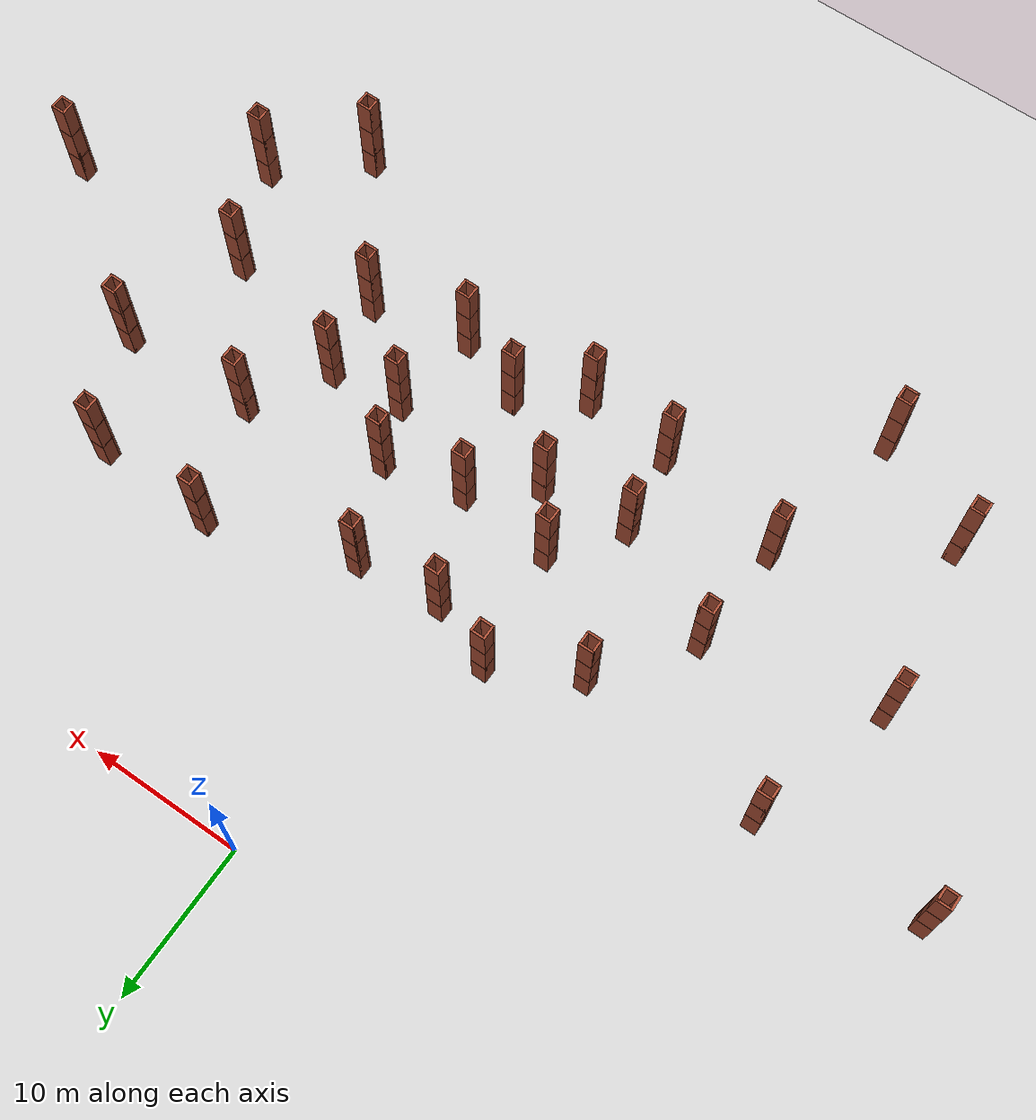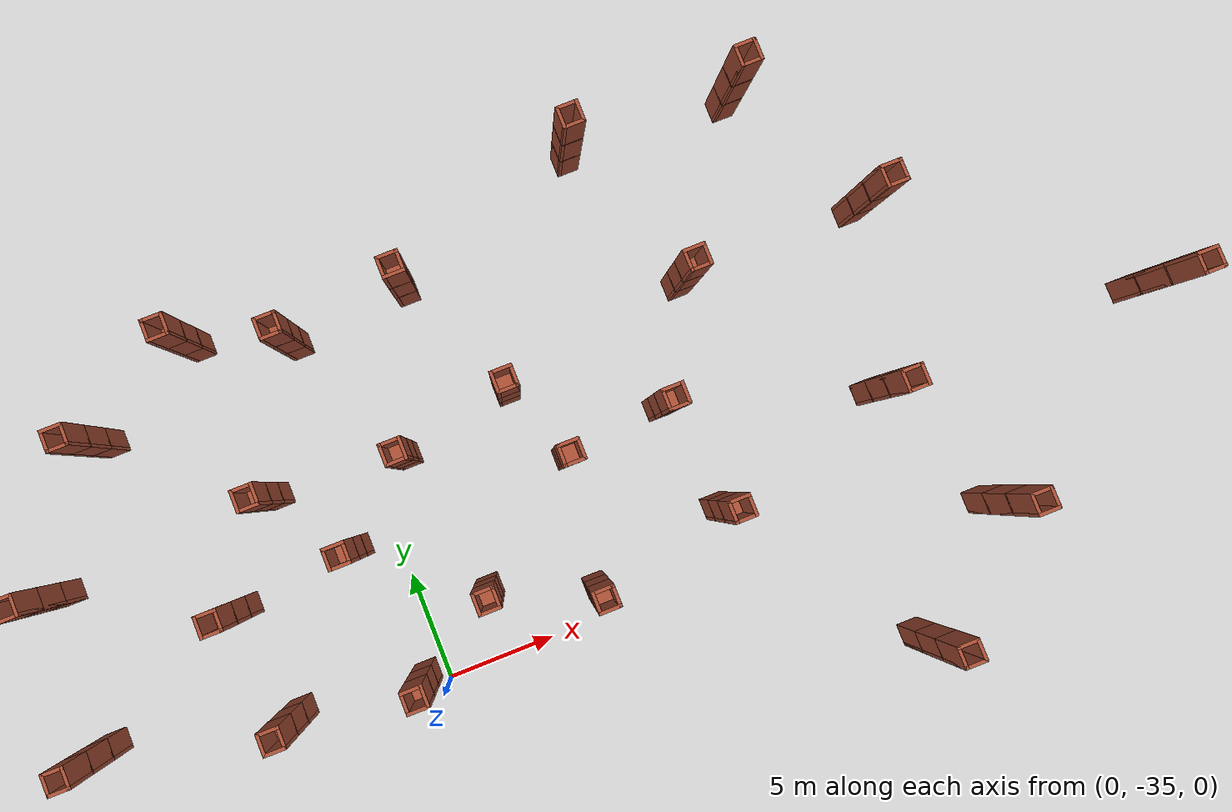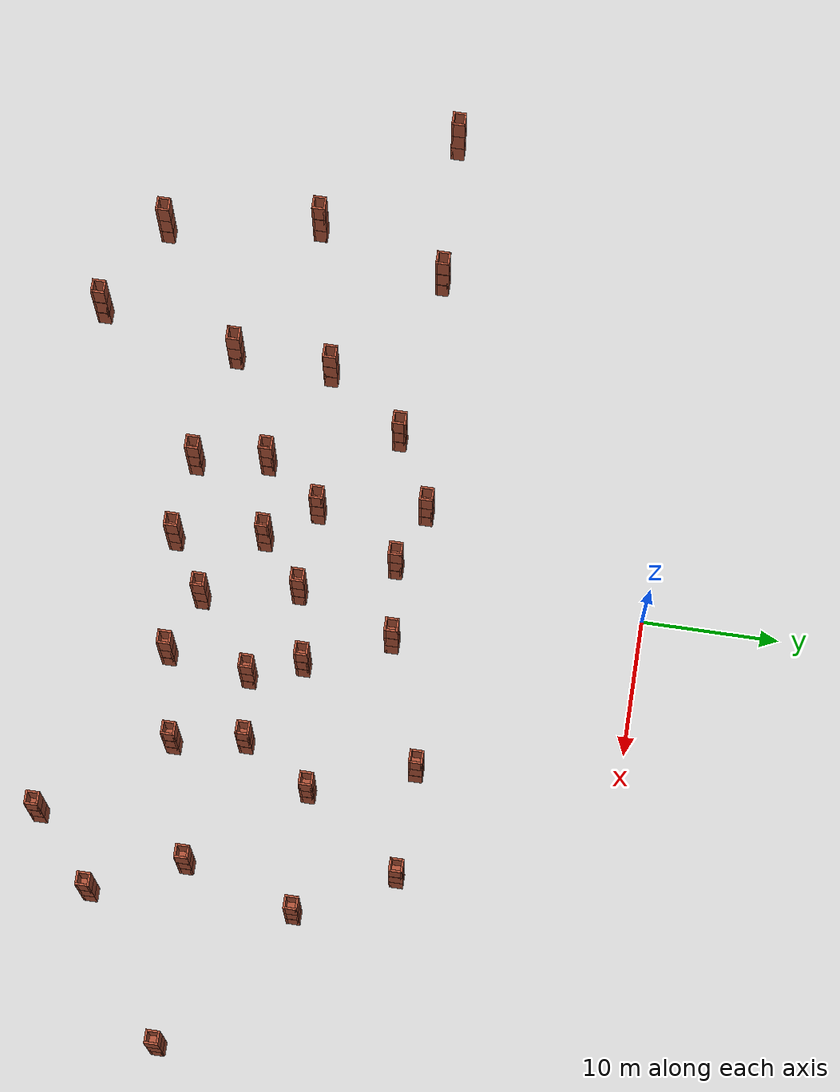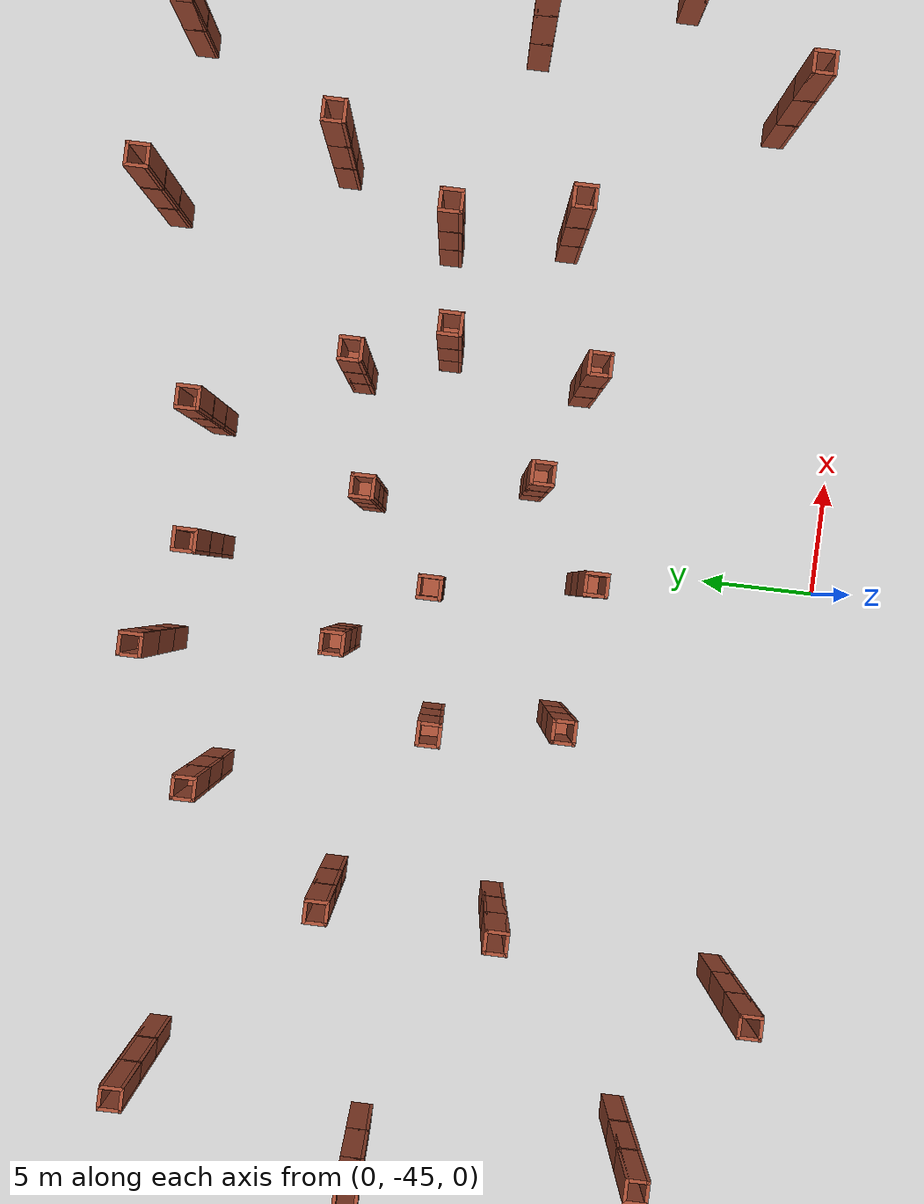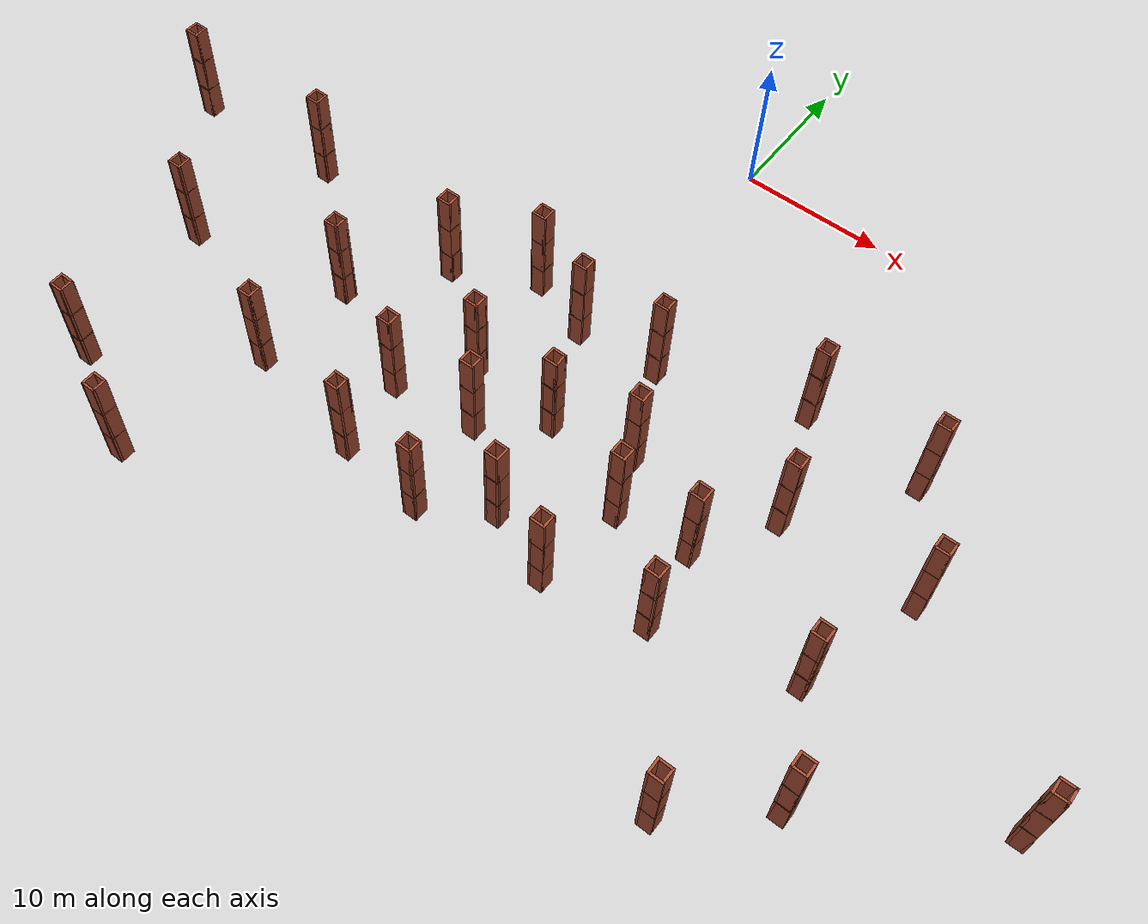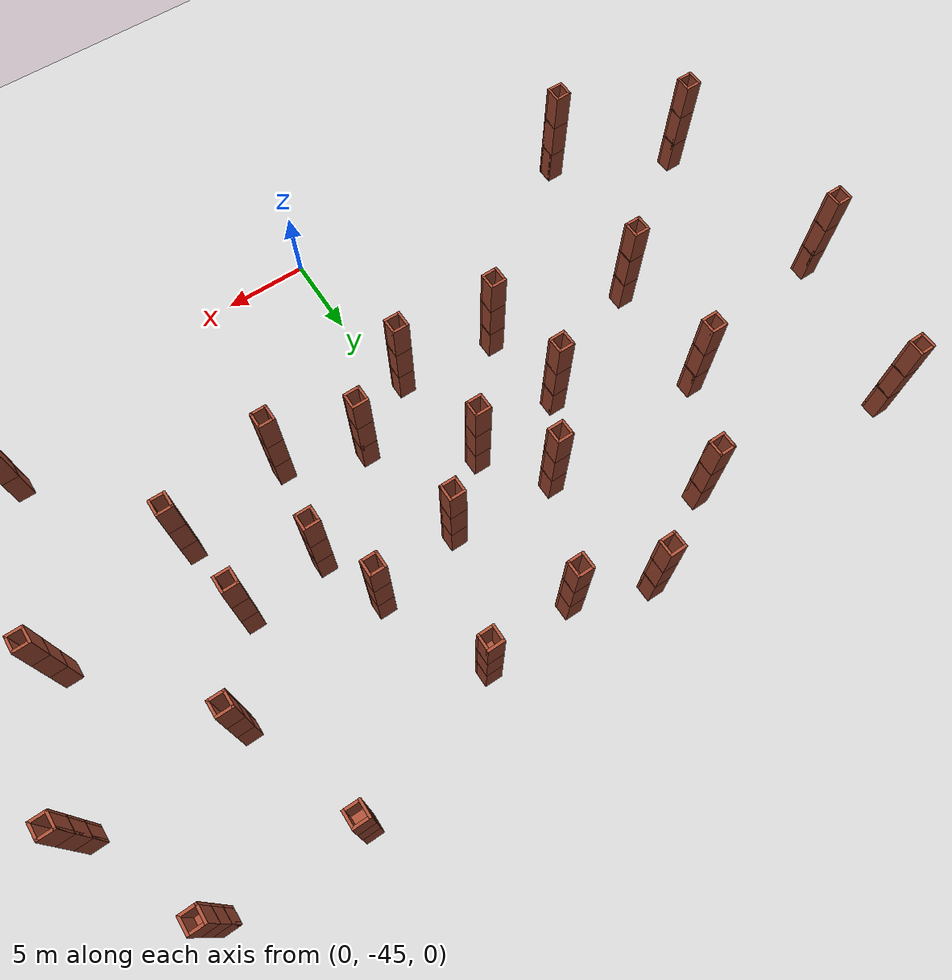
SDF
<sdf version="1.7">
 <world name="default">
  <light name="sun" type="directional">
   <pose>0 0 10 0 -0 0</pose>
   <diffuse>0.8 0.8 0.8 1</diffuse>
   <specular>0.2 0.2 0.2 1</specular>
   <attenuation>
    <range>1000</range>
    <constant>0.9</constant>
    <linear>0.01</linear>
    <quadratic>0.001</quadratic>
   </attenuation>
   <direction>-0.5 0.1 -0.9</direction>
   <spot><inner_angle>0</inner_angle><outer_angle>0</outer_angle><falloff>0</falloff></spot>
  </light>
  <model name="ground_plane">
   <static>1</static>
   <link name="link">
    <collision name="collision">
     <geometry><plane><normal>0 0 1</normal><size>100 100</size></plane></geometry>
     <surface>
      <contact><collide_bitmask>65535</collide_bitmask></contact>
      <friction><ode><mu>100</mu><mu2>50</mu2></ode></friction>
     </surface>
    </collision>
    <visual name="visual">
     <cast_shadows>0</cast_shadows>
     <geometry><plane><normal>0 0 1</normal><size>100 100</size></plane></geometry>
     <material>
      <script><uri>file://media/materials/scripts/gazebo.material</uri><name>Gazebo/Grey</name></script>
     </material>
    </visual>
   </link>
  </model>
  <gravity>0 0 -9.8</gravity>
  <magnetic_field>6e-06 2.3e-05 -4.2e-05</magnetic_field>
  <atmosphere type="adiabatic"/>
  <physics type="ode">
   <max_step_size>0.001</max_step_size>
   <real_time_factor>1</real_time_factor>
   <real_time_update_rate>1000</real_time_update_rate>
  </physics>
  <scene><ambient>0.4 0.4 0.4 1</ambient><background>0.7 0.7 0.7 1</background><shadows>1</shadows></scene>
  <spherical_coordinates>
   <surface_model>EARTH_WGS84</surface_model>
   <latitude_deg>0</latitude_deg>
   <longitude_deg>0</longitude_deg>
   <elevation>0</elevation>
   <heading_deg>0</heading_deg>
  </spherical_coordinates>
  <model name="wall_model">
   <pose>2.36108 -35 0 0 -0 0</pose>
   <link name="Floor_3">
    <collision name="Floor_3_Collision">
     <geometry><box><size>1 1 0.1</size></box></geometry>
     <pose>0 0 0.05 0 -0 0</pose>
    </collision>
    <visual name="Floor_3_Visual">
     <pose>0 0 0.05 0 -0 0</pose>
     <geometry><box><size>1 1 0.1</size></box></geometry>
     <material>
      <script><uri>file://media/materials/scripts/gazebo.material</uri><name>Gazebo/Bricks</name></script>
      <ambient>1 1 1 1</ambient>
     </material>
     <meta><layer>1</layer></meta>
    </visual>
    <pose>-3.21504 0.623396 2.5 0 -0 0</pose>
   </link>
   <link name="Floor_4">
    <collision name="Floor_4_Collision">
     <geometry><box><size>1 1 0.1</size></box></geometry>
     <pose>0 0 0.05 0 -0 0</pose>
    </collision>
    <visual name="Floor_4_Visual">
     <pose>0 0 0.05 0 -0 0</pose>
     <geometry><box><size>1 1 0.1</size></box></geometry>
     <material>
      <script><uri>file://media/materials/scripts/gazebo.material</uri><name>Gazebo/Bricks</name></script>
      <ambient>1 1 1 1</ambient>
     </material>
     <meta><layer>2</layer></meta>
    </visual>
    <pose>-3.21504 0.623396 5 0 -0 0</pose>
   </link>
   <link name="Wall_19">
    <collision name="Wall_19_Collision">
     <geometry><box><size>1 0.15 2.5</size></box></geometry>
     <pose>0 0 1.25 0 -0 0</pose>
    </collision>
    <visual name="Wall_19_Visual">
     <pose>0 0 1.25 0 -0 0</pose>
     <geometry><box><size>1 0.15 2.5</size></box></geometry>
     <material>
      <script><uri>file://media/materials/scripts/gazebo.material</uri><name>Gazebo/Bricks</name></script>
      <ambient>1 1 1 1</ambient>
     </material>
     <meta><layer>0</layer></meta>
    </visual>
    <pose>-3.64004 0.623396 0 0 -0 1.5708</pose>
   </link>
   <link name="Wall_21">
    <collision name="Wall_21_Collision">
     <geometry><box><size>1 0.15 2.5</size></box></geometry>
     <pose>0 0 1.25 0 -0 0</pose>
    </collision>
    <visual name="Wall_21_Visual">
     <pose>0 0 1.25 0 -0 0</pose>
     <geometry><box><size>1 0.15 2.5</size></box></geometry>
     <material>
      <script><uri>file://media/materials/scripts/gazebo.material</uri><name>Gazebo/Bricks</name></script>
      <ambient>1 1 1 1</ambient>
     </material>
     <meta><layer>0</layer></meta>
    </visual>
    <pose>-3.21504 1.0484 0 0 -0 0</pose>
   </link>
   <link name="Wall_22">
    <collision name="Wall_22_Collision">
     <geometry><box><size>1 0.15 2.5</size></box></geometry>
     <pose>0 0 1.25 0 -0 0</pose>
    </collision>
    <visual name="Wall_22_Visual">
     <pose>0 0 1.25 0 -0 0</pose>
     <geometry><box><size>1 0.15 2.5</size></box></geometry>
     <material>
      <script><uri>file://media/materials/scripts/gazebo.material</uri><name>Gazebo/Bricks</name></script>
      <ambient>1 1 1 1</ambient>
     </material>
     <meta><layer>0</layer></meta>
    </visual>
    <pose>-2.79004 0.623396 0 0 -0 -1.5708</pose>
   </link>
   <link name="Wall_23">
    <collision name="Wall_23_Collision">
     <geometry><box><size>1 0.15 2.5</size></box></geometry>
     <pose>0 0 1.25 0 -0 0</pose>
    </collision>
    <visual name="Wall_23_Visual">
     <pose>0 0 1.25 0 -0 0</pose>
     <geometry><box><size>1 0.15 2.5</size></box></geometry>
     <material>
      <script><uri>file://media/materials/scripts/gazebo.material</uri><name>Gazebo/Bricks</name></script>
      <ambient>1 1 1 1</ambient>
     </material>
     <meta><layer>0</layer></meta>
    </visual>
    <pose>-3.21504 0.198396 0 0 -0 3.14159</pose>
   </link>
   <link name="Wall_25">
    <collision name="Wall_25_Collision">
     <geometry><box><size>1 0.15 2.5</size></box></geometry>
     <pose>0 0 1.25 0 -0 0</pose>
    </collision>
    <visual name="Wall_25_Visual">
     <pose>0 0 1.25 0 -0 0</pose>
     <geometry><box><size>1 0.15 2.5</size></box></geometry>
     <material>
      <script><uri>file://media/materials/scripts/gazebo.material</uri><name>Gazebo/Bricks</name></script>
      <ambient>1 1 1 1</ambient>
     </material>
     <meta><layer>1</layer></meta>
    </visual>
    <pose>-3.64004 0.623396 2.5 0 -0 1.5708</pose>
   </link>
   <link name="Wall_26">
    <collision name="Wall_26_Collision">
     <geometry><box><size>1 0.15 2.5</size></box></geometry>
     <pose>0 0 1.25 0 -0 0</pose>
    </collision>
    <visual name="Wall_26_Visual">
     <pose>0 0 1.25 0 -0 0</pose>
     <geometry><box><size>1 0.15 2.5</size></box></geometry>
     <material>
      <script><uri>file://media/materials/scripts/gazebo.material</uri><name>Gazebo/Bricks</name></script>
      <ambient>1 1 1 1</ambient>
     </material>
     <meta><layer>1</layer></meta>
    </visual>
    <pose>-3.21504 1.0484 2.5 0 -0 0</pose>
   </link>
   <link name="Wall_27">
    <collision name="Wall_27_Collision">
     <geometry><box><size>1 0.15 2.5</size></box></geometry>
     <pose>0 0 1.25 0 -0 0</pose>
    </collision>
    <visual name="Wall_27_Visual">
     <pose>0 0 1.25 0 -0 0</pose>
     <geometry><box><size>1 0.15 2.5</size></box></geometry>
     <material>
      <script><uri>file://media/materials/scripts/gazebo.material</uri><name>Gazebo/Bricks</name></script>
      <ambient>1 1 1 1</ambient>
     </material>
     <meta><layer>1</layer></meta>
    </visual>
    <pose>-2.79004 0.623396 2.5 0 -0 -1.5708</pose>
   </link>
   <link name="Wall_28">
    <collision name="Wall_28_Collision">
     <geometry><box><size>1 0.15 2.5</size></box></geometry>
     <pose>0 0 1.25 0 -0 0</pose>
    </collision>
    <visual name="Wall_28_Visual">
     <pose>0 0 1.25 0 -0 0</pose>
     <geometry><box><size>1 0.15 2.5</size></box></geometry>
     <material>
      <script><uri>file://media/materials/scripts/gazebo.material</uri><name>Gazebo/Bricks</name></script>
      <ambient>1 1 1 1</ambient>
     </material>
     <meta><layer>1</layer></meta>
    </visual>
    <pose>-3.21504 0.198396 2.5 0 -0 3.14159</pose>
   </link>
   <link name="Wall_29">
    <collision name="Wall_29_Collision">
     <geometry><box><size>1 0.15 2.5</size></box></geometry>
     <pose>0 0 1.25 0 -0 0</pose>
    </collision>
    <visual name="Wall_29_Visual">
     <pose>0 0 1.25 0 -0 0</pose>
     <geometry><box><size>1 0.15 2.5</size></box></geometry>
     <material>
      <script><uri>file://media/materials/scripts/gazebo.material</uri><name>Gazebo/Bricks</name></script>
      <ambient>1 1 1 1</ambient>
     </material>
     <meta><layer>2</layer></meta>
    </visual>
    <pose>-3.64004 0.623396 5 0 -0 1.5708</pose>
   </link>
   <link name="Wall_30">
    <collision name="Wall_30_Collision">
     <geometry><box><size>1 0.15 2.5</size></box></geometry>
     <pose>0 0 1.25 0 -0 0</pose>
    </collision>
    <visual name="Wall_30_Visual">
     <pose>0 0 1.25 0 -0 0</pose>
     <geometry><box><size>1 0.15 2.5</size></box></geometry>
     <material>
      <script><uri>file://media/materials/scripts/gazebo.material</uri><name>Gazebo/Bricks</name></script>
      <ambient>1 1 1 1</ambient>
     </material>
     <meta><layer>2</layer></meta>
    </visual>
    <pose>-3.21504 1.0484 5 0 -0 0</pose>
   </link>
   <link name="Wall_31">
    <collision name="Wall_31_Collision">
     <geometry><box><size>1 0.15 2.5</size></box></geometry>
     <pose>0 0 1.25 0 -0 0</pose>
    </collision>
    <visual name="Wall_31_Visual">
     <pose>0 0 1.25 0 -0 0</pose>
     <geometry><box><size>1 0.15 2.5</size></box></geometry>
     <material>
      <script><uri>file://media/materials/scripts/gazebo.material</uri><name>Gazebo/Bricks</name></script>
      <ambient>1 1 1 1</ambient>
     </material>
     <meta><layer>2</layer></meta>
    </visual>
    <pose>-2.79004 0.623396 5 0 -0 -1.5708</pose>
   </link>
   <link name="Wall_32">
    <collision name="Wall_32_Collision">
     <geometry><box><size>1 0.15 2.5</size></box></geometry>
     <pose>0 0 1.25 0 -0 0</pose>
    </collision>
    <visual name="Wall_32_Visual">
     <pose>0 0 1.25 0 -0 0</pose>
     <geometry><box><size>1 0.15 2.5</size></box></geometry>
     <material>
      <script><uri>file://media/materials/scripts/gazebo.material</uri><name>Gazebo/Bricks</name></script>
      <ambient>1 1 1 1</ambient>
     </material>
     <meta><layer>2</layer></meta>
    </visual>
    <pose>-3.21504 0.198396 5 0 -0 3.14159</pose>
   </link>
   <static>1</static>
  </model>
  <model name="wall_model_clone">
   <pose>6.41502 -32.412 0 0 -0 0</pose>
   <link name="Floor_3">
    <collision name="Floor_3_Collision">
     <geometry><box><size>1 1 0.1</size></box></geometry>
     <pose>0 0 0.05 0 -0 0</pose>
    </collision>
    <visual name="Floor_3_Visual">
     <pose>0 0 0.05 0 -0 0</pose>
     <geometry><box><size>1 1 0.1</size></box></geometry>
     <material>
      <script><uri>file://media/materials/scripts/gazebo.material</uri><name>Gazebo/Bricks</name></script>
      <ambient>1 1 1 1</ambient>
     </material>
     <meta><layer>1</layer></meta>
    </visual>
    <pose>-3.21504 0.623396 2.5 0 -0 0</pose>
   </link>
   <link name="Floor_4">
    <collision name="Floor_4_Collision">
     <geometry><box><size>1 1 0.1</size></box></geometry>
     <pose>0 0 0.05 0 -0 0</pose>
    </collision>
    <visual name="Floor_4_Visual">
     <pose>0 0 0.05 0 -0 0</pose>
     <geometry><box><size>1 1 0.1</size></box></geometry>
     <material>
      <script><uri>file://media/materials/scripts/gazebo.material</uri><name>Gazebo/Bricks</name></script>
      <ambient>1 1 1 1</ambient>
     </material>
     <meta><layer>2</layer></meta>
    </visual>
    <pose>-3.21504 0.623396 5 0 -0 0</pose>
   </link>
   <link name="Wall_19">
    <collision name="Wall_19_Collision">
     <geometry><box><size>1 0.15 2.5</size></box></geometry>
     <pose>0 0 1.25 0 -0 0</pose>
    </collision>
    <visual name="Wall_19_Visual">
     <pose>0 0 1.25 0 -0 0</pose>
     <geometry><box><size>1 0.15 2.5</size></box></geometry>
     <material>
      <script><uri>file://media/materials/scripts/gazebo.material</uri><name>Gazebo/Bricks</name></script>
      <ambient>1 1 1 1</ambient>
     </material>
     <meta><layer>0</layer></meta>
    </visual>
    <pose>-3.64004 0.623396 0 0 -0 1.5708</pose>
   </link>
   <link name="Wall_21">
    <collision name="Wall_21_Collision">
     <geometry><box><size>1 0.15 2.5</size></box></geometry>
     <pose>0 0 1.25 0 -0 0</pose>
    </collision>
    <visual name="Wall_21_Visual">
     <pose>0 0 1.25 0 -0 0</pose>
     <geometry><box><size>1 0.15 2.5</size></box></geometry>
     <material>
      <script><uri>file://media/materials/scripts/gazebo.material</uri><name>Gazebo/Bricks</name></script>
      <ambient>1 1 1 1</ambient>
     </material>
     <meta><layer>0</layer></meta>
    </visual>
    <pose>-3.21504 1.0484 0 0 -0 0</pose>
   </link>
   <link name="Wall_22">
    <collision name="Wall_22_Collision">
     <geometry><box><size>1 0.15 2.5</size></box></geometry>
     <pose>0 0 1.25 0 -0 0</pose>
    </collision>
    <visual name="Wall_22_Visual">
     <pose>0 0 1.25 0 -0 0</pose>
     <geometry><box><size>1 0.15 2.5</size></box></geometry>
     <material>
      <script><uri>file://media/materials/scripts/gazebo.material</uri><name>Gazebo/Bricks</name></script>
      <ambient>1 1 1 1</ambient>
     </material>
     <meta><layer>0</layer></meta>
    </visual>
    <pose>-2.79004 0.623396 0 0 -0 -1.5708</pose>
   </link>
   <link name="Wall_23">
    <collision name="Wall_23_Collision">
     <geometry><box><size>1 0.15 2.5</size></box></geometry>
     <pose>0 0 1.25 0 -0 0</pose>
    </collision>
    <visual name="Wall_23_Visual">
     <pose>0 0 1.25 0 -0 0</pose>
     <geometry><box><size>1 0.15 2.5</size></box></geometry>
     <material>
      <script><uri>file://media/materials/scripts/gazebo.material</uri><name>Gazebo/Bricks</name></script>
      <ambient>1 1 1 1</ambient>
     </material>
     <meta><layer>0</layer></meta>
    </visual>
    <pose>-3.21504 0.198396 0 0 -0 3.14159</pose>
   </link>
   <link name="Wall_25">
    <collision name="Wall_25_Collision">
     <geometry><box><size>1 0.15 2.5</size></box></geometry>
     <pose>0 0 1.25 0 -0 0</pose>
    </collision>
    <visual name="Wall_25_Visual">
     <pose>0 0 1.25 0 -0 0</pose>
     <geometry><box><size>1 0.15 2.5</size></box></geometry>
     <material>
      <script><uri>file://media/materials/scripts/gazebo.material</uri><name>Gazebo/Bricks</name></script>
      <ambient>1 1 1 1</ambient>
     </material>
     <meta><layer>1</layer></meta>
    </visual>
    <pose>-3.64004 0.623396 2.5 0 -0 1.5708</pose>
   </link>
   <link name="Wall_26">
    <collision name="Wall_26_Collision">
     <geometry><box><size>1 0.15 2.5</size></box></geometry>
     <pose>0 0 1.25 0 -0 0</pose>
    </collision>
    <visual name="Wall_26_Visual">
     <pose>0 0 1.25 0 -0 0</pose>
     <geometry><box><size>1 0.15 2.5</size></box></geometry>
     <material>
      <script><uri>file://media/materials/scripts/gazebo.material</uri><name>Gazebo/Bricks</name></script>
      <ambient>1 1 1 1</ambient>
     </material>
     <meta><layer>1</layer></meta>
    </visual>
    <pose>-3.21504 1.0484 2.5 0 -0 0</pose>
   </link>
   <link name="Wall_27">
    <collision name="Wall_27_Collision">
     <geometry><box><size>1 0.15 2.5</size></box></geometry>
     <pose>0 0 1.25 0 -0 0</pose>
    </collision>
    <visual name="Wall_27_Visual">
     <pose>0 0 1.25 0 -0 0</pose>
     <geometry><box><size>1 0.15 2.5</size></box></geometry>
     <material>
      <script><uri>file://media/materials/scripts/gazebo.material</uri><name>Gazebo/Bricks</name></script>
      <ambient>1 1 1 1</ambient>
     </material>
     <meta><layer>1</layer></meta>
    </visual>
    <pose>-2.79004 0.623396 2.5 0 -0 -1.5708</pose>
   </link>
   <link name="Wall_28">
    <collision name="Wall_28_Collision">
     <geometry><box><size>1 0.15 2.5</size></box></geometry>
     <pose>0 0 1.25 0 -0 0</pose>
    </collision>
    <visual name="Wall_28_Visual">
     <pose>0 0 1.25 0 -0 0</pose>
     <geometry><box><size>1 0.15 2.5</size></box></geometry>
     <material>
      <script><uri>file://media/materials/scripts/gazebo.material</uri><name>Gazebo/Bricks</name></script>
      <ambient>1 1 1 1</ambient>
     </material>
     <meta><layer>1</layer></meta>
    </visual>
    <pose>-3.21504 0.198396 2.5 0 -0 3.14159</pose>
   </link>
   <link name="Wall_29">
    <collision name="Wall_29_Collision">
     <geometry><box><size>1 0.15 2.5</size></box></geometry>
     <pose>0 0 1.25 0 -0 0</pose>
    </collision>
    <visual name="Wall_29_Visual">
     <pose>0 0 1.25 0 -0 0</pose>
     <geometry><box><size>1 0.15 2.5</size></box></geometry>
     <material>
      <script><uri>file://media/materials/scripts/gazebo.material</uri><name>Gazebo/Bricks</name></script>
      <ambient>1 1 1 1</ambient>
     </material>
     <meta><layer>2</layer></meta>
    </visual>
    <pose>-3.64004 0.623396 5 0 -0 1.5708</pose>
   </link>
   <link name="Wall_30">
    <collision name="Wall_30_Collision">
     <geometry><box><size>1 0.15 2.5</size></box></geometry>
     <pose>0 0 1.25 0 -0 0</pose>
    </collision>
    <visual name="Wall_30_Visual">
     <pose>0 0 1.25 0 -0 0</pose>
     <geometry><box><size>1 0.15 2.5</size></box></geometry>
     <material>
      <script><uri>file://media/materials/scripts/gazebo.material</uri><name>Gazebo/Bricks</name></script>
      <ambient>1 1 1 1</ambient>
     </material>
     <meta><layer>2</layer></meta>
    </visual>
    <pose>-3.21504 1.0484 5 0 -0 0</pose>
   </link>
   <link name="Wall_31">
    <collision name="Wall_31_Collision">
     <geometry><box><size>1 0.15 2.5</size></box></geometry>
     <pose>0 0 1.25 0 -0 0</pose>
    </collision>
    <visual name="Wall_31_Visual">
     <pose>0 0 1.25 0 -0 0</pose>
     <geometry><box><size>1 0.15 2.5</size></box></geometry>
     <material>
      <script><uri>file://media/materials/scripts/gazebo.material</uri><name>Gazebo/Bricks</name></script>
      <ambient>1 1 1 1</ambient>
     </material>
     <meta><layer>2</layer></meta>
    </visual>
    <pose>-2.79004 0.623396 5 0 -0 -1.5708</pose>
   </link>
   <link name="Wall_32">
    <collision name="Wall_32_Collision">
     <geometry><box><size>1 0.15 2.5</size></box></geometry>
     <pose>0 0 1.25 0 -0 0</pose>
    </collision>
    <visual name="Wall_32_Visual">
     <pose>0 0 1.25 0 -0 0</pose>
     <geometry><box><size>1 0.15 2.5</size></box></geometry>
     <material>
      <script><uri>file://media/materials/scripts/gazebo.material</uri><name>Gazebo/Bricks</name></script>
      <ambient>1 1 1 1</ambient>
     </material>
     <meta><layer>2</layer></meta>
    </visual>
    <pose>-3.21504 0.198396 5 0 -0 3.14159</pose>
   </link>
   <static>1</static>
  </model>
  <model name="wall_model_clone_0">
   <pose>10.9073 -34.1128 0 0 -0 0</pose>
   <link name="Floor_3">
    <collision name="Floor_3_Collision">
     <geometry><box><size>1 1 0.1</size></box></geometry>
     <pose>0 0 0.05 0 -0 0</pose>
    </collision>
    <visual name="Floor_3_Visual">
     <pose>0 0 0.05 0 -0 0</pose>
     <geometry><box><size>1 1 0.1</size></box></geometry>
     <material>
      <script><uri>file://media/materials/scripts/gazebo.material</uri><name>Gazebo/Bricks</name></script>
      <ambient>1 1 1 1</ambient>
     </material>
     <meta><layer>1</layer></meta>
    </visual>
    <pose>-3.21504 0.623396 2.5 0 -0 0</pose>
   </link>
   <link name="Floor_4">
    <collision name="Floor_4_Collision">
     <geometry><box><size>1 1 0.1</size></box></geometry>
     <pose>0 0 0.05 0 -0 0</pose>
    </collision>
    <visual name="Floor_4_Visual">
     <pose>0 0 0.05 0 -0 0</pose>
     <geometry><box><size>1 1 0.1</size></box></geometry>
     <material>
      <script><uri>file://media/materials/scripts/gazebo.material</uri><name>Gazebo/Bricks</name></script>
      <ambient>1 1 1 1</ambient>
     </material>
     <meta><layer>2</layer></meta>
    </visual>
    <pose>-3.21504 0.623396 5 0 -0 0</pose>
   </link>
   <link name="Wall_19">
    <collision name="Wall_19_Collision">
     <geometry><box><size>1 0.15 2.5</size></box></geometry>
     <pose>0 0 1.25 0 -0 0</pose>
    </collision>
    <visual name="Wall_19_Visual">
     <pose>0 0 1.25 0 -0 0</pose>
     <geometry><box><size>1 0.15 2.5</size></box></geometry>
     <material>
      <script><uri>file://media/materials/scripts/gazebo.material</uri><name>Gazebo/Bricks</name></script>
      <ambient>1 1 1 1</ambient>
     </material>
     <meta><layer>0</layer></meta>
    </visual>
    <pose>-3.64004 0.623396 0 0 -0 1.5708</pose>
   </link>
   <link name="Wall_21">
    <collision name="Wall_21_Collision">
     <geometry><box><size>1 0.15 2.5</size></box></geometry>
     <pose>0 0 1.25 0 -0 0</pose>
    </collision>
    <visual name="Wall_21_Visual">
     <pose>0 0 1.25 0 -0 0</pose>
     <geometry><box><size>1 0.15 2.5</size></box></geometry>
     <material>
      <script><uri>file://media/materials/scripts/gazebo.material</uri><name>Gazebo/Bricks</name></script>
      <ambient>1 1 1 1</ambient>
     </material>
     <meta><layer>0</layer></meta>
    </visual>
    <pose>-3.21504 1.0484 0 0 -0 0</pose>
   </link>
   <link name="Wall_22">
    <collision name="Wall_22_Collision">
     <geometry><box><size>1 0.15 2.5</size></box></geometry>
     <pose>0 0 1.25 0 -0 0</pose>
    </collision>
    <visual name="Wall_22_Visual">
     <pose>0 0 1.25 0 -0 0</pose>
     <geometry><box><size>1 0.15 2.5</size></box></geometry>
     <material>
      <script><uri>file://media/materials/scripts/gazebo.material</uri><name>Gazebo/Bricks</name></script>
      <ambient>1 1 1 1</ambient>
     </material>
     <meta><layer>0</layer></meta>
    </visual>
    <pose>-2.79004 0.623396 0 0 -0 -1.5708</pose>
   </link>
   <link name="Wall_23">
    <collision name="Wall_23_Collision">
     <geometry><box><size>1 0.15 2.5</size></box></geometry>
     <pose>0 0 1.25 0 -0 0</pose>
    </collision>
    <visual name="Wall_23_Visual">
     <pose>0 0 1.25 0 -0 0</pose>
     <geometry><box><size>1 0.15 2.5</size></box></geometry>
     <material>
      <script><uri>file://media/materials/scripts/gazebo.material</uri><name>Gazebo/Bricks</name></script>
      <ambient>1 1 1 1</ambient>
     </material>
     <meta><layer>0</layer></meta>
    </visual>
    <pose>-3.21504 0.198396 0 0 -0 3.14159</pose>
   </link>
   <link name="Wall_25">
    <collision name="Wall_25_Collision">
     <geometry><box><size>1 0.15 2.5</size></box></geometry>
     <pose>0 0 1.25 0 -0 0</pose>
    </collision>
    <visual name="Wall_25_Visual">
     <pose>0 0 1.25 0 -0 0</pose>
     <geometry><box><size>1 0.15 2.5</size></box></geometry>
     <material>
      <script><uri>file://media/materials/scripts/gazebo.material</uri><name>Gazebo/Bricks</name></script>
      <ambient>1 1 1 1</ambient>
     </material>
     <meta><layer>1</layer></meta>
    </visual>
    <pose>-3.64004 0.623396 2.5 0 -0 1.5708</pose>
   </link>
   <link name="Wall_26">
    <collision name="Wall_26_Collision">
     <geometry><box><size>1 0.15 2.5</size></box></geometry>
     <pose>0 0 1.25 0 -0 0</pose>
    </collision>
    <visual name="Wall_26_Visual">
     <pose>0 0 1.25 0 -0 0</pose>
     <geometry><box><size>1 0.15 2.5</size></box></geometry>
     <material>
      <script><uri>file://media/materials/scripts/gazebo.material</uri><name>Gazebo/Bricks</name></script>
      <ambient>1 1 1 1</ambient>
     </material>
     <meta><layer>1</layer></meta>
    </visual>
    <pose>-3.21504 1.0484 2.5 0 -0 0</pose>
   </link>
   <link name="Wall_27">
    <collision name="Wall_27_Collision">
     <geometry><box><size>1 0.15 2.5</size></box></geometry>
     <pose>0 0 1.25 0 -0 0</pose>
    </collision>
    <visual name="Wall_27_Visual">
     <pose>0 0 1.25 0 -0 0</pose>
     <geometry><box><size>1 0.15 2.5</size></box></geometry>
     <material>
      <script><uri>file://media/materials/scripts/gazebo.material</uri><name>Gazebo/Bricks</name></script>
      <ambient>1 1 1 1</ambient>
     </material>
     <meta><layer>1</layer></meta>
    </visual>
    <pose>-2.79004 0.623396 2.5 0 -0 -1.5708</pose>
   </link>
   <link name="Wall_28">
    <collision name="Wall_28_Collision">
     <geometry><box><size>1 0.15 2.5</size></box></geometry>
     <pose>0 0 1.25 0 -0 0</pose>
    </collision>
    <visual name="Wall_28_Visual">
     <pose>0 0 1.25 0 -0 0</pose>
     <geometry><box><size>1 0.15 2.5</size></box></geometry>
     <material>
      <script><uri>file://media/materials/scripts/gazebo.material</uri><name>Gazebo/Bricks</name></script>
      <ambient>1 1 1 1</ambient>
     </material>
     <meta><layer>1</layer></meta>
    </visual>
    <pose>-3.21504 0.198396 2.5 0 -0 3.14159</pose>
   </link>
   <link name="Wall_29">
    <collision name="Wall_29_Collision">
     <geometry><box><size>1 0.15 2.5</size></box></geometry>
     <pose>0 0 1.25 0 -0 0</pose>
    </collision>
    <visual name="Wall_29_Visual">
     <pose>0 0 1.25 0 -0 0</pose>
     <geometry><box><size>1 0.15 2.5</size></box></geometry>
     <material>
      <script><uri>file://media/materials/scripts/gazebo.material</uri><name>Gazebo/Bricks</name></script>
      <ambient>1 1 1 1</ambient>
     </material>
     <meta><layer>2</layer></meta>
    </visual>
    <pose>-3.64004 0.623396 5 0 -0 1.5708</pose>
   </link>
   <link name="Wall_30">
    <collision name="Wall_30_Collision">
     <geometry><box><size>1 0.15 2.5</size></box></geometry>
     <pose>0 0 1.25 0 -0 0</pose>
    </collision>
    <visual name="Wall_30_Visual">
     <pose>0 0 1.25 0 -0 0</pose>
     <geometry><box><size>1 0.15 2.5</size></box></geometry>
     <material>
      <script><uri>file://media/materials/scripts/gazebo.material</uri><name>Gazebo/Bricks</name></script>
      <ambient>1 1 1 1</ambient>
     </material>
     <meta><layer>2</layer></meta>
    </visual>
    <pose>-3.21504 1.0484 5 0 -0 0</pose>
   </link>
   <link name="Wall_31">
    <collision name="Wall_31_Collision">
     <geometry><box><size>1 0.15 2.5</size></box></geometry>
     <pose>0 0 1.25 0 -0 0</pose>
    </collision>
    <visual name="Wall_31_Visual">
     <pose>0 0 1.25 0 -0 0</pose>
     <geometry><box><size>1 0.15 2.5</size></box></geometry>
     <material>
      <script><uri>file://media/materials/scripts/gazebo.material</uri><name>Gazebo/Bricks</name></script>
      <ambient>1 1 1 1</ambient>
     </material>
     <meta><layer>2</layer></meta>
    </visual>
    <pose>-2.79004 0.623396 5 0 -0 -1.5708</pose>
   </link>
   <link name="Wall_32">
    <collision name="Wall_32_Collision">
     <geometry><box><size>1 0.15 2.5</size></box></geometry>
     <pose>0 0 1.25 0 -0 0</pose>
    </collision>
    <visual name="Wall_32_Visual">
     <pose>0 0 1.25 0 -0 0</pose>
     <geometry><box><size>1 0.15 2.5</size></box></geometry>
     <material>
      <script><uri>file://media/materials/scripts/gazebo.material</uri><name>Gazebo/Bricks</name></script>
      <ambient>1 1 1 1</ambient>
     </material>
     <meta><layer>2</layer></meta>
    </visual>
    <pose>-3.21504 0.198396 5 0 -0 3.14159</pose>
   </link>
   <static>1</static>
  </model>
  <model name="wall_model_clone_1">
   <pose>11.7691 -28.1348 0 0 -0 0</pose>
   <link name="Floor_3">
    <collision name="Floor_3_Collision">
     <geometry><box><size>1 1 0.1</size></box></geometry>
     <pose>0 0 0.05 0 -0 0</pose>
    </collision>
    <visual name="Floor_3_Visual">
     <pose>0 0 0.05 0 -0 0</pose>
     <geometry><box><size>1 1 0.1</size></box></geometry>
     <material>
      <script><uri>file://media/materials/scripts/gazebo.material</uri><name>Gazebo/Bricks</name></script>
      <ambient>1 1 1 1</ambient>
     </material>
     <meta><layer>1</layer></meta>
    </visual>
    <pose>-3.21504 0.623396 2.5 0 -0 0</pose>
   </link>
   <link name="Floor_4">
    <collision name="Floor_4_Collision">
     <geometry><box><size>1 1 0.1</size></box></geometry>
     <pose>0 0 0.05 0 -0 0</pose>
    </collision>
    <visual name="Floor_4_Visual">
     <pose>0 0 0.05 0 -0 0</pose>
     <geometry><box><size>1 1 0.1</size></box></geometry>
     <material>
      <script><uri>file://media/materials/scripts/gazebo.material</uri><name>Gazebo/Bricks</name></script>
      <ambient>1 1 1 1</ambient>
     </material>
     <meta><layer>2</layer></meta>
    </visual>
    <pose>-3.21504 0.623396 5 0 -0 0</pose>
   </link>
   <link name="Wall_19">
    <collision name="Wall_19_Collision">
     <geometry><box><size>1 0.15 2.5</size></box></geometry>
     <pose>0 0 1.25 0 -0 0</pose>
    </collision>
    <visual name="Wall_19_Visual">
     <pose>0 0 1.25 0 -0 0</pose>
     <geometry><box><size>1 0.15 2.5</size></box></geometry>
     <material>
      <script><uri>file://media/materials/scripts/gazebo.material</uri><name>Gazebo/Bricks</name></script>
      <ambient>1 1 1 1</ambient>
     </material>
     <meta><layer>0</layer></meta>
    </visual>
    <pose>-3.64004 0.623396 0 0 -0 1.5708</pose>
   </link>
   <link name="Wall_21">
    <collision name="Wall_21_Collision">
     <geometry><box><size>1 0.15 2.5</size></box></geometry>
     <pose>0 0 1.25 0 -0 0</pose>
    </collision>
    <visual name="Wall_21_Visual">
     <pose>0 0 1.25 0 -0 0</pose>
     <geometry><box><size>1 0.15 2.5</size></box></geometry>
     <material>
      <script><uri>file://media/materials/scripts/gazebo.material</uri><name>Gazebo/Bricks</name></script>
      <ambient>1 1 1 1</ambient>
     </material>
     <meta><layer>0</layer></meta>
    </visual>
    <pose>-3.21504 1.0484 0 0 -0 0</pose>
   </link>
   <link name="Wall_22">
    <collision name="Wall_22_Collision">
     <geometry><box><size>1 0.15 2.5</size></box></geometry>
     <pose>0 0 1.25 0 -0 0</pose>
    </collision>
    <visual name="Wall_22_Visual">
     <pose>0 0 1.25 0 -0 0</pose>
     <geometry><box><size>1 0.15 2.5</size></box></geometry>
     <material>
      <script><uri>file://media/materials/scripts/gazebo.material</uri><name>Gazebo/Bricks</name></script>
      <ambient>1 1 1 1</ambient>
     </material>
     <meta><layer>0</layer></meta>
    </visual>
    <pose>-2.79004 0.623396 0 0 -0 -1.5708</pose>
   </link>
   <link name="Wall_23">
    <collision name="Wall_23_Collision">
     <geometry><box><size>1 0.15 2.5</size></box></geometry>
     <pose>0 0 1.25 0 -0 0</pose>
    </collision>
    <visual name="Wall_23_Visual">
     <pose>0 0 1.25 0 -0 0</pose>
     <geometry><box><size>1 0.15 2.5</size></box></geometry>
     <material>
      <script><uri>file://media/materials/scripts/gazebo.material</uri><name>Gazebo/Bricks</name></script>
      <ambient>1 1 1 1</ambient>
     </material>
     <meta><layer>0</layer></meta>
    </visual>
    <pose>-3.21504 0.198396 0 0 -0 3.14159</pose>
   </link>
   <link name="Wall_25">
    <collision name="Wall_25_Collision">
     <geometry><box><size>1 0.15 2.5</size></box></geometry>
     <pose>0 0 1.25 0 -0 0</pose>
    </collision>
    <visual name="Wall_25_Visual">
     <pose>0 0 1.25 0 -0 0</pose>
     <geometry><box><size>1 0.15 2.5</size></box></geometry>
     <material>
      <script><uri>file://media/materials/scripts/gazebo.material</uri><name>Gazebo/Bricks</name></script>
      <ambient>1 1 1 1</ambient>
     </material>
     <meta><layer>1</layer></meta>
    </visual>
    <pose>-3.64004 0.623396 2.5 0 -0 1.5708</pose>
   </link>
   <link name="Wall_26">
    <collision name="Wall_26_Collision">
     <geometry><box><size>1 0.15 2.5</size></box></geometry>
     <pose>0 0 1.25 0 -0 0</pose>
    </collision>
    <visual name="Wall_26_Visual">
     <pose>0 0 1.25 0 -0 0</pose>
     <geometry><box><size>1 0.15 2.5</size></box></geometry>
     <material>
      <script><uri>file://media/materials/scripts/gazebo.material</uri><name>Gazebo/Bricks</name></script>
      <ambient>1 1 1 1</ambient>
     </material>
     <meta><layer>1</layer></meta>
    </visual>
    <pose>-3.21504 1.0484 2.5 0 -0 0</pose>
   </link>
   <link name="Wall_27">
    <collision name="Wall_27_Collision">
     <geometry><box><size>1 0.15 2.5</size></box></geometry>
     <pose>0 0 1.25 0 -0 0</pose>
    </collision>
    <visual name="Wall_27_Visual">
     <pose>0 0 1.25 0 -0 0</pose>
     <geometry><box><size>1 0.15 2.5</size></box></geometry>
     <material>
      <script><uri>file://media/materials/scripts/gazebo.material</uri><name>Gazebo/Bricks</name></script>
      <ambient>1 1 1 1</ambient>
     </material>
     <meta><layer>1</layer></meta>
    </visual>
    <pose>-2.79004 0.623396 2.5 0 -0 -1.5708</pose>
   </link>
   <link name="Wall_28">
    <collision name="Wall_28_Collision">
     <geometry><box><size>1 0.15 2.5</size></box></geometry>
     <pose>0 0 1.25 0 -0 0</pose>
    </collision>
    <visual name="Wall_28_Visual">
     <pose>0 0 1.25 0 -0 0</pose>
     <geometry><box><size>1 0.15 2.5</size></box></geometry>
     <material>
      <script><uri>file://media/materials/scripts/gazebo.material</uri><name>Gazebo/Bricks</name></script>
      <ambient>1 1 1 1</ambient>
     </material>
     <meta><layer>1</layer></meta>
    </visual>
    <pose>-3.21504 0.198396 2.5 0 -0 3.14159</pose>
   </link>
   <link name="Wall_29">
    <collision name="Wall_29_Collision">
     <geometry><box><size>1 0.15 2.5</size></box></geometry>
     <pose>0 0 1.25 0 -0 0</pose>
    </collision>
    <visual name="Wall_29_Visual">
     <pose>0 0 1.25 0 -0 0</pose>
     <geometry><box><size>1 0.15 2.5</size></box></geometry>
     <material>
      <script><uri>file://media/materials/scripts/gazebo.material</uri><name>Gazebo/Bricks</name></script>
      <ambient>1 1 1 1</ambient>
     </material>
     <meta><layer>2</layer></meta>
    </visual>
    <pose>-3.64004 0.623396 5 0 -0 1.5708</pose>
   </link>
   <link name="Wall_30">
    <collision name="Wall_30_Collision">
     <geometry><box><size>1 0.15 2.5</size></box></geometry>
     <pose>0 0 1.25 0 -0 0</pose>
    </collision>
    <visual name="Wall_30_Visual">
     <pose>0 0 1.25 0 -0 0</pose>
     <geometry><box><size>1 0.15 2.5</size></box></geometry>
     <material>
      <script><uri>file://media/materials/scripts/gazebo.material</uri><name>Gazebo/Bricks</name></script>
      <ambient>1 1 1 1</ambient>
     </material>
     <meta><layer>2</layer></meta>
    </visual>
    <pose>-3.21504 1.0484 5 0 -0 0</pose>
   </link>
   <link name="Wall_31">
    <collision name="Wall_31_Collision">
     <geometry><box><size>1 0.15 2.5</size></box></geometry>
     <pose>0 0 1.25 0 -0 0</pose>
    </collision>
    <visual name="Wall_31_Visual">
     <pose>0 0 1.25 0 -0 0</pose>
     <geometry><box><size>1 0.15 2.5</size></box></geometry>
     <material>
      <script><uri>file://media/materials/scripts/gazebo.material</uri><name>Gazebo/Bricks</name></script>
      <ambient>1 1 1 1</ambient>
     </material>
     <meta><layer>2</layer></meta>
    </visual>
    <pose>-2.79004 0.623396 5 0 -0 -1.5708</pose>
   </link>
   <link name="Wall_32">
    <collision name="Wall_32_Collision">
     <geometry><box><size>1 0.15 2.5</size></box></geometry>
     <pose>0 0 1.25 0 -0 0</pose>
    </collision>
    <visual name="Wall_32_Visual">
     <pose>0 0 1.25 0 -0 0</pose>
     <geometry><box><size>1 0.15 2.5</size></box></geometry>
     <material>
      <script><uri>file://media/materials/scripts/gazebo.material</uri><name>Gazebo/Bricks</name></script>
      <ambient>1 1 1 1</ambient>
     </material>
     <meta><layer>2</layer></meta>
    </visual>
    <pose>-3.21504 0.198396 5 0 -0 3.14159</pose>
   </link>
   <static>1</static>
  </model>
  <model name="wall_model_clone_2">
   <pose>1.47387 -28.567 0 0 -0 0</pose>
   <link name="Floor_3">
    <collision name="Floor_3_Collision">
     <geometry><box><size>1 1 0.1</size></box></geometry>
     <pose>0 0 0.05 0 -0 0</pose>
    </collision>
    <visual name="Floor_3_Visual">
     <pose>0 0 0.05 0 -0 0</pose>
     <geometry><box><size>1 1 0.1</size></box></geometry>
     <material>
      <script><uri>file://media/materials/scripts/gazebo.material</uri><name>Gazebo/Bricks</name></script>
      <ambient>1 1 1 1</ambient>
     </material>
     <meta><layer>1</layer></meta>
    </visual>
    <pose>-3.21504 0.623396 2.5 0 -0 0</pose>
   </link>
   <link name="Floor_4">
    <collision name="Floor_4_Collision">
     <geometry><box><size>1 1 0.1</size></box></geometry>
     <pose>0 0 0.05 0 -0 0</pose>
    </collision>
    <visual name="Floor_4_Visual">
     <pose>0 0 0.05 0 -0 0</pose>
     <geometry><box><size>1 1 0.1</size></box></geometry>
     <material>
      <script><uri>file://media/materials/scripts/gazebo.material</uri><name>Gazebo/Bricks</name></script>
      <ambient>1 1 1 1</ambient>
     </material>
     <meta><layer>2</layer></meta>
    </visual>
    <pose>-3.21504 0.623396 5 0 -0 0</pose>
   </link>
   <link name="Wall_19">
    <collision name="Wall_19_Collision">
     <geometry><box><size>1 0.15 2.5</size></box></geometry>
     <pose>0 0 1.25 0 -0 0</pose>
    </collision>
    <visual name="Wall_19_Visual">
     <pose>0 0 1.25 0 -0 0</pose>
     <geometry><box><size>1 0.15 2.5</size></box></geometry>
     <material>
      <script><uri>file://media/materials/scripts/gazebo.material</uri><name>Gazebo/Bricks</name></script>
      <ambient>1 1 1 1</ambient>
     </material>
     <meta><layer>0</layer></meta>
    </visual>
    <pose>-3.64004 0.623396 0 0 -0 1.5708</pose>
   </link>
   <link name="Wall_21">
    <collision name="Wall_21_Collision">
     <geometry><box><size>1 0.15 2.5</size></box></geometry>
     <pose>0 0 1.25 0 -0 0</pose>
    </collision>
    <visual name="Wall_21_Visual">
     <pose>0 0 1.25 0 -0 0</pose>
     <geometry><box><size>1 0.15 2.5</size></box></geometry>
     <material>
      <script><uri>file://media/materials/scripts/gazebo.material</uri><name>Gazebo/Bricks</name></script>
      <ambient>1 1 1 1</ambient>
     </material>
     <meta><layer>0</layer></meta>
    </visual>
    <pose>-3.21504 1.0484 0 0 -0 0</pose>
   </link>
   <link name="Wall_22">
    <collision name="Wall_22_Collision">
     <geometry><box><size>1 0.15 2.5</size></box></geometry>
     <pose>0 0 1.25 0 -0 0</pose>
    </collision>
    <visual name="Wall_22_Visual">
     <pose>0 0 1.25 0 -0 0</pose>
     <geometry><box><size>1 0.15 2.5</size></box></geometry>
     <material>
      <script><uri>file://media/materials/scripts/gazebo.material</uri><name>Gazebo/Bricks</name></script>
      <ambient>1 1 1 1</ambient>
     </material>
     <meta><layer>0</layer></meta>
    </visual>
    <pose>-2.79004 0.623396 0 0 -0 -1.5708</pose>
   </link>
   <link name="Wall_23">
    <collision name="Wall_23_Collision">
     <geometry><box><size>1 0.15 2.5</size></box></geometry>
     <pose>0 0 1.25 0 -0 0</pose>
    </collision>
    <visual name="Wall_23_Visual">
     <pose>0 0 1.25 0 -0 0</pose>
     <geometry><box><size>1 0.15 2.5</size></box></geometry>
     <material>
      <script><uri>file://media/materials/scripts/gazebo.material</uri><name>Gazebo/Bricks</name></script>
      <ambient>1 1 1 1</ambient>
     </material>
     <meta><layer>0</layer></meta>
    </visual>
    <pose>-3.21504 0.198396 0 0 -0 3.14159</pose>
   </link>
   <link name="Wall_25">
    <collision name="Wall_25_Collision">
     <geometry><box><size>1 0.15 2.5</size></box></geometry>
     <pose>0 0 1.25 0 -0 0</pose>
    </collision>
    <visual name="Wall_25_Visual">
     <pose>0 0 1.25 0 -0 0</pose>
     <geometry><box><size>1 0.15 2.5</size></box></geometry>
     <material>
      <script><uri>file://media/materials/scripts/gazebo.material</uri><name>Gazebo/Bricks</name></script>
      <ambient>1 1 1 1</ambient>
     </material>
     <meta><layer>1</layer></meta>
    </visual>
    <pose>-3.64004 0.623396 2.5 0 -0 1.5708</pose>
   </link>
   <link name="Wall_26">
    <collision name="Wall_26_Collision">
     <geometry><box><size>1 0.15 2.5</size></box></geometry>
     <pose>0 0 1.25 0 -0 0</pose>
    </collision>
    <visual name="Wall_26_Visual">
     <pose>0 0 1.25 0 -0 0</pose>
     <geometry><box><size>1 0.15 2.5</size></box></geometry>
     <material>
      <script><uri>file://media/materials/scripts/gazebo.material</uri><name>Gazebo/Bricks</name></script>
      <ambient>1 1 1 1</ambient>
     </material>
     <meta><layer>1</layer></meta>
    </visual>
    <pose>-3.21504 1.0484 2.5 0 -0 0</pose>
   </link>
   <link name="Wall_27">
    <collision name="Wall_27_Collision">
     <geometry><box><size>1 0.15 2.5</size></box></geometry>
     <pose>0 0 1.25 0 -0 0</pose>
    </collision>
    <visual name="Wall_27_Visual">
     <pose>0 0 1.25 0 -0 0</pose>
     <geometry><box><size>1 0.15 2.5</size></box></geometry>
     <material>
      <script><uri>file://media/materials/scripts/gazebo.material</uri><name>Gazebo/Bricks</name></script>
      <ambient>1 1 1 1</ambient>
     </material>
     <meta><layer>1</layer></meta>
    </visual>
    <pose>-2.79004 0.623396 2.5 0 -0 -1.5708</pose>
   </link>
   <link name="Wall_28">
    <collision name="Wall_28_Collision">
     <geometry><box><size>1 0.15 2.5</size></box></geometry>
     <pose>0 0 1.25 0 -0 0</pose>
    </collision>
    <visual name="Wall_28_Visual">
     <pose>0 0 1.25 0 -0 0</pose>
     <geometry><box><size>1 0.15 2.5</size></box></geometry>
     <material>
      <script><uri>file://media/materials/scripts/gazebo.material</uri><name>Gazebo/Bricks</name></script>
      <ambient>1 1 1 1</ambient>
     </material>
     <meta><layer>1</layer></meta>
    </visual>
    <pose>-3.21504 0.198396 2.5 0 -0 3.14159</pose>
   </link>
   <link name="Wall_29">
    <collision name="Wall_29_Collision">
     <geometry><box><size>1 0.15 2.5</size></box></geometry>
     <pose>0 0 1.25 0 -0 0</pose>
    </collision>
    <visual name="Wall_29_Visual">
     <pose>0 0 1.25 0 -0 0</pose>
     <geometry><box><size>1 0.15 2.5</size></box></geometry>
     <material>
      <script><uri>file://media/materials/scripts/gazebo.material</uri><name>Gazebo/Bricks</name></script>
      <ambient>1 1 1 1</ambient>
     </material>
     <meta><layer>2</layer></meta>
    </visual>
    <pose>-3.64004 0.623396 5 0 -0 1.5708</pose>
   </link>
   <link name="Wall_30">
    <collision name="Wall_30_Collision">
     <geometry><box><size>1 0.15 2.5</size></box></geometry>
     <pose>0 0 1.25 0 -0 0</pose>
    </collision>
    <visual name="Wall_30_Visual">
     <pose>0 0 1.25 0 -0 0</pose>
     <geometry><box><size>1 0.15 2.5</size></box></geometry>
     <material>
      <script><uri>file://media/materials/scripts/gazebo.material</uri><name>Gazebo/Bricks</name></script>
      <ambient>1 1 1 1</ambient>
     </material>
     <meta><layer>2</layer></meta>
    </visual>
    <pose>-3.21504 1.0484 5 0 -0 0</pose>
   </link>
   <link name="Wall_31">
    <collision name="Wall_31_Collision">
     <geometry><box><size>1 0.15 2.5</size></box></geometry>
     <pose>0 0 1.25 0 -0 0</pose>
    </collision>
    <visual name="Wall_31_Visual">
     <pose>0 0 1.25 0 -0 0</pose>
     <geometry><box><size>1 0.15 2.5</size></box></geometry>
     <material>
      <script><uri>file://media/materials/scripts/gazebo.material</uri><name>Gazebo/Bricks</name></script>
      <ambient>1 1 1 1</ambient>
     </material>
     <meta><layer>2</layer></meta>
    </visual>
    <pose>-2.79004 0.623396 5 0 -0 -1.5708</pose>
   </link>
   <link name="Wall_32">
    <collision name="Wall_32_Collision">
     <geometry><box><size>1 0.15 2.5</size></box></geometry>
     <pose>0 0 1.25 0 -0 0</pose>
    </collision>
    <visual name="Wall_32_Visual">
     <pose>0 0 1.25 0 -0 0</pose>
     <geometry><box><size>1 0.15 2.5</size></box></geometry>
     <material>
      <script><uri>file://media/materials/scripts/gazebo.material</uri><name>Gazebo/Bricks</name></script>
      <ambient>1 1 1 1</ambient>
     </material>
     <meta><layer>2</layer></meta>
    </visual>
    <pose>-3.21504 0.198396 5 0 -0 3.14159</pose>
   </link>
   <static>1</static>
  </model>
  <model name="wall_model_clone_3">
   <pose>5.07114 -25.4883 0 0 -0 0</pose>
   <link name="Floor_3">
    <collision name="Floor_3_Collision">
     <geometry><box><size>1 1 0.1</size></box></geometry>
     <pose>0 0 0.05 0 -0 0</pose>
    </collision>
    <visual name="Floor_3_Visual">
     <pose>0 0 0.05 0 -0 0</pose>
     <geometry><box><size>1 1 0.1</size></box></geometry>
     <material>
      <script><uri>file://media/materials/scripts/gazebo.material</uri><name>Gazebo/Bricks</name></script>
      <ambient>1 1 1 1</ambient>
     </material>
     <meta><layer>1</layer></meta>
    </visual>
    <pose>-3.21504 0.623396 2.5 0 -0 0</pose>
   </link>
   <link name="Floor_4">
    <collision name="Floor_4_Collision">
     <geometry><box><size>1 1 0.1</size></box></geometry>
     <pose>0 0 0.05 0 -0 0</pose>
    </collision>
    <visual name="Floor_4_Visual">
     <pose>0 0 0.05 0 -0 0</pose>
     <geometry><box><size>1 1 0.1</size></box></geometry>
     <material>
      <script><uri>file://media/materials/scripts/gazebo.material</uri><name>Gazebo/Bricks</name></script>
      <ambient>1 1 1 1</ambient>
     </material>
     <meta><layer>2</layer></meta>
    </visual>
    <pose>-3.21504 0.623396 5 0 -0 0</pose>
   </link>
   <link name="Wall_19">
    <collision name="Wall_19_Collision">
     <geometry><box><size>1 0.15 2.5</size></box></geometry>
     <pose>0 0 1.25 0 -0 0</pose>
    </collision>
    <visual name="Wall_19_Visual">
     <pose>0 0 1.25 0 -0 0</pose>
     <geometry><box><size>1 0.15 2.5</size></box></geometry>
     <material>
      <script><uri>file://media/materials/scripts/gazebo.material</uri><name>Gazebo/Bricks</name></script>
      <ambient>1 1 1 1</ambient>
     </material>
     <meta><layer>0</layer></meta>
    </visual>
    <pose>-3.64004 0.623396 0 0 -0 1.5708</pose>
   </link>
   <link name="Wall_21">
    <collision name="Wall_21_Collision">
     <geometry><box><size>1 0.15 2.5</size></box></geometry>
     <pose>0 0 1.25 0 -0 0</pose>
    </collision>
    <visual name="Wall_21_Visual">
     <pose>0 0 1.25 0 -0 0</pose>
     <geometry><box><size>1 0.15 2.5</size></box></geometry>
     <material>
      <script><uri>file://media/materials/scripts/gazebo.material</uri><name>Gazebo/Bricks</name></script>
      <ambient>1 1 1 1</ambient>
     </material>
     <meta><layer>0</layer></meta>
    </visual>
    <pose>-3.21504 1.0484 0 0 -0 0</pose>
   </link>
   <link name="Wall_22">
    <collision name="Wall_22_Collision">
     <geometry><box><size>1 0.15 2.5</size></box></geometry>
     <pose>0 0 1.25 0 -0 0</pose>
    </collision>
    <visual name="Wall_22_Visual">
     <pose>0 0 1.25 0 -0 0</pose>
     <geometry><box><size>1 0.15 2.5</size></box></geometry>
     <material>
      <script><uri>file://media/materials/scripts/gazebo.material</uri><name>Gazebo/Bricks</name></script>
      <ambient>1 1 1 1</ambient>
     </material>
     <meta><layer>0</layer></meta>
    </visual>
    <pose>-2.79004 0.623396 0 0 -0 -1.5708</pose>
   </link>
   <link name="Wall_23">
    <collision name="Wall_23_Collision">
     <geometry><box><size>1 0.15 2.5</size></box></geometry>
     <pose>0 0 1.25 0 -0 0</pose>
    </collision>
    <visual name="Wall_23_Visual">
     <pose>0 0 1.25 0 -0 0</pose>
     <geometry><box><size>1 0.15 2.5</size></box></geometry>
     <material>
      <script><uri>file://media/materials/scripts/gazebo.material</uri><name>Gazebo/Bricks</name></script>
      <ambient>1 1 1 1</ambient>
     </material>
     <meta><layer>0</layer></meta>
    </visual>
    <pose>-3.21504 0.198396 0 0 -0 3.14159</pose>
   </link>
   <link name="Wall_25">
    <collision name="Wall_25_Collision">
     <geometry><box><size>1 0.15 2.5</size></box></geometry>
     <pose>0 0 1.25 0 -0 0</pose>
    </collision>
    <visual name="Wall_25_Visual">
     <pose>0 0 1.25 0 -0 0</pose>
     <geometry><box><size>1 0.15 2.5</size></box></geometry>
     <material>
      <script><uri>file://media/materials/scripts/gazebo.material</uri><name>Gazebo/Bricks</name></script>
      <ambient>1 1 1 1</ambient>
     </material>
     <meta><layer>1</layer></meta>
    </visual>
    <pose>-3.64004 0.623396 2.5 0 -0 1.5708</pose>
   </link>
   <link name="Wall_26">
    <collision name="Wall_26_Collision">
     <geometry><box><size>1 0.15 2.5</size></box></geometry>
     <pose>0 0 1.25 0 -0 0</pose>
    </collision>
    <visual name="Wall_26_Visual">
     <pose>0 0 1.25 0 -0 0</pose>
     <geometry><box><size>1 0.15 2.5</size></box></geometry>
     <material>
      <script><uri>file://media/materials/scripts/gazebo.material</uri><name>Gazebo/Bricks</name></script>
      <ambient>1 1 1 1</ambient>
     </material>
     <meta><layer>1</layer></meta>
    </visual>
    <pose>-3.21504 1.0484 2.5 0 -0 0</pose>
   </link>
   <link name="Wall_27">
    <collision name="Wall_27_Collision">
     <geometry><box><size>1 0.15 2.5</size></box></geometry>
     <pose>0 0 1.25 0 -0 0</pose>
    </collision>
    <visual name="Wall_27_Visual">
     <pose>0 0 1.25 0 -0 0</pose>
     <geometry><box><size>1 0.15 2.5</size></box></geometry>
     <material>
      <script><uri>file://media/materials/scripts/gazebo.material</uri><name>Gazebo/Bricks</name></script>
      <ambient>1 1 1 1</ambient>
     </material>
     <meta><layer>1</layer></meta>
    </visual>
    <pose>-2.79004 0.623396 2.5 0 -0 -1.5708</pose>
   </link>
   <link name="Wall_28">
    <collision name="Wall_28_Collision">
     <geometry><box><size>1 0.15 2.5</size></box></geometry>
     <pose>0 0 1.25 0 -0 0</pose>
    </collision>
    <visual name="Wall_28_Visual">
     <pose>0 0 1.25 0 -0 0</pose>
     <geometry><box><size>1 0.15 2.5</size></box></geometry>
     <material>
      <script><uri>file://media/materials/scripts/gazebo.material</uri><name>Gazebo/Bricks</name></script>
      <ambient>1 1 1 1</ambient>
     </material>
     <meta><layer>1</layer></meta>
    </visual>
    <pose>-3.21504 0.198396 2.5 0 -0 3.14159</pose>
   </link>
   <link name="Wall_29">
    <collision name="Wall_29_Collision">
     <geometry><box><size>1 0.15 2.5</size></box></geometry>
     <pose>0 0 1.25 0 -0 0</pose>
    </collision>
    <visual name="Wall_29_Visual">
     <pose>0 0 1.25 0 -0 0</pose>
     <geometry><box><size>1 0.15 2.5</size></box></geometry>
     <material>
      <script><uri>file://media/materials/scripts/gazebo.material</uri><name>Gazebo/Bricks</name></script>
      <ambient>1 1 1 1</ambient>
     </material>
     <meta><layer>2</layer></meta>
    </visual>
    <pose>-3.64004 0.623396 5 0 -0 1.5708</pose>
   </link>
   <link name="Wall_30">
    <collision name="Wall_30_Collision">
     <geometry><box><size>1 0.15 2.5</size></box></geometry>
     <pose>0 0 1.25 0 -0 0</pose>
    </collision>
    <visual name="Wall_30_Visual">
     <pose>0 0 1.25 0 -0 0</pose>
     <geometry><box><size>1 0.15 2.5</size></box></geometry>
     <material>
      <script><uri>file://media/materials/scripts/gazebo.material</uri><name>Gazebo/Bricks</name></script>
      <ambient>1 1 1 1</ambient>
     </material>
     <meta><layer>2</layer></meta>
    </visual>
    <pose>-3.21504 1.0484 5 0 -0 0</pose>
   </link>
   <link name="Wall_31">
    <collision name="Wall_31_Collision">
     <geometry><box><size>1 0.15 2.5</size></box></geometry>
     <pose>0 0 1.25 0 -0 0</pose>
    </collision>
    <visual name="Wall_31_Visual">
     <pose>0 0 1.25 0 -0 0</pose>
     <geometry><box><size>1 0.15 2.5</size></box></geometry>
     <material>
      <script><uri>file://media/materials/scripts/gazebo.material</uri><name>Gazebo/Bricks</name></script>
      <ambient>1 1 1 1</ambient>
     </material>
     <meta><layer>2</layer></meta>
    </visual>
    <pose>-2.79004 0.623396 5 0 -0 -1.5708</pose>
   </link>
   <link name="Wall_32">
    <collision name="Wall_32_Collision">
     <geometry><box><size>1 0.15 2.5</size></box></geometry>
     <pose>0 0 1.25 0 -0 0</pose>
    </collision>
    <visual name="Wall_32_Visual">
     <pose>0 0 1.25 0 -0 0</pose>
     <geometry><box><size>1 0.15 2.5</size></box></geometry>
     <material>
      <script><uri>file://media/materials/scripts/gazebo.material</uri><name>Gazebo/Bricks</name></script>
      <ambient>1 1 1 1</ambient>
     </material>
     <meta><layer>2</layer></meta>
    </visual>
    <pose>-3.21504 0.198396 5 0 -0 3.14159</pose>
   </link>
   <static>1</static>
  </model>
  <model name="wall_model_clone_4">
   <pose>10.3232 -24.3891 0 0 -0 0</pose>
   <link name="Floor_3">
    <collision name="Floor_3_Collision">
     <geometry><box><size>1 1 0.1</size></box></geometry>
     <pose>0 0 0.05 0 -0 0</pose>
    </collision>
    <visual name="Floor_3_Visual">
     <pose>0 0 0.05 0 -0 0</pose>
     <geometry><box><size>1 1 0.1</size></box></geometry>
     <material>
      <script><uri>file://media/materials/scripts/gazebo.material</uri><name>Gazebo/Bricks</name></script>
      <ambient>1 1 1 1</ambient>
     </material>
     <meta><layer>1</layer></meta>
    </visual>
    <pose>-3.21504 0.623396 2.5 0 -0 0</pose>
   </link>
   <link name="Floor_4">
    <collision name="Floor_4_Collision">
     <geometry><box><size>1 1 0.1</size></box></geometry>
     <pose>0 0 0.05 0 -0 0</pose>
    </collision>
    <visual name="Floor_4_Visual">
     <pose>0 0 0.05 0 -0 0</pose>
     <geometry><box><size>1 1 0.1</size></box></geometry>
     <material>
      <script><uri>file://media/materials/scripts/gazebo.material</uri><name>Gazebo/Bricks</name></script>
      <ambient>1 1 1 1</ambient>
     </material>
     <meta><layer>2</layer></meta>
    </visual>
    <pose>-3.21504 0.623396 5 0 -0 0</pose>
   </link>
   <link name="Wall_19">
    <collision name="Wall_19_Collision">
     <geometry><box><size>1 0.15 2.5</size></box></geometry>
     <pose>0 0 1.25 0 -0 0</pose>
    </collision>
    <visual name="Wall_19_Visual">
     <pose>0 0 1.25 0 -0 0</pose>
     <geometry><box><size>1 0.15 2.5</size></box></geometry>
     <material>
      <script><uri>file://media/materials/scripts/gazebo.material</uri><name>Gazebo/Bricks</name></script>
      <ambient>1 1 1 1</ambient>
     </material>
     <meta><layer>0</layer></meta>
    </visual>
    <pose>-3.64004 0.623396 0 0 -0 1.5708</pose>
   </link>
   <link name="Wall_21">
    <collision name="Wall_21_Collision">
     <geometry><box><size>1 0.15 2.5</size></box></geometry>
     <pose>0 0 1.25 0 -0 0</pose>
    </collision>
    <visual name="Wall_21_Visual">
     <pose>0 0 1.25 0 -0 0</pose>
     <geometry><box><size>1 0.15 2.5</size></box></geometry>
     <material>
      <script><uri>file://media/materials/scripts/gazebo.material</uri><name>Gazebo/Bricks</name></script>
      <ambient>1 1 1 1</ambient>
     </material>
     <meta><layer>0</layer></meta>
    </visual>
    <pose>-3.21504 1.0484 0 0 -0 0</pose>
   </link>
   <link name="Wall_22">
    <collision name="Wall_22_Collision">
     <geometry><box><size>1 0.15 2.5</size></box></geometry>
     <pose>0 0 1.25 0 -0 0</pose>
    </collision>
    <visual name="Wall_22_Visual">
     <pose>0 0 1.25 0 -0 0</pose>
     <geometry><box><size>1 0.15 2.5</size></box></geometry>
     <material>
      <script><uri>file://media/materials/scripts/gazebo.material</uri><name>Gazebo/Bricks</name></script>
      <ambient>1 1 1 1</ambient>
     </material>
     <meta><layer>0</layer></meta>
    </visual>
    <pose>-2.79004 0.623396 0 0 -0 -1.5708</pose>
   </link>
   <link name="Wall_23">
    <collision name="Wall_23_Collision">
     <geometry><box><size>1 0.15 2.5</size></box></geometry>
     <pose>0 0 1.25 0 -0 0</pose>
    </collision>
    <visual name="Wall_23_Visual">
     <pose>0 0 1.25 0 -0 0</pose>
     <geometry><box><size>1 0.15 2.5</size></box></geometry>
     <material>
      <script><uri>file://media/materials/scripts/gazebo.material</uri><name>Gazebo/Bricks</name></script>
      <ambient>1 1 1 1</ambient>
     </material>
     <meta><layer>0</layer></meta>
    </visual>
    <pose>-3.21504 0.198396 0 0 -0 3.14159</pose>
   </link>
   <link name="Wall_25">
    <collision name="Wall_25_Collision">
     <geometry><box><size>1 0.15 2.5</size></box></geometry>
     <pose>0 0 1.25 0 -0 0</pose>
    </collision>
    <visual name="Wall_25_Visual">
     <pose>0 0 1.25 0 -0 0</pose>
     <geometry><box><size>1 0.15 2.5</size></box></geometry>
     <material>
      <script><uri>file://media/materials/scripts/gazebo.material</uri><name>Gazebo/Bricks</name></script>
      <ambient>1 1 1 1</ambient>
     </material>
     <meta><layer>1</layer></meta>
    </visual>
    <pose>-3.64004 0.623396 2.5 0 -0 1.5708</pose>
   </link>
   <link name="Wall_26">
    <collision name="Wall_26_Collision">
     <geometry><box><size>1 0.15 2.5</size></box></geometry>
     <pose>0 0 1.25 0 -0 0</pose>
    </collision>
    <visual name="Wall_26_Visual">
     <pose>0 0 1.25 0 -0 0</pose>
     <geometry><box><size>1 0.15 2.5</size></box></geometry>
     <material>
      <script><uri>file://media/materials/scripts/gazebo.material</uri><name>Gazebo/Bricks</name></script>
      <ambient>1 1 1 1</ambient>
     </material>
     <meta><layer>1</layer></meta>
    </visual>
    <pose>-3.21504 1.0484 2.5 0 -0 0</pose>
   </link>
   <link name="Wall_27">
    <collision name="Wall_27_Collision">
     <geometry><box><size>1 0.15 2.5</size></box></geometry>
     <pose>0 0 1.25 0 -0 0</pose>
    </collision>
    <visual name="Wall_27_Visual">
     <pose>0 0 1.25 0 -0 0</pose>
     <geometry><box><size>1 0.15 2.5</size></box></geometry>
     <material>
      <script><uri>file://media/materials/scripts/gazebo.material</uri><name>Gazebo/Bricks</name></script>
      <ambient>1 1 1 1</ambient>
     </material>
     <meta><layer>1</layer></meta>
    </visual>
    <pose>-2.79004 0.623396 2.5 0 -0 -1.5708</pose>
   </link>
   <link name="Wall_28">
    <collision name="Wall_28_Collision">
     <geometry><box><size>1 0.15 2.5</size></box></geometry>
     <pose>0 0 1.25 0 -0 0</pose>
    </collision>
    <visual name="Wall_28_Visual">
     <pose>0 0 1.25 0 -0 0</pose>
     <geometry><box><size>1 0.15 2.5</size></box></geometry>
     <material>
      <script><uri>file://media/materials/scripts/gazebo.material</uri><name>Gazebo/Bricks</name></script>
      <ambient>1 1 1 1</ambient>
     </material>
     <meta><layer>1</layer></meta>
    </visual>
    <pose>-3.21504 0.198396 2.5 0 -0 3.14159</pose>
   </link>
   <link name="Wall_29">
    <collision name="Wall_29_Collision">
     <geometry><box><size>1 0.15 2.5</size></box></geometry>
     <pose>0 0 1.25 0 -0 0</pose>
    </collision>
    <visual name="Wall_29_Visual">
     <pose>0 0 1.25 0 -0 0</pose>
     <geometry><box><size>1 0.15 2.5</size></box></geometry>
     <material>
      <script><uri>file://media/materials/scripts/gazebo.material</uri><name>Gazebo/Bricks</name></script>
      <ambient>1 1 1 1</ambient>
     </material>
     <meta><layer>2</layer></meta>
    </visual>
    <pose>-3.64004 0.623396 5 0 -0 1.5708</pose>
   </link>
   <link name="Wall_30">
    <collision name="Wall_30_Collision">
     <geometry><box><size>1 0.15 2.5</size></box></geometry>
     <pose>0 0 1.25 0 -0 0</pose>
    </collision>
    <visual name="Wall_30_Visual">
     <pose>0 0 1.25 0 -0 0</pose>
     <geometry><box><size>1 0.15 2.5</size></box></geometry>
     <material>
      <script><uri>file://media/materials/scripts/gazebo.material</uri><name>Gazebo/Bricks</name></script>
      <ambient>1 1 1 1</ambient>
     </material>
     <meta><layer>2</layer></meta>
    </visual>
    <pose>-3.21504 1.0484 5 0 -0 0</pose>
   </link>
   <link name="Wall_31">
    <collision name="Wall_31_Collision">
     <geometry><box><size>1 0.15 2.5</size></box></geometry>
     <pose>0 0 1.25 0 -0 0</pose>
    </collision>
    <visual name="Wall_31_Visual">
     <pose>0 0 1.25 0 -0 0</pose>
     <geometry><box><size>1 0.15 2.5</size></box></geometry>
     <material>
      <script><uri>file://media/materials/scripts/gazebo.material</uri><name>Gazebo/Bricks</name></script>
      <ambient>1 1 1 1</ambient>
     </material>
     <meta><layer>2</layer></meta>
    </visual>
    <pose>-2.79004 0.623396 5 0 -0 -1.5708</pose>
   </link>
   <link name="Wall_32">
    <collision name="Wall_32_Collision">
     <geometry><box><size>1 0.15 2.5</size></box></geometry>
     <pose>0 0 1.25 0 -0 0</pose>
    </collision>
    <visual name="Wall_32_Visual">
     <pose>0 0 1.25 0 -0 0</pose>
     <geometry><box><size>1 0.15 2.5</size></box></geometry>
     <material>
      <script><uri>file://media/materials/scripts/gazebo.material</uri><name>Gazebo/Bricks</name></script>
      <ambient>1 1 1 1</ambient>
     </material>
     <meta><layer>2</layer></meta>
    </visual>
    <pose>-3.21504 0.198396 5 0 -0 3.14159</pose>
   </link>
   <static>1</static>
  </model>
  <model name="wall_model_clone_5">
   <pose>-1.12837 -25.0525 0 0 -0 0</pose>
   <link name="Floor_3">
    <collision name="Floor_3_Collision">
     <geometry><box><size>1 1 0.1</size></box></geometry>
     <pose>0 0 0.05 0 -0 0</pose>
    </collision>
    <visual name="Floor_3_Visual">
     <pose>0 0 0.05 0 -0 0</pose>
     <geometry><box><size>1 1 0.1</size></box></geometry>
     <material>
      <script><uri>file://media/materials/scripts/gazebo.material</uri><name>Gazebo/Bricks</name></script>
      <ambient>1 1 1 1</ambient>
     </material>
     <meta><layer>1</layer></meta>
    </visual>
    <pose>-3.21504 0.623396 2.5 0 -0 0</pose>
   </link>
   <link name="Floor_4">
    <collision name="Floor_4_Collision">
     <geometry><box><size>1 1 0.1</size></box></geometry>
     <pose>0 0 0.05 0 -0 0</pose>
    </collision>
    <visual name="Floor_4_Visual">
     <pose>0 0 0.05 0 -0 0</pose>
     <geometry><box><size>1 1 0.1</size></box></geometry>
     <material>
      <script><uri>file://media/materials/scripts/gazebo.material</uri><name>Gazebo/Bricks</name></script>
      <ambient>1 1 1 1</ambient>
     </material>
     <meta><layer>2</layer></meta>
    </visual>
    <pose>-3.21504 0.623396 5 0 -0 0</pose>
   </link>
   <link name="Wall_19">
    <collision name="Wall_19_Collision">
     <geometry><box><size>1 0.15 2.5</size></box></geometry>
     <pose>0 0 1.25 0 -0 0</pose>
    </collision>
    <visual name="Wall_19_Visual">
     <pose>0 0 1.25 0 -0 0</pose>
     <geometry><box><size>1 0.15 2.5</size></box></geometry>
     <material>
      <script><uri>file://media/materials/scripts/gazebo.material</uri><name>Gazebo/Bricks</name></script>
      <ambient>1 1 1 1</ambient>
     </material>
     <meta><layer>0</layer></meta>
    </visual>
    <pose>-3.64004 0.623396 0 0 -0 1.5708</pose>
   </link>
   <link name="Wall_21">
    <collision name="Wall_21_Collision">
     <geometry><box><size>1 0.15 2.5</size></box></geometry>
     <pose>0 0 1.25 0 -0 0</pose>
    </collision>
    <visual name="Wall_21_Visual">
     <pose>0 0 1.25 0 -0 0</pose>
     <geometry><box><size>1 0.15 2.5</size></box></geometry>
     <material>
      <script><uri>file://media/materials/scripts/gazebo.material</uri><name>Gazebo/Bricks</name></script>
      <ambient>1 1 1 1</ambient>
     </material>
     <meta><layer>0</layer></meta>
    </visual>
    <pose>-3.21504 1.0484 0 0 -0 0</pose>
   </link>
   <link name="Wall_22">
    <collision name="Wall_22_Collision">
     <geometry><box><size>1 0.15 2.5</size></box></geometry>
     <pose>0 0 1.25 0 -0 0</pose>
    </collision>
    <visual name="Wall_22_Visual">
     <pose>0 0 1.25 0 -0 0</pose>
     <geometry><box><size>1 0.15 2.5</size></box></geometry>
     <material>
      <script><uri>file://media/materials/scripts/gazebo.material</uri><name>Gazebo/Bricks</name></script>
      <ambient>1 1 1 1</ambient>
     </material>
     <meta><layer>0</layer></meta>
    </visual>
    <pose>-2.79004 0.623396 0 0 -0 -1.5708</pose>
   </link>
   <link name="Wall_23">
    <collision name="Wall_23_Collision">
     <geometry><box><size>1 0.15 2.5</size></box></geometry>
     <pose>0 0 1.25 0 -0 0</pose>
    </collision>
    <visual name="Wall_23_Visual">
     <pose>0 0 1.25 0 -0 0</pose>
     <geometry><box><size>1 0.15 2.5</size></box></geometry>
     <material>
      <script><uri>file://media/materials/scripts/gazebo.material</uri><name>Gazebo/Bricks</name></script>
      <ambient>1 1 1 1</ambient>
     </material>
     <meta><layer>0</layer></meta>
    </visual>
    <pose>-3.21504 0.198396 0 0 -0 3.14159</pose>
   </link>
   <link name="Wall_25">
    <collision name="Wall_25_Collision">
     <geometry><box><size>1 0.15 2.5</size></box></geometry>
     <pose>0 0 1.25 0 -0 0</pose>
    </collision>
    <visual name="Wall_25_Visual">
     <pose>0 0 1.25 0 -0 0</pose>
     <geometry><box><size>1 0.15 2.5</size></box></geometry>
     <material>
      <script><uri>file://media/materials/scripts/gazebo.material</uri><name>Gazebo/Bricks</name></script>
      <ambient>1 1 1 1</ambient>
     </material>
     <meta><layer>1</layer></meta>
    </visual>
    <pose>-3.64004 0.623396 2.5 0 -0 1.5708</pose>
   </link>
   <link name="Wall_26">
    <collision name="Wall_26_Collision">
     <geometry><box><size>1 0.15 2.5</size></box></geometry>
     <pose>0 0 1.25 0 -0 0</pose>
    </collision>
    <visual name="Wall_26_Visual">
     <pose>0 0 1.25 0 -0 0</pose>
     <geometry><box><size>1 0.15 2.5</size></box></geometry>
     <material>
      <script><uri>file://media/materials/scripts/gazebo.material</uri><name>Gazebo/Bricks</name></script>
      <ambient>1 1 1 1</ambient>
     </material>
     <meta><layer>1</layer></meta>
    </visual>
    <pose>-3.21504 1.0484 2.5 0 -0 0</pose>
   </link>
   <link name="Wall_27">
    <collision name="Wall_27_Collision">
     <geometry><box><size>1 0.15 2.5</size></box></geometry>
     <pose>0 0 1.25 0 -0 0</pose>
    </collision>
    <visual name="Wall_27_Visual">
     <pose>0 0 1.25 0 -0 0</pose>
     <geometry><box><size>1 0.15 2.5</size></box></geometry>
     <material>
      <script><uri>file://media/materials/scripts/gazebo.material</uri><name>Gazebo/Bricks</name></script>
      <ambient>1 1 1 1</ambient>
     </material>
     <meta><layer>1</layer></meta>
    </visual>
    <pose>-2.79004 0.623396 2.5 0 -0 -1.5708</pose>
   </link>
   <link name="Wall_28">
    <collision name="Wall_28_Collision">
     <geometry><box><size>1 0.15 2.5</size></box></geometry>
     <pose>0 0 1.25 0 -0 0</pose>
    </collision>
    <visual name="Wall_28_Visual">
     <pose>0 0 1.25 0 -0 0</pose>
     <geometry><box><size>1 0.15 2.5</size></box></geometry>
     <material>
      <script><uri>file://media/materials/scripts/gazebo.material</uri><name>Gazebo/Bricks</name></script>
      <ambient>1 1 1 1</ambient>
     </material>
     <meta><layer>1</layer></meta>
    </visual>
    <pose>-3.21504 0.198396 2.5 0 -0 3.14159</pose>
   </link>
   <link name="Wall_29">
    <collision name="Wall_29_Collision">
     <geometry><box><size>1 0.15 2.5</size></box></geometry>
     <pose>0 0 1.25 0 -0 0</pose>
    </collision>
    <visual name="Wall_29_Visual">
     <pose>0 0 1.25 0 -0 0</pose>
     <geometry><box><size>1 0.15 2.5</size></box></geometry>
     <material>
      <script><uri>file://media/materials/scripts/gazebo.material</uri><name>Gazebo/Bricks</name></script>
      <ambient>1 1 1 1</ambient>
     </material>
     <meta><layer>2</layer></meta>
    </visual>
    <pose>-3.64004 0.623396 5 0 -0 1.5708</pose>
   </link>
   <link name="Wall_30">
    <collision name="Wall_30_Collision">
     <geometry><box><size>1 0.15 2.5</size></box></geometry>
     <pose>0 0 1.25 0 -0 0</pose>
    </collision>
    <visual name="Wall_30_Visual">
     <pose>0 0 1.25 0 -0 0</pose>
     <geometry><box><size>1 0.15 2.5</size></box></geometry>
     <material>
      <script><uri>file://media/materials/scripts/gazebo.material</uri><name>Gazebo/Bricks</name></script>
      <ambient>1 1 1 1</ambient>
     </material>
     <meta><layer>2</layer></meta>
    </visual>
    <pose>-3.21504 1.0484 5 0 -0 0</pose>
   </link>
   <link name="Wall_31">
    <collision name="Wall_31_Collision">
     <geometry><box><size>1 0.15 2.5</size></box></geometry>
     <pose>0 0 1.25 0 -0 0</pose>
    </collision>
    <visual name="Wall_31_Visual">
     <pose>0 0 1.25 0 -0 0</pose>
     <geometry><box><size>1 0.15 2.5</size></box></geometry>
     <material>
      <script><uri>file://media/materials/scripts/gazebo.material</uri><name>Gazebo/Bricks</name></script>
      <ambient>1 1 1 1</ambient>
     </material>
     <meta><layer>2</layer></meta>
    </visual>
    <pose>-2.79004 0.623396 5 0 -0 -1.5708</pose>
   </link>
   <link name="Wall_32">
    <collision name="Wall_32_Collision">
     <geometry><box><size>1 0.15 2.5</size></box></geometry>
     <pose>0 0 1.25 0 -0 0</pose>
    </collision>
    <visual name="Wall_32_Visual">
     <pose>0 0 1.25 0 -0 0</pose>
     <geometry><box><size>1 0.15 2.5</size></box></geometry>
     <material>
      <script><uri>file://media/materials/scripts/gazebo.material</uri><name>Gazebo/Bricks</name></script>
      <ambient>1 1 1 1</ambient>
     </material>
     <meta><layer>2</layer></meta>
    </visual>
    <pose>-3.21504 0.198396 5 0 -0 3.14159</pose>
   </link>
   <static>1</static>
  </model>
  <model name="wall_model_clone_6">
   <pose>-4.21999 -29.2174 0 0 -0 0</pose>
   <link name="Floor_3">
    <collision name="Floor_3_Collision">
     <geometry><box><size>1 1 0.1</size></box></geometry>
     <pose>0 0 0.05 0 -0 0</pose>
    </collision>
    <visual name="Floor_3_Visual">
     <pose>0 0 0.05 0 -0 0</pose>
     <geometry><box><size>1 1 0.1</size></box></geometry>
     <material>
      <script><uri>file://media/materials/scripts/gazebo.material</uri><name>Gazebo/Bricks</name></script>
      <ambient>1 1 1 1</ambient>
     </material>
     <meta><layer>1</layer></meta>
    </visual>
    <pose>-3.21504 0.623396 2.5 0 -0 0</pose>
   </link>
   <link name="Floor_4">
    <collision name="Floor_4_Collision">
     <geometry><box><size>1 1 0.1</size></box></geometry>
     <pose>0 0 0.05 0 -0 0</pose>
    </collision>
    <visual name="Floor_4_Visual">
     <pose>0 0 0.05 0 -0 0</pose>
     <geometry><box><size>1 1 0.1</size></box></geometry>
     <material>
      <script><uri>file://media/materials/scripts/gazebo.material</uri><name>Gazebo/Bricks</name></script>
      <ambient>1 1 1 1</ambient>
     </material>
     <meta><layer>2</layer></meta>
    </visual>
    <pose>-3.21504 0.623396 5 0 -0 0</pose>
   </link>
   <link name="Wall_19">
    <collision name="Wall_19_Collision">
     <geometry><box><size>1 0.15 2.5</size></box></geometry>
     <pose>0 0 1.25 0 -0 0</pose>
    </collision>
    <visual name="Wall_19_Visual">
     <pose>0 0 1.25 0 -0 0</pose>
     <geometry><box><size>1 0.15 2.5</size></box></geometry>
     <material>
      <script><uri>file://media/materials/scripts/gazebo.material</uri><name>Gazebo/Bricks</name></script>
      <ambient>1 1 1 1</ambient>
     </material>
     <meta><layer>0</layer></meta>
    </visual>
    <pose>-3.64004 0.623396 0 0 -0 1.5708</pose>
   </link>
   <link name="Wall_21">
    <collision name="Wall_21_Collision">
     <geometry><box><size>1 0.15 2.5</size></box></geometry>
     <pose>0 0 1.25 0 -0 0</pose>
    </collision>
    <visual name="Wall_21_Visual">
     <pose>0 0 1.25 0 -0 0</pose>
     <geometry><box><size>1 0.15 2.5</size></box></geometry>
     <material>
      <script><uri>file://media/materials/scripts/gazebo.material</uri><name>Gazebo/Bricks</name></script>
      <ambient>1 1 1 1</ambient>
     </material>
     <meta><layer>0</layer></meta>
    </visual>
    <pose>-3.21504 1.0484 0 0 -0 0</pose>
   </link>
   <link name="Wall_22">
    <collision name="Wall_22_Collision">
     <geometry><box><size>1 0.15 2.5</size></box></geometry>
     <pose>0 0 1.25 0 -0 0</pose>
    </collision>
    <visual name="Wall_22_Visual">
     <pose>0 0 1.25 0 -0 0</pose>
     <geometry><box><size>1 0.15 2.5</size></box></geometry>
     <material>
      <script><uri>file://media/materials/scripts/gazebo.material</uri><name>Gazebo/Bricks</name></script>
      <ambient>1 1 1 1</ambient>
     </material>
     <meta><layer>0</layer></meta>
    </visual>
    <pose>-2.79004 0.623396 0 0 -0 -1.5708</pose>
   </link>
   <link name="Wall_23">
    <collision name="Wall_23_Collision">
     <geometry><box><size>1 0.15 2.5</size></box></geometry>
     <pose>0 0 1.25 0 -0 0</pose>
    </collision>
    <visual name="Wall_23_Visual">
     <pose>0 0 1.25 0 -0 0</pose>
     <geometry><box><size>1 0.15 2.5</size></box></geometry>
     <material>
      <script><uri>file://media/materials/scripts/gazebo.material</uri><name>Gazebo/Bricks</name></script>
      <ambient>1 1 1 1</ambient>
     </material>
     <meta><layer>0</layer></meta>
    </visual>
    <pose>-3.21504 0.198396 0 0 -0 3.14159</pose>
   </link>
   <link name="Wall_25">
    <collision name="Wall_25_Collision">
     <geometry><box><size>1 0.15 2.5</size></box></geometry>
     <pose>0 0 1.25 0 -0 0</pose>
    </collision>
    <visual name="Wall_25_Visual">
     <pose>0 0 1.25 0 -0 0</pose>
     <geometry><box><size>1 0.15 2.5</size></box></geometry>
     <material>
      <script><uri>file://media/materials/scripts/gazebo.material</uri><name>Gazebo/Bricks</name></script>
      <ambient>1 1 1 1</ambient>
     </material>
     <meta><layer>1</layer></meta>
    </visual>
    <pose>-3.64004 0.623396 2.5 0 -0 1.5708</pose>
   </link>
   <link name="Wall_26">
    <collision name="Wall_26_Collision">
     <geometry><box><size>1 0.15 2.5</size></box></geometry>
     <pose>0 0 1.25 0 -0 0</pose>
    </collision>
    <visual name="Wall_26_Visual">
     <pose>0 0 1.25 0 -0 0</pose>
     <geometry><box><size>1 0.15 2.5</size></box></geometry>
     <material>
      <script><uri>file://media/materials/scripts/gazebo.material</uri><name>Gazebo/Bricks</name></script>
      <ambient>1 1 1 1</ambient>
     </material>
     <meta><layer>1</layer></meta>
    </visual>
    <pose>-3.21504 1.0484 2.5 0 -0 0</pose>
   </link>
   <link name="Wall_27">
    <collision name="Wall_27_Collision">
     <geometry><box><size>1 0.15 2.5</size></box></geometry>
     <pose>0 0 1.25 0 -0 0</pose>
    </collision>
    <visual name="Wall_27_Visual">
     <pose>0 0 1.25 0 -0 0</pose>
     <geometry><box><size>1 0.15 2.5</size></box></geometry>
     <material>
      <script><uri>file://media/materials/scripts/gazebo.material</uri><name>Gazebo/Bricks</name></script>
      <ambient>1 1 1 1</ambient>
     </material>
     <meta><layer>1</layer></meta>
    </visual>
    <pose>-2.79004 0.623396 2.5 0 -0 -1.5708</pose>
   </link>
   <link name="Wall_28">
    <collision name="Wall_28_Collision">
     <geometry><box><size>1 0.15 2.5</size></box></geometry>
     <pose>0 0 1.25 0 -0 0</pose>
    </collision>
    <visual name="Wall_28_Visual">
     <pose>0 0 1.25 0 -0 0</pose>
     <geometry><box><size>1 0.15 2.5</size></box></geometry>
     <material>
      <script><uri>file://media/materials/scripts/gazebo.material</uri><name>Gazebo/Bricks</name></script>
      <ambient>1 1 1 1</ambient>
     </material>
     <meta><layer>1</layer></meta>
    </visual>
    <pose>-3.21504 0.198396 2.5 0 -0 3.14159</pose>
   </link>
   <link name="Wall_29">
    <collision name="Wall_29_Collision">
     <geometry><box><size>1 0.15 2.5</size></box></geometry>
     <pose>0 0 1.25 0 -0 0</pose>
    </collision>
    <visual name="Wall_29_Visual">
     <pose>0 0 1.25 0 -0 0</pose>
     <geometry><box><size>1 0.15 2.5</size></box></geometry>
     <material>
      <script><uri>file://media/materials/scripts/gazebo.material</uri><name>Gazebo/Bricks</name></script>
      <ambient>1 1 1 1</ambient>
     </material>
     <meta><layer>2</layer></meta>
    </visual>
    <pose>-3.64004 0.623396 5 0 -0 1.5708</pose>
   </link>
   <link name="Wall_30">
    <collision name="Wall_30_Collision">
     <geometry><box><size>1 0.15 2.5</size></box></geometry>
     <pose>0 0 1.25 0 -0 0</pose>
    </collision>
    <visual name="Wall_30_Visual">
     <pose>0 0 1.25 0 -0 0</pose>
     <geometry><box><size>1 0.15 2.5</size></box></geometry>
     <material>
      <script><uri>file://media/materials/scripts/gazebo.material</uri><name>Gazebo/Bricks</name></script>
      <ambient>1 1 1 1</ambient>
     </material>
     <meta><layer>2</layer></meta>
    </visual>
    <pose>-3.21504 1.0484 5 0 -0 0</pose>
   </link>
   <link name="Wall_31">
    <collision name="Wall_31_Collision">
     <geometry><box><size>1 0.15 2.5</size></box></geometry>
     <pose>0 0 1.25 0 -0 0</pose>
    </collision>
    <visual name="Wall_31_Visual">
     <pose>0 0 1.25 0 -0 0</pose>
     <geometry><box><size>1 0.15 2.5</size></box></geometry>
     <material>
      <script><uri>file://media/materials/scripts/gazebo.material</uri><name>Gazebo/Bricks</name></script>
      <ambient>1 1 1 1</ambient>
     </material>
     <meta><layer>2</layer></meta>
    </visual>
    <pose>-2.79004 0.623396 5 0 -0 -1.5708</pose>
   </link>
   <link name="Wall_32">
    <collision name="Wall_32_Collision">
     <geometry><box><size>1 0.15 2.5</size></box></geometry>
     <pose>0 0 1.25 0 -0 0</pose>
    </collision>
    <visual name="Wall_32_Visual">
     <pose>0 0 1.25 0 -0 0</pose>
     <geometry><box><size>1 0.15 2.5</size></box></geometry>
     <material>
      <script><uri>file://media/materials/scripts/gazebo.material</uri><name>Gazebo/Bricks</name></script>
      <ambient>1 1 1 1</ambient>
     </material>
     <meta><layer>2</layer></meta>
    </visual>
    <pose>-3.21504 0.198396 5 0 -0 3.14159</pose>
   </link>
   <static>1</static>
  </model>
  <model name="wall_model_clone_7">
   <pose>-3.49076 -34.4343 0 0 -0 0</pose>
   <link name="Floor_3">
    <collision name="Floor_3_Collision">
     <geometry><box><size>1 1 0.1</size></box></geometry>
     <pose>0 0 0.05 0 -0 0</pose>
    </collision>
    <visual name="Floor_3_Visual">
     <pose>0 0 0.05 0 -0 0</pose>
     <geometry><box><size>1 1 0.1</size></box></geometry>
     <material>
      <script><uri>file://media/materials/scripts/gazebo.material</uri><name>Gazebo/Bricks</name></script>
      <ambient>1 1 1 1</ambient>
     </material>
     <meta><layer>1</layer></meta>
    </visual>
    <pose>-3.21504 0.623396 2.5 0 -0 0</pose>
   </link>
   <link name="Floor_4">
    <collision name="Floor_4_Collision">
     <geometry><box><size>1 1 0.1</size></box></geometry>
     <pose>0 0 0.05 0 -0 0</pose>
    </collision>
    <visual name="Floor_4_Visual">
     <pose>0 0 0.05 0 -0 0</pose>
     <geometry><box><size>1 1 0.1</size></box></geometry>
     <material>
      <script><uri>file://media/materials/scripts/gazebo.material</uri><name>Gazebo/Bricks</name></script>
      <ambient>1 1 1 1</ambient>
     </material>
     <meta><layer>2</layer></meta>
    </visual>
    <pose>-3.21504 0.623396 5 0 -0 0</pose>
   </link>
   <link name="Wall_19">
    <collision name="Wall_19_Collision">
     <geometry><box><size>1 0.15 2.5</size></box></geometry>
     <pose>0 0 1.25 0 -0 0</pose>
    </collision>
    <visual name="Wall_19_Visual">
     <pose>0 0 1.25 0 -0 0</pose>
     <geometry><box><size>1 0.15 2.5</size></box></geometry>
     <material>
      <script><uri>file://media/materials/scripts/gazebo.material</uri><name>Gazebo/Bricks</name></script>
      <ambient>1 1 1 1</ambient>
     </material>
     <meta><layer>0</layer></meta>
    </visual>
    <pose>-3.64004 0.623396 0 0 -0 1.5708</pose>
   </link>
   <link name="Wall_21">
    <collision name="Wall_21_Collision">
     <geometry><box><size>1 0.15 2.5</size></box></geometry>
     <pose>0 0 1.25 0 -0 0</pose>
    </collision>
    <visual name="Wall_21_Visual">
     <pose>0 0 1.25 0 -0 0</pose>
     <geometry><box><size>1 0.15 2.5</size></box></geometry>
     <material>
      <script><uri>file://media/materials/scripts/gazebo.material</uri><name>Gazebo/Bricks</name></script>
      <ambient>1 1 1 1</ambient>
     </material>
     <meta><layer>0</layer></meta>
    </visual>
    <pose>-3.21504 1.0484 0 0 -0 0</pose>
   </link>
   <link name="Wall_22">
    <collision name="Wall_22_Collision">
     <geometry><box><size>1 0.15 2.5</size></box></geometry>
     <pose>0 0 1.25 0 -0 0</pose>
    </collision>
    <visual name="Wall_22_Visual">
     <pose>0 0 1.25 0 -0 0</pose>
     <geometry><box><size>1 0.15 2.5</size></box></geometry>
     <material>
      <script><uri>file://media/materials/scripts/gazebo.material</uri><name>Gazebo/Bricks</name></script>
      <ambient>1 1 1 1</ambient>
     </material>
     <meta><layer>0</layer></meta>
    </visual>
    <pose>-2.79004 0.623396 0 0 -0 -1.5708</pose>
   </link>
   <link name="Wall_23">
    <collision name="Wall_23_Collision">
     <geometry><box><size>1 0.15 2.5</size></box></geometry>
     <pose>0 0 1.25 0 -0 0</pose>
    </collision>
    <visual name="Wall_23_Visual">
     <pose>0 0 1.25 0 -0 0</pose>
     <geometry><box><size>1 0.15 2.5</size></box></geometry>
     <material>
      <script><uri>file://media/materials/scripts/gazebo.material</uri><name>Gazebo/Bricks</name></script>
      <ambient>1 1 1 1</ambient>
     </material>
     <meta><layer>0</layer></meta>
    </visual>
    <pose>-3.21504 0.198396 0 0 -0 3.14159</pose>
   </link>
   <link name="Wall_25">
    <collision name="Wall_25_Collision">
     <geometry><box><size>1 0.15 2.5</size></box></geometry>
     <pose>0 0 1.25 0 -0 0</pose>
    </collision>
    <visual name="Wall_25_Visual">
     <pose>0 0 1.25 0 -0 0</pose>
     <geometry><box><size>1 0.15 2.5</size></box></geometry>
     <material>
      <script><uri>file://media/materials/scripts/gazebo.material</uri><name>Gazebo/Bricks</name></script>
      <ambient>1 1 1 1</ambient>
     </material>
     <meta><layer>1</layer></meta>
    </visual>
    <pose>-3.64004 0.623396 2.5 0 -0 1.5708</pose>
   </link>
   <link name="Wall_26">
    <collision name="Wall_26_Collision">
     <geometry><box><size>1 0.15 2.5</size></box></geometry>
     <pose>0 0 1.25 0 -0 0</pose>
    </collision>
    <visual name="Wall_26_Visual">
     <pose>0 0 1.25 0 -0 0</pose>
     <geometry><box><size>1 0.15 2.5</size></box></geometry>
     <material>
      <script><uri>file://media/materials/scripts/gazebo.material</uri><name>Gazebo/Bricks</name></script>
      <ambient>1 1 1 1</ambient>
     </material>
     <meta><layer>1</layer></meta>
    </visual>
    <pose>-3.21504 1.0484 2.5 0 -0 0</pose>
   </link>
   <link name="Wall_27">
    <collision name="Wall_27_Collision">
     <geometry><box><size>1 0.15 2.5</size></box></geometry>
     <pose>0 0 1.25 0 -0 0</pose>
    </collision>
    <visual name="Wall_27_Visual">
     <pose>0 0 1.25 0 -0 0</pose>
     <geometry><box><size>1 0.15 2.5</size></box></geometry>
     <material>
      <script><uri>file://media/materials/scripts/gazebo.material</uri><name>Gazebo/Bricks</name></script>
      <ambient>1 1 1 1</ambient>
     </material>
     <meta><layer>1</layer></meta>
    </visual>
    <pose>-2.79004 0.623396 2.5 0 -0 -1.5708</pose>
   </link>
   <link name="Wall_28">
    <collision name="Wall_28_Collision">
     <geometry><box><size>1 0.15 2.5</size></box></geometry>
     <pose>0 0 1.25 0 -0 0</pose>
    </collision>
    <visual name="Wall_28_Visual">
     <pose>0 0 1.25 0 -0 0</pose>
     <geometry><box><size>1 0.15 2.5</size></box></geometry>
     <material>
      <script><uri>file://media/materials/scripts/gazebo.material</uri><name>Gazebo/Bricks</name></script>
      <ambient>1 1 1 1</ambient>
     </material>
     <meta><layer>1</layer></meta>
    </visual>
    <pose>-3.21504 0.198396 2.5 0 -0 3.14159</pose>
   </link>
   <link name="Wall_29">
    <collision name="Wall_29_Collision">
     <geometry><box><size>1 0.15 2.5</size></box></geometry>
     <pose>0 0 1.25 0 -0 0</pose>
    </collision>
    <visual name="Wall_29_Visual">
     <pose>0 0 1.25 0 -0 0</pose>
     <geometry><box><size>1 0.15 2.5</size></box></geometry>
     <material>
      <script><uri>file://media/materials/scripts/gazebo.material</uri><name>Gazebo/Bricks</name></script>
      <ambient>1 1 1 1</ambient>
     </material>
     <meta><layer>2</layer></meta>
    </visual>
    <pose>-3.64004 0.623396 5 0 -0 1.5708</pose>
   </link>
   <link name="Wall_30">
    <collision name="Wall_30_Collision">
     <geometry><box><size>1 0.15 2.5</size></box></geometry>
     <pose>0 0 1.25 0 -0 0</pose>
    </collision>
    <visual name="Wall_30_Visual">
     <pose>0 0 1.25 0 -0 0</pose>
     <geometry><box><size>1 0.15 2.5</size></box></geometry>
     <material>
      <script><uri>file://media/materials/scripts/gazebo.material</uri><name>Gazebo/Bricks</name></script>
      <ambient>1 1 1 1</ambient>
     </material>
     <meta><layer>2</layer></meta>
    </visual>
    <pose>-3.21504 1.0484 5 0 -0 0</pose>
   </link>
   <link name="Wall_31">
    <collision name="Wall_31_Collision">
     <geometry><box><size>1 0.15 2.5</size></box></geometry>
     <pose>0 0 1.25 0 -0 0</pose>
    </collision>
    <visual name="Wall_31_Visual">
     <pose>0 0 1.25 0 -0 0</pose>
     <geometry><box><size>1 0.15 2.5</size></box></geometry>
     <material>
      <script><uri>file://media/materials/scripts/gazebo.material</uri><name>Gazebo/Bricks</name></script>
      <ambient>1 1 1 1</ambient>
     </material>
     <meta><layer>2</layer></meta>
    </visual>
    <pose>-2.79004 0.623396 5 0 -0 -1.5708</pose>
   </link>
   <link name="Wall_32">
    <collision name="Wall_32_Collision">
     <geometry><box><size>1 0.15 2.5</size></box></geometry>
     <pose>0 0 1.25 0 -0 0</pose>
    </collision>
    <visual name="Wall_32_Visual">
     <pose>0 0 1.25 0 -0 0</pose>
     <geometry><box><size>1 0.15 2.5</size></box></geometry>
     <material>
      <script><uri>file://media/materials/scripts/gazebo.material</uri><name>Gazebo/Bricks</name></script>
      <ambient>1 1 1 1</ambient>
     </material>
     <meta><layer>2</layer></meta>
    </visual>
    <pose>-3.21504 0.198396 5 0 -0 3.14159</pose>
   </link>
   <static>1</static>
  </model>
  <model name="wall_model_clone_8">
   <pose>17.3275 -32.746 0 0 -0 0</pose>
   <link name="Floor_3">
    <collision name="Floor_3_Collision">
     <geometry><box><size>1 1 0.1</size></box></geometry>
     <pose>0 0 0.05 0 -0 0</pose>
    </collision>
    <visual name="Floor_3_Visual">
     <pose>0 0 0.05 0 -0 0</pose>
     <geometry><box><size>1 1 0.1</size></box></geometry>
     <material>
      <script><uri>file://media/materials/scripts/gazebo.material</uri><name>Gazebo/Bricks</name></script>
      <ambient>1 1 1 1</ambient>
     </material>
     <meta><layer>1</layer></meta>
    </visual>
    <pose>-3.21504 0.623396 2.5 0 -0 0</pose>
   </link>
   <link name="Floor_4">
    <collision name="Floor_4_Collision">
     <geometry><box><size>1 1 0.1</size></box></geometry>
     <pose>0 0 0.05 0 -0 0</pose>
    </collision>
    <visual name="Floor_4_Visual">
     <pose>0 0 0.05 0 -0 0</pose>
     <geometry><box><size>1 1 0.1</size></box></geometry>
     <material>
      <script><uri>file://media/materials/scripts/gazebo.material</uri><name>Gazebo/Bricks</name></script>
      <ambient>1 1 1 1</ambient>
     </material>
     <meta><layer>2</layer></meta>
    </visual>
    <pose>-3.21504 0.623396 5 0 -0 0</pose>
   </link>
   <link name="Wall_19">
    <collision name="Wall_19_Collision">
     <geometry><box><size>1 0.15 2.5</size></box></geometry>
     <pose>0 0 1.25 0 -0 0</pose>
    </collision>
    <visual name="Wall_19_Visual">
     <pose>0 0 1.25 0 -0 0</pose>
     <geometry><box><size>1 0.15 2.5</size></box></geometry>
     <material>
      <script><uri>file://media/materials/scripts/gazebo.material</uri><name>Gazebo/Bricks</name></script>
      <ambient>1 1 1 1</ambient>
     </material>
     <meta><layer>0</layer></meta>
    </visual>
    <pose>-3.64004 0.623396 0 0 -0 1.5708</pose>
   </link>
   <link name="Wall_21">
    <collision name="Wall_21_Collision">
     <geometry><box><size>1 0.15 2.5</size></box></geometry>
     <pose>0 0 1.25 0 -0 0</pose>
    </collision>
    <visual name="Wall_21_Visual">
     <pose>0 0 1.25 0 -0 0</pose>
     <geometry><box><size>1 0.15 2.5</size></box></geometry>
     <material>
      <script><uri>file://media/materials/scripts/gazebo.material</uri><name>Gazebo/Bricks</name></script>
      <ambient>1 1 1 1</ambient>
     </material>
     <meta><layer>0</layer></meta>
    </visual>
    <pose>-3.21504 1.0484 0 0 -0 0</pose>
   </link>
   <link name="Wall_22">
    <collision name="Wall_22_Collision">
     <geometry><box><size>1 0.15 2.5</size></box></geometry>
     <pose>0 0 1.25 0 -0 0</pose>
    </collision>
    <visual name="Wall_22_Visual">
     <pose>0 0 1.25 0 -0 0</pose>
     <geometry><box><size>1 0.15 2.5</size></box></geometry>
     <material>
      <script><uri>file://media/materials/scripts/gazebo.material</uri><name>Gazebo/Bricks</name></script>
      <ambient>1 1 1 1</ambient>
     </material>
     <meta><layer>0</layer></meta>
    </visual>
    <pose>-2.79004 0.623396 0 0 -0 -1.5708</pose>
   </link>
   <link name="Wall_23">
    <collision name="Wall_23_Collision">
     <geometry><box><size>1 0.15 2.5</size></box></geometry>
     <pose>0 0 1.25 0 -0 0</pose>
    </collision>
    <visual name="Wall_23_Visual">
     <pose>0 0 1.25 0 -0 0</pose>
     <geometry><box><size>1 0.15 2.5</size></box></geometry>
     <material>
      <script><uri>file://media/materials/scripts/gazebo.material</uri><name>Gazebo/Bricks</name></script>
      <ambient>1 1 1 1</ambient>
     </material>
     <meta><layer>0</layer></meta>
    </visual>
    <pose>-3.21504 0.198396 0 0 -0 3.14159</pose>
   </link>
   <link name="Wall_25">
    <collision name="Wall_25_Collision">
     <geometry><box><size>1 0.15 2.5</size></box></geometry>
     <pose>0 0 1.25 0 -0 0</pose>
    </collision>
    <visual name="Wall_25_Visual">
     <pose>0 0 1.25 0 -0 0</pose>
     <geometry><box><size>1 0.15 2.5</size></box></geometry>
     <material>
      <script><uri>file://media/materials/scripts/gazebo.material</uri><name>Gazebo/Bricks</name></script>
      <ambient>1 1 1 1</ambient>
     </material>
     <meta><layer>1</layer></meta>
    </visual>
    <pose>-3.64004 0.623396 2.5 0 -0 1.5708</pose>
   </link>
   <link name="Wall_26">
    <collision name="Wall_26_Collision">
     <geometry><box><size>1 0.15 2.5</size></box></geometry>
     <pose>0 0 1.25 0 -0 0</pose>
    </collision>
    <visual name="Wall_26_Visual">
     <pose>0 0 1.25 0 -0 0</pose>
     <geometry><box><size>1 0.15 2.5</size></box></geometry>
     <material>
      <script><uri>file://media/materials/scripts/gazebo.material</uri><name>Gazebo/Bricks</name></script>
      <ambient>1 1 1 1</ambient>
     </material>
     <meta><layer>1</layer></meta>
    </visual>
    <pose>-3.21504 1.0484 2.5 0 -0 0</pose>
   </link>
   <link name="Wall_27">
    <collision name="Wall_27_Collision">
     <geometry><box><size>1 0.15 2.5</size></box></geometry>
     <pose>0 0 1.25 0 -0 0</pose>
    </collision>
    <visual name="Wall_27_Visual">
     <pose>0 0 1.25 0 -0 0</pose>
     <geometry><box><size>1 0.15 2.5</size></box></geometry>
     <material>
      <script><uri>file://media/materials/scripts/gazebo.material</uri><name>Gazebo/Bricks</name></script>
      <ambient>1 1 1 1</ambient>
     </material>
     <meta><layer>1</layer></meta>
    </visual>
    <pose>-2.79004 0.623396 2.5 0 -0 -1.5708</pose>
   </link>
   <link name="Wall_28">
    <collision name="Wall_28_Collision">
     <geometry><box><size>1 0.15 2.5</size></box></geometry>
     <pose>0 0 1.25 0 -0 0</pose>
    </collision>
    <visual name="Wall_28_Visual">
     <pose>0 0 1.25 0 -0 0</pose>
     <geometry><box><size>1 0.15 2.5</size></box></geometry>
     <material>
      <script><uri>file://media/materials/scripts/gazebo.material</uri><name>Gazebo/Bricks</name></script>
      <ambient>1 1 1 1</ambient>
     </material>
     <meta><layer>1</layer></meta>
    </visual>
    <pose>-3.21504 0.198396 2.5 0 -0 3.14159</pose>
   </link>
   <link name="Wall_29">
    <collision name="Wall_29_Collision">
     <geometry><box><size>1 0.15 2.5</size></box></geometry>
     <pose>0 0 1.25 0 -0 0</pose>
    </collision>
    <visual name="Wall_29_Visual">
     <pose>0 0 1.25 0 -0 0</pose>
     <geometry><box><size>1 0.15 2.5</size></box></geometry>
     <material>
      <script><uri>file://media/materials/scripts/gazebo.material</uri><name>Gazebo/Bricks</name></script>
      <ambient>1 1 1 1</ambient>
     </material>
     <meta><layer>2</layer></meta>
    </visual>
    <pose>-3.64004 0.623396 5 0 -0 1.5708</pose>
   </link>
   <link name="Wall_30">
    <collision name="Wall_30_Collision">
     <geometry><box><size>1 0.15 2.5</size></box></geometry>
     <pose>0 0 1.25 0 -0 0</pose>
    </collision>
    <visual name="Wall_30_Visual">
     <pose>0 0 1.25 0 -0 0</pose>
     <geometry><box><size>1 0.15 2.5</size></box></geometry>
     <material>
      <script><uri>file://media/materials/scripts/gazebo.material</uri><name>Gazebo/Bricks</name></script>
      <ambient>1 1 1 1</ambient>
     </material>
     <meta><layer>2</layer></meta>
    </visual>
    <pose>-3.21504 1.0484 5 0 -0 0</pose>
   </link>
   <link name="Wall_31">
    <collision name="Wall_31_Collision">
     <geometry><box><size>1 0.15 2.5</size></box></geometry>
     <pose>0 0 1.25 0 -0 0</pose>
    </collision>
    <visual name="Wall_31_Visual">
     <pose>0 0 1.25 0 -0 0</pose>
     <geometry><box><size>1 0.15 2.5</size></box></geometry>
     <material>
      <script><uri>file://media/materials/scripts/gazebo.material</uri><name>Gazebo/Bricks</name></script>
      <ambient>1 1 1 1</ambient>
     </material>
     <meta><layer>2</layer></meta>
    </visual>
    <pose>-2.79004 0.623396 5 0 -0 -1.5708</pose>
   </link>
   <link name="Wall_32">
    <collision name="Wall_32_Collision">
     <geometry><box><size>1 0.15 2.5</size></box></geometry>
     <pose>0 0 1.25 0 -0 0</pose>
    </collision>
    <visual name="Wall_32_Visual">
     <pose>0 0 1.25 0 -0 0</pose>
     <geometry><box><size>1 0.15 2.5</size></box></geometry>
     <material>
      <script><uri>file://media/materials/scripts/gazebo.material</uri><name>Gazebo/Bricks</name></script>
      <ambient>1 1 1 1</ambient>
     </material>
     <meta><layer>2</layer></meta>
    </visual>
    <pose>-3.21504 0.198396 5 0 -0 3.14159</pose>
   </link>
   <static>1</static>
  </model>
  <model name="wall_model_clone_9">
   <pose>16.5346 -27.5801 0 0 -0 0</pose>
   <link name="Floor_3">
    <collision name="Floor_3_Collision">
     <geometry><box><size>1 1 0.1</size></box></geometry>
     <pose>0 0 0.05 0 -0 0</pose>
    </collision>
    <visual name="Floor_3_Visual">
     <pose>0 0 0.05 0 -0 0</pose>
     <geometry><box><size>1 1 0.1</size></box></geometry>
     <material>
      <script><uri>file://media/materials/scripts/gazebo.material</uri><name>Gazebo/Bricks</name></script>
      <ambient>1 1 1 1</ambient>
     </material>
     <meta><layer>1</layer></meta>
    </visual>
    <pose>-3.21504 0.623396 2.5 0 -0 0</pose>
   </link>
   <link name="Floor_4">
    <collision name="Floor_4_Collision">
     <geometry><box><size>1 1 0.1</size></box></geometry>
     <pose>0 0 0.05 0 -0 0</pose>
    </collision>
    <visual name="Floor_4_Visual">
     <pose>0 0 0.05 0 -0 0</pose>
     <geometry><box><size>1 1 0.1</size></box></geometry>
     <material>
      <script><uri>file://media/materials/scripts/gazebo.material</uri><name>Gazebo/Bricks</name></script>
      <ambient>1 1 1 1</ambient>
     </material>
     <meta><layer>2</layer></meta>
    </visual>
    <pose>-3.21504 0.623396 5 0 -0 0</pose>
   </link>
   <link name="Wall_19">
    <collision name="Wall_19_Collision">
     <geometry><box><size>1 0.15 2.5</size></box></geometry>
     <pose>0 0 1.25 0 -0 0</pose>
    </collision>
    <visual name="Wall_19_Visual">
     <pose>0 0 1.25 0 -0 0</pose>
     <geometry><box><size>1 0.15 2.5</size></box></geometry>
     <material>
      <script><uri>file://media/materials/scripts/gazebo.material</uri><name>Gazebo/Bricks</name></script>
      <ambient>1 1 1 1</ambient>
     </material>
     <meta><layer>0</layer></meta>
    </visual>
    <pose>-3.64004 0.623396 0 0 -0 1.5708</pose>
   </link>
   <link name="Wall_21">
    <collision name="Wall_21_Collision">
     <geometry><box><size>1 0.15 2.5</size></box></geometry>
     <pose>0 0 1.25 0 -0 0</pose>
    </collision>
    <visual name="Wall_21_Visual">
     <pose>0 0 1.25 0 -0 0</pose>
     <geometry><box><size>1 0.15 2.5</size></box></geometry>
     <material>
      <script><uri>file://media/materials/scripts/gazebo.material</uri><name>Gazebo/Bricks</name></script>
      <ambient>1 1 1 1</ambient>
     </material>
     <meta><layer>0</layer></meta>
    </visual>
    <pose>-3.21504 1.0484 0 0 -0 0</pose>
   </link>
   <link name="Wall_22">
    <collision name="Wall_22_Collision">
     <geometry><box><size>1 0.15 2.5</size></box></geometry>
     <pose>0 0 1.25 0 -0 0</pose>
    </collision>
    <visual name="Wall_22_Visual">
     <pose>0 0 1.25 0 -0 0</pose>
     <geometry><box><size>1 0.15 2.5</size></box></geometry>
     <material>
      <script><uri>file://media/materials/scripts/gazebo.material</uri><name>Gazebo/Bricks</name></script>
      <ambient>1 1 1 1</ambient>
     </material>
     <meta><layer>0</layer></meta>
    </visual>
    <pose>-2.79004 0.623396 0 0 -0 -1.5708</pose>
   </link>
   <link name="Wall_23">
    <collision name="Wall_23_Collision">
     <geometry><box><size>1 0.15 2.5</size></box></geometry>
     <pose>0 0 1.25 0 -0 0</pose>
    </collision>
    <visual name="Wall_23_Visual">
     <pose>0 0 1.25 0 -0 0</pose>
     <geometry><box><size>1 0.15 2.5</size></box></geometry>
     <material>
      <script><uri>file://media/materials/scripts/gazebo.material</uri><name>Gazebo/Bricks</name></script>
      <ambient>1 1 1 1</ambient>
     </material>
     <meta><layer>0</layer></meta>
    </visual>
    <pose>-3.21504 0.198396 0 0 -0 3.14159</pose>
   </link>
   <link name="Wall_25">
    <collision name="Wall_25_Collision">
     <geometry><box><size>1 0.15 2.5</size></box></geometry>
     <pose>0 0 1.25 0 -0 0</pose>
    </collision>
    <visual name="Wall_25_Visual">
     <pose>0 0 1.25 0 -0 0</pose>
     <geometry><box><size>1 0.15 2.5</size></box></geometry>
     <material>
      <script><uri>file://media/materials/scripts/gazebo.material</uri><name>Gazebo/Bricks</name></script>
      <ambient>1 1 1 1</ambient>
     </material>
     <meta><layer>1</layer></meta>
    </visual>
    <pose>-3.64004 0.623396 2.5 0 -0 1.5708</pose>
   </link>
   <link name="Wall_26">
    <collision name="Wall_26_Collision">
     <geometry><box><size>1 0.15 2.5</size></box></geometry>
     <pose>0 0 1.25 0 -0 0</pose>
    </collision>
    <visual name="Wall_26_Visual">
     <pose>0 0 1.25 0 -0 0</pose>
     <geometry><box><size>1 0.15 2.5</size></box></geometry>
     <material>
      <script><uri>file://media/materials/scripts/gazebo.material</uri><name>Gazebo/Bricks</name></script>
      <ambient>1 1 1 1</ambient>
     </material>
     <meta><layer>1</layer></meta>
    </visual>
    <pose>-3.21504 1.0484 2.5 0 -0 0</pose>
   </link>
   <link name="Wall_27">
    <collision name="Wall_27_Collision">
     <geometry><box><size>1 0.15 2.5</size></box></geometry>
     <pose>0 0 1.25 0 -0 0</pose>
    </collision>
    <visual name="Wall_27_Visual">
     <pose>0 0 1.25 0 -0 0</pose>
     <geometry><box><size>1 0.15 2.5</size></box></geometry>
     <material>
      <script><uri>file://media/materials/scripts/gazebo.material</uri><name>Gazebo/Bricks</name></script>
      <ambient>1 1 1 1</ambient>
     </material>
     <meta><layer>1</layer></meta>
    </visual>
    <pose>-2.79004 0.623396 2.5 0 -0 -1.5708</pose>
   </link>
   <link name="Wall_28">
    <collision name="Wall_28_Collision">
     <geometry><box><size>1 0.15 2.5</size></box></geometry>
     <pose>0 0 1.25 0 -0 0</pose>
    </collision>
    <visual name="Wall_28_Visual">
     <pose>0 0 1.25 0 -0 0</pose>
     <geometry><box><size>1 0.15 2.5</size></box></geometry>
     <material>
      <script><uri>file://media/materials/scripts/gazebo.material</uri><name>Gazebo/Bricks</name></script>
      <ambient>1 1 1 1</ambient>
     </material>
     <meta><layer>1</layer></meta>
    </visual>
    <pose>-3.21504 0.198396 2.5 0 -0 3.14159</pose>
   </link>
   <link name="Wall_29">
    <collision name="Wall_29_Collision">
     <geometry><box><size>1 0.15 2.5</size></box></geometry>
     <pose>0 0 1.25 0 -0 0</pose>
    </collision>
    <visual name="Wall_29_Visual">
     <pose>0 0 1.25 0 -0 0</pose>
     <geometry><box><size>1 0.15 2.5</size></box></geometry>
     <material>
      <script><uri>file://media/materials/scripts/gazebo.material</uri><name>Gazebo/Bricks</name></script>
      <ambient>1 1 1 1</ambient>
     </material>
     <meta><layer>2</layer></meta>
    </visual>
    <pose>-3.64004 0.623396 5 0 -0 1.5708</pose>
   </link>
   <link name="Wall_30">
    <collision name="Wall_30_Collision">
     <geometry><box><size>1 0.15 2.5</size></box></geometry>
     <pose>0 0 1.25 0 -0 0</pose>
    </collision>
    <visual name="Wall_30_Visual">
     <pose>0 0 1.25 0 -0 0</pose>
     <geometry><box><size>1 0.15 2.5</size></box></geometry>
     <material>
      <script><uri>file://media/materials/scripts/gazebo.material</uri><name>Gazebo/Bricks</name></script>
      <ambient>1 1 1 1</ambient>
     </material>
     <meta><layer>2</layer></meta>
    </visual>
    <pose>-3.21504 1.0484 5 0 -0 0</pose>
   </link>
   <link name="Wall_31">
    <collision name="Wall_31_Collision">
     <geometry><box><size>1 0.15 2.5</size></box></geometry>
     <pose>0 0 1.25 0 -0 0</pose>
    </collision>
    <visual name="Wall_31_Visual">
     <pose>0 0 1.25 0 -0 0</pose>
     <geometry><box><size>1 0.15 2.5</size></box></geometry>
     <material>
      <script><uri>file://media/materials/scripts/gazebo.material</uri><name>Gazebo/Bricks</name></script>
      <ambient>1 1 1 1</ambient>
     </material>
     <meta><layer>2</layer></meta>
    </visual>
    <pose>-2.79004 0.623396 5 0 -0 -1.5708</pose>
   </link>
   <link name="Wall_32">
    <collision name="Wall_32_Collision">
     <geometry><box><size>1 0.15 2.5</size></box></geometry>
     <pose>0 0 1.25 0 -0 0</pose>
    </collision>
    <visual name="Wall_32_Visual">
     <pose>0 0 1.25 0 -0 0</pose>
     <geometry><box><size>1 0.15 2.5</size></box></geometry>
     <material>
      <script><uri>file://media/materials/scripts/gazebo.material</uri><name>Gazebo/Bricks</name></script>
      <ambient>1 1 1 1</ambient>
     </material>
     <meta><layer>2</layer></meta>
    </visual>
    <pose>-3.21504 0.198396 5 0 -0 3.14159</pose>
   </link>
   <static>1</static>
  </model>
  <model name="wall_model_clone_10">
   <pose>19.4753 -22.6273 0 0 -0 0</pose>
   <link name="Floor_3">
    <collision name="Floor_3_Collision">
     <geometry><box><size>1 1 0.1</size></box></geometry>
     <pose>0 0 0.05 0 -0 0</pose>
    </collision>
    <visual name="Floor_3_Visual">
     <pose>0 0 0.05 0 -0 0</pose>
     <geometry><box><size>1 1 0.1</size></box></geometry>
     <material>
      <script><uri>file://media/materials/scripts/gazebo.material</uri><name>Gazebo/Bricks</name></script>
      <ambient>1 1 1 1</ambient>
     </material>
     <meta><layer>1</layer></meta>
    </visual>
    <pose>-3.21504 0.623396 2.5 0 -0 0</pose>
   </link>
   <link name="Floor_4">
    <collision name="Floor_4_Collision">
     <geometry><box><size>1 1 0.1</size></box></geometry>
     <pose>0 0 0.05 0 -0 0</pose>
    </collision>
    <visual name="Floor_4_Visual">
     <pose>0 0 0.05 0 -0 0</pose>
     <geometry><box><size>1 1 0.1</size></box></geometry>
     <material>
      <script><uri>file://media/materials/scripts/gazebo.material</uri><name>Gazebo/Bricks</name></script>
      <ambient>1 1 1 1</ambient>
     </material>
     <meta><layer>2</layer></meta>
    </visual>
    <pose>-3.21504 0.623396 5 0 -0 0</pose>
   </link>
   <link name="Wall_19">
    <collision name="Wall_19_Collision">
     <geometry><box><size>1 0.15 2.5</size></box></geometry>
     <pose>0 0 1.25 0 -0 0</pose>
    </collision>
    <visual name="Wall_19_Visual">
     <pose>0 0 1.25 0 -0 0</pose>
     <geometry><box><size>1 0.15 2.5</size></box></geometry>
     <material>
      <script><uri>file://media/materials/scripts/gazebo.material</uri><name>Gazebo/Bricks</name></script>
      <ambient>1 1 1 1</ambient>
     </material>
     <meta><layer>0</layer></meta>
    </visual>
    <pose>-3.64004 0.623396 0 0 -0 1.5708</pose>
   </link>
   <link name="Wall_21">
    <collision name="Wall_21_Collision">
     <geometry><box><size>1 0.15 2.5</size></box></geometry>
     <pose>0 0 1.25 0 -0 0</pose>
    </collision>
    <visual name="Wall_21_Visual">
     <pose>0 0 1.25 0 -0 0</pose>
     <geometry><box><size>1 0.15 2.5</size></box></geometry>
     <material>
      <script><uri>file://media/materials/scripts/gazebo.material</uri><name>Gazebo/Bricks</name></script>
      <ambient>1 1 1 1</ambient>
     </material>
     <meta><layer>0</layer></meta>
    </visual>
    <pose>-3.21504 1.0484 0 0 -0 0</pose>
   </link>
   <link name="Wall_22">
    <collision name="Wall_22_Collision">
     <geometry><box><size>1 0.15 2.5</size></box></geometry>
     <pose>0 0 1.25 0 -0 0</pose>
    </collision>
    <visual name="Wall_22_Visual">
     <pose>0 0 1.25 0 -0 0</pose>
     <geometry><box><size>1 0.15 2.5</size></box></geometry>
     <material>
      <script><uri>file://media/materials/scripts/gazebo.material</uri><name>Gazebo/Bricks</name></script>
      <ambient>1 1 1 1</ambient>
     </material>
     <meta><layer>0</layer></meta>
    </visual>
    <pose>-2.79004 0.623396 0 0 -0 -1.5708</pose>
   </link>
   <link name="Wall_23">
    <collision name="Wall_23_Collision">
     <geometry><box><size>1 0.15 2.5</size></box></geometry>
     <pose>0 0 1.25 0 -0 0</pose>
    </collision>
    <visual name="Wall_23_Visual">
     <pose>0 0 1.25 0 -0 0</pose>
     <geometry><box><size>1 0.15 2.5</size></box></geometry>
     <material>
      <script><uri>file://media/materials/scripts/gazebo.material</uri><name>Gazebo/Bricks</name></script>
      <ambient>1 1 1 1</ambient>
     </material>
     <meta><layer>0</layer></meta>
    </visual>
    <pose>-3.21504 0.198396 0 0 -0 3.14159</pose>
   </link>
   <link name="Wall_25">
    <collision name="Wall_25_Collision">
     <geometry><box><size>1 0.15 2.5</size></box></geometry>
     <pose>0 0 1.25 0 -0 0</pose>
    </collision>
    <visual name="Wall_25_Visual">
     <pose>0 0 1.25 0 -0 0</pose>
     <geometry><box><size>1 0.15 2.5</size></box></geometry>
     <material>
      <script><uri>file://media/materials/scripts/gazebo.material</uri><name>Gazebo/Bricks</name></script>
      <ambient>1 1 1 1</ambient>
     </material>
     <meta><layer>1</layer></meta>
    </visual>
    <pose>-3.64004 0.623396 2.5 0 -0 1.5708</pose>
   </link>
   <link name="Wall_26">
    <collision name="Wall_26_Collision">
     <geometry><box><size>1 0.15 2.5</size></box></geometry>
     <pose>0 0 1.25 0 -0 0</pose>
    </collision>
    <visual name="Wall_26_Visual">
     <pose>0 0 1.25 0 -0 0</pose>
     <geometry><box><size>1 0.15 2.5</size></box></geometry>
     <material>
      <script><uri>file://media/materials/scripts/gazebo.material</uri><name>Gazebo/Bricks</name></script>
      <ambient>1 1 1 1</ambient>
     </material>
     <meta><layer>1</layer></meta>
    </visual>
    <pose>-3.21504 1.0484 2.5 0 -0 0</pose>
   </link>
   <link name="Wall_27">
    <collision name="Wall_27_Collision">
     <geometry><box><size>1 0.15 2.5</size></box></geometry>
     <pose>0 0 1.25 0 -0 0</pose>
    </collision>
    <visual name="Wall_27_Visual">
     <pose>0 0 1.25 0 -0 0</pose>
     <geometry><box><size>1 0.15 2.5</size></box></geometry>
     <material>
      <script><uri>file://media/materials/scripts/gazebo.material</uri><name>Gazebo/Bricks</name></script>
      <ambient>1 1 1 1</ambient>
     </material>
     <meta><layer>1</layer></meta>
    </visual>
    <pose>-2.79004 0.623396 2.5 0 -0 -1.5708</pose>
   </link>
   <link name="Wall_28">
    <collision name="Wall_28_Collision">
     <geometry><box><size>1 0.15 2.5</size></box></geometry>
     <pose>0 0 1.25 0 -0 0</pose>
    </collision>
    <visual name="Wall_28_Visual">
     <pose>0 0 1.25 0 -0 0</pose>
     <geometry><box><size>1 0.15 2.5</size></box></geometry>
     <material>
      <script><uri>file://media/materials/scripts/gazebo.material</uri><name>Gazebo/Bricks</name></script>
      <ambient>1 1 1 1</ambient>
     </material>
     <meta><layer>1</layer></meta>
    </visual>
    <pose>-3.21504 0.198396 2.5 0 -0 3.14159</pose>
   </link>
   <link name="Wall_29">
    <collision name="Wall_29_Collision">
     <geometry><box><size>1 0.15 2.5</size></box></geometry>
     <pose>0 0 1.25 0 -0 0</pose>
    </collision>
    <visual name="Wall_29_Visual">
     <pose>0 0 1.25 0 -0 0</pose>
     <geometry><box><size>1 0.15 2.5</size></box></geometry>
     <material>
      <script><uri>file://media/materials/scripts/gazebo.material</uri><name>Gazebo/Bricks</name></script>
      <ambient>1 1 1 1</ambient>
     </material>
     <meta><layer>2</layer></meta>
    </visual>
    <pose>-3.64004 0.623396 5 0 -0 1.5708</pose>
   </link>
   <link name="Wall_30">
    <collision name="Wall_30_Collision">
     <geometry><box><size>1 0.15 2.5</size></box></geometry>
     <pose>0 0 1.25 0 -0 0</pose>
    </collision>
    <visual name="Wall_30_Visual">
     <pose>0 0 1.25 0 -0 0</pose>
     <geometry><box><size>1 0.15 2.5</size></box></geometry>
     <material>
      <script><uri>file://media/materials/scripts/gazebo.material</uri><name>Gazebo/Bricks</name></script>
      <ambient>1 1 1 1</ambient>
     </material>
     <meta><layer>2</layer></meta>
    </visual>
    <pose>-3.21504 1.0484 5 0 -0 0</pose>
   </link>
   <link name="Wall_31">
    <collision name="Wall_31_Collision">
     <geometry><box><size>1 0.15 2.5</size></box></geometry>
     <pose>0 0 1.25 0 -0 0</pose>
    </collision>
    <visual name="Wall_31_Visual">
     <pose>0 0 1.25 0 -0 0</pose>
     <geometry><box><size>1 0.15 2.5</size></box></geometry>
     <material>
      <script><uri>file://media/materials/scripts/gazebo.material</uri><name>Gazebo/Bricks</name></script>
      <ambient>1 1 1 1</ambient>
     </material>
     <meta><layer>2</layer></meta>
    </visual>
    <pose>-2.79004 0.623396 5 0 -0 -1.5708</pose>
   </link>
   <link name="Wall_32">
    <collision name="Wall_32_Collision">
     <geometry><box><size>1 0.15 2.5</size></box></geometry>
     <pose>0 0 1.25 0 -0 0</pose>
    </collision>
    <visual name="Wall_32_Visual">
     <pose>0 0 1.25 0 -0 0</pose>
     <geometry><box><size>1 0.15 2.5</size></box></geometry>
     <material>
      <script><uri>file://media/materials/scripts/gazebo.material</uri><name>Gazebo/Bricks</name></script>
      <ambient>1 1 1 1</ambient>
     </material>
     <meta><layer>2</layer></meta>
    </visual>
    <pose>-3.21504 0.198396 5 0 -0 3.14159</pose>
   </link>
   <static>1</static>
  </model>
  <model name="wall_model_clone_11">
   <pose>7.69255 -18.3258 0 0 -0 0</pose>
   <link name="Floor_3">
    <collision name="Floor_3_Collision">
     <geometry><box><size>1 1 0.1</size></box></geometry>
     <pose>0 0 0.05 0 -0 0</pose>
    </collision>
    <visual name="Floor_3_Visual">
     <pose>0 0 0.05 0 -0 0</pose>
     <geometry><box><size>1 1 0.1</size></box></geometry>
     <material>
      <script><uri>file://media/materials/scripts/gazebo.material</uri><name>Gazebo/Bricks</name></script>
      <ambient>1 1 1 1</ambient>
     </material>
     <meta><layer>1</layer></meta>
    </visual>
    <pose>-3.21504 0.623396 2.5 0 -0 0</pose>
   </link>
   <link name="Floor_4">
    <collision name="Floor_4_Collision">
     <geometry><box><size>1 1 0.1</size></box></geometry>
     <pose>0 0 0.05 0 -0 0</pose>
    </collision>
    <visual name="Floor_4_Visual">
     <pose>0 0 0.05 0 -0 0</pose>
     <geometry><box><size>1 1 0.1</size></box></geometry>
     <material>
      <script><uri>file://media/materials/scripts/gazebo.material</uri><name>Gazebo/Bricks</name></script>
      <ambient>1 1 1 1</ambient>
     </material>
     <meta><layer>2</layer></meta>
    </visual>
    <pose>-3.21504 0.623396 5 0 -0 0</pose>
   </link>
   <link name="Wall_19">
    <collision name="Wall_19_Collision">
     <geometry><box><size>1 0.15 2.5</size></box></geometry>
     <pose>0 0 1.25 0 -0 0</pose>
    </collision>
    <visual name="Wall_19_Visual">
     <pose>0 0 1.25 0 -0 0</pose>
     <geometry><box><size>1 0.15 2.5</size></box></geometry>
     <material>
      <script><uri>file://media/materials/scripts/gazebo.material</uri><name>Gazebo/Bricks</name></script>
      <ambient>1 1 1 1</ambient>
     </material>
     <meta><layer>0</layer></meta>
    </visual>
    <pose>-3.64004 0.623396 0 0 -0 1.5708</pose>
   </link>
   <link name="Wall_21">
    <collision name="Wall_21_Collision">
     <geometry><box><size>1 0.15 2.5</size></box></geometry>
     <pose>0 0 1.25 0 -0 0</pose>
    </collision>
    <visual name="Wall_21_Visual">
     <pose>0 0 1.25 0 -0 0</pose>
     <geometry><box><size>1 0.15 2.5</size></box></geometry>
     <material>
      <script><uri>file://media/materials/scripts/gazebo.material</uri><name>Gazebo/Bricks</name></script>
      <ambient>1 1 1 1</ambient>
     </material>
     <meta><layer>0</layer></meta>
    </visual>
    <pose>-3.21504 1.0484 0 0 -0 0</pose>
   </link>
   <link name="Wall_22">
    <collision name="Wall_22_Collision">
     <geometry><box><size>1 0.15 2.5</size></box></geometry>
     <pose>0 0 1.25 0 -0 0</pose>
    </collision>
    <visual name="Wall_22_Visual">
     <pose>0 0 1.25 0 -0 0</pose>
     <geometry><box><size>1 0.15 2.5</size></box></geometry>
     <material>
      <script><uri>file://media/materials/scripts/gazebo.material</uri><name>Gazebo/Bricks</name></script>
      <ambient>1 1 1 1</ambient>
     </material>
     <meta><layer>0</layer></meta>
    </visual>
    <pose>-2.79004 0.623396 0 0 -0 -1.5708</pose>
   </link>
   <link name="Wall_23">
    <collision name="Wall_23_Collision">
     <geometry><box><size>1 0.15 2.5</size></box></geometry>
     <pose>0 0 1.25 0 -0 0</pose>
    </collision>
    <visual name="Wall_23_Visual">
     <pose>0 0 1.25 0 -0 0</pose>
     <geometry><box><size>1 0.15 2.5</size></box></geometry>
     <material>
      <script><uri>file://media/materials/scripts/gazebo.material</uri><name>Gazebo/Bricks</name></script>
      <ambient>1 1 1 1</ambient>
     </material>
     <meta><layer>0</layer></meta>
    </visual>
    <pose>-3.21504 0.198396 0 0 -0 3.14159</pose>
   </link>
   <link name="Wall_25">
    <collision name="Wall_25_Collision">
     <geometry><box><size>1 0.15 2.5</size></box></geometry>
     <pose>0 0 1.25 0 -0 0</pose>
    </collision>
    <visual name="Wall_25_Visual">
     <pose>0 0 1.25 0 -0 0</pose>
     <geometry><box><size>1 0.15 2.5</size></box></geometry>
     <material>
      <script><uri>file://media/materials/scripts/gazebo.material</uri><name>Gazebo/Bricks</name></script>
      <ambient>1 1 1 1</ambient>
     </material>
     <meta><layer>1</layer></meta>
    </visual>
    <pose>-3.64004 0.623396 2.5 0 -0 1.5708</pose>
   </link>
   <link name="Wall_26">
    <collision name="Wall_26_Collision">
     <geometry><box><size>1 0.15 2.5</size></box></geometry>
     <pose>0 0 1.25 0 -0 0</pose>
    </collision>
    <visual name="Wall_26_Visual">
     <pose>0 0 1.25 0 -0 0</pose>
     <geometry><box><size>1 0.15 2.5</size></box></geometry>
     <material>
      <script><uri>file://media/materials/scripts/gazebo.material</uri><name>Gazebo/Bricks</name></script>
      <ambient>1 1 1 1</ambient>
     </material>
     <meta><layer>1</layer></meta>
    </visual>
    <pose>-3.21504 1.0484 2.5 0 -0 0</pose>
   </link>
   <link name="Wall_27">
    <collision name="Wall_27_Collision">
     <geometry><box><size>1 0.15 2.5</size></box></geometry>
     <pose>0 0 1.25 0 -0 0</pose>
    </collision>
    <visual name="Wall_27_Visual">
     <pose>0 0 1.25 0 -0 0</pose>
     <geometry><box><size>1 0.15 2.5</size></box></geometry>
     <material>
      <script><uri>file://media/materials/scripts/gazebo.material</uri><name>Gazebo/Bricks</name></script>
      <ambient>1 1 1 1</ambient>
     </material>
     <meta><layer>1</layer></meta>
    </visual>
    <pose>-2.79004 0.623396 2.5 0 -0 -1.5708</pose>
   </link>
   <link name="Wall_28">
    <collision name="Wall_28_Collision">
     <geometry><box><size>1 0.15 2.5</size></box></geometry>
     <pose>0 0 1.25 0 -0 0</pose>
    </collision>
    <visual name="Wall_28_Visual">
     <pose>0 0 1.25 0 -0 0</pose>
     <geometry><box><size>1 0.15 2.5</size></box></geometry>
     <material>
      <script><uri>file://media/materials/scripts/gazebo.material</uri><name>Gazebo/Bricks</name></script>
      <ambient>1 1 1 1</ambient>
     </material>
     <meta><layer>1</layer></meta>
    </visual>
    <pose>-3.21504 0.198396 2.5 0 -0 3.14159</pose>
   </link>
   <link name="Wall_29">
    <collision name="Wall_29_Collision">
     <geometry><box><size>1 0.15 2.5</size></box></geometry>
     <pose>0 0 1.25 0 -0 0</pose>
    </collision>
    <visual name="Wall_29_Visual">
     <pose>0 0 1.25 0 -0 0</pose>
     <geometry><box><size>1 0.15 2.5</size></box></geometry>
     <material>
      <script><uri>file://media/materials/scripts/gazebo.material</uri><name>Gazebo/Bricks</name></script>
      <ambient>1 1 1 1</ambient>
     </material>
     <meta><layer>2</layer></meta>
    </visual>
    <pose>-3.64004 0.623396 5 0 -0 1.5708</pose>
   </link>
   <link name="Wall_30">
    <collision name="Wall_30_Collision">
     <geometry><box><size>1 0.15 2.5</size></box></geometry>
     <pose>0 0 1.25 0 -0 0</pose>
    </collision>
    <visual name="Wall_30_Visual">
     <pose>0 0 1.25 0 -0 0</pose>
     <geometry><box><size>1 0.15 2.5</size></box></geometry>
     <material>
      <script><uri>file://media/materials/scripts/gazebo.material</uri><name>Gazebo/Bricks</name></script>
      <ambient>1 1 1 1</ambient>
     </material>
     <meta><layer>2</layer></meta>
    </visual>
    <pose>-3.21504 1.0484 5 0 -0 0</pose>
   </link>
   <link name="Wall_31">
    <collision name="Wall_31_Collision">
     <geometry><box><size>1 0.15 2.5</size></box></geometry>
     <pose>0 0 1.25 0 -0 0</pose>
    </collision>
    <visual name="Wall_31_Visual">
     <pose>0 0 1.25 0 -0 0</pose>
     <geometry><box><size>1 0.15 2.5</size></box></geometry>
     <material>
      <script><uri>file://media/materials/scripts/gazebo.material</uri><name>Gazebo/Bricks</name></script>
      <ambient>1 1 1 1</ambient>
     </material>
     <meta><layer>2</layer></meta>
    </visual>
    <pose>-2.79004 0.623396 5 0 -0 -1.5708</pose>
   </link>
   <link name="Wall_32">
    <collision name="Wall_32_Collision">
     <geometry><box><size>1 0.15 2.5</size></box></geometry>
     <pose>0 0 1.25 0 -0 0</pose>
    </collision>
    <visual name="Wall_32_Visual">
     <pose>0 0 1.25 0 -0 0</pose>
     <geometry><box><size>1 0.15 2.5</size></box></geometry>
     <material>
      <script><uri>file://media/materials/scripts/gazebo.material</uri><name>Gazebo/Bricks</name></script>
      <ambient>1 1 1 1</ambient>
     </material>
     <meta><layer>2</layer></meta>
    </visual>
    <pose>-3.21504 0.198396 5 0 -0 3.14159</pose>
   </link>
   <static>1</static>
  </model>
  <model name="wall_model_clone_12">
   <pose>2.16097 -18.8638 0 0 -0 0</pose>
   <link name="Floor_3">
    <collision name="Floor_3_Collision">
     <geometry><box><size>1 1 0.1</size></box></geometry>
     <pose>0 0 0.05 0 -0 0</pose>
    </collision>
    <visual name="Floor_3_Visual">
     <pose>0 0 0.05 0 -0 0</pose>
     <geometry><box><size>1 1 0.1</size></box></geometry>
     <material>
      <script><uri>file://media/materials/scripts/gazebo.material</uri><name>Gazebo/Bricks</name></script>
      <ambient>1 1 1 1</ambient>
     </material>
     <meta><layer>1</layer></meta>
    </visual>
    <pose>-3.21504 0.623396 2.5 0 -0 0</pose>
   </link>
   <link name="Floor_4">
    <collision name="Floor_4_Collision">
     <geometry><box><size>1 1 0.1</size></box></geometry>
     <pose>0 0 0.05 0 -0 0</pose>
    </collision>
    <visual name="Floor_4_Visual">
     <pose>0 0 0.05 0 -0 0</pose>
     <geometry><box><size>1 1 0.1</size></box></geometry>
     <material>
      <script><uri>file://media/materials/scripts/gazebo.material</uri><name>Gazebo/Bricks</name></script>
      <ambient>1 1 1 1</ambient>
     </material>
     <meta><layer>2</layer></meta>
    </visual>
    <pose>-3.21504 0.623396 5 0 -0 0</pose>
   </link>
   <link name="Wall_19">
    <collision name="Wall_19_Collision">
     <geometry><box><size>1 0.15 2.5</size></box></geometry>
     <pose>0 0 1.25 0 -0 0</pose>
    </collision>
    <visual name="Wall_19_Visual">
     <pose>0 0 1.25 0 -0 0</pose>
     <geometry><box><size>1 0.15 2.5</size></box></geometry>
     <material>
      <script><uri>file://media/materials/scripts/gazebo.material</uri><name>Gazebo/Bricks</name></script>
      <ambient>1 1 1 1</ambient>
     </material>
     <meta><layer>0</layer></meta>
    </visual>
    <pose>-3.64004 0.623396 0 0 -0 1.5708</pose>
   </link>
   <link name="Wall_21">
    <collision name="Wall_21_Collision">
     <geometry><box><size>1 0.15 2.5</size></box></geometry>
     <pose>0 0 1.25 0 -0 0</pose>
    </collision>
    <visual name="Wall_21_Visual">
     <pose>0 0 1.25 0 -0 0</pose>
     <geometry><box><size>1 0.15 2.5</size></box></geometry>
     <material>
      <script><uri>file://media/materials/scripts/gazebo.material</uri><name>Gazebo/Bricks</name></script>
      <ambient>1 1 1 1</ambient>
     </material>
     <meta><layer>0</layer></meta>
    </visual>
    <pose>-3.21504 1.0484 0 0 -0 0</pose>
   </link>
   <link name="Wall_22">
    <collision name="Wall_22_Collision">
     <geometry><box><size>1 0.15 2.5</size></box></geometry>
     <pose>0 0 1.25 0 -0 0</pose>
    </collision>
    <visual name="Wall_22_Visual">
     <pose>0 0 1.25 0 -0 0</pose>
     <geometry><box><size>1 0.15 2.5</size></box></geometry>
     <material>
      <script><uri>file://media/materials/scripts/gazebo.material</uri><name>Gazebo/Bricks</name></script>
      <ambient>1 1 1 1</ambient>
     </material>
     <meta><layer>0</layer></meta>
    </visual>
    <pose>-2.79004 0.623396 0 0 -0 -1.5708</pose>
   </link>
   <link name="Wall_23">
    <collision name="Wall_23_Collision">
     <geometry><box><size>1 0.15 2.5</size></box></geometry>
     <pose>0 0 1.25 0 -0 0</pose>
    </collision>
    <visual name="Wall_23_Visual">
     <pose>0 0 1.25 0 -0 0</pose>
     <geometry><box><size>1 0.15 2.5</size></box></geometry>
     <material>
      <script><uri>file://media/materials/scripts/gazebo.material</uri><name>Gazebo/Bricks</name></script>
      <ambient>1 1 1 1</ambient>
     </material>
     <meta><layer>0</layer></meta>
    </visual>
    <pose>-3.21504 0.198396 0 0 -0 3.14159</pose>
   </link>
   <link name="Wall_25">
    <collision name="Wall_25_Collision">
     <geometry><box><size>1 0.15 2.5</size></box></geometry>
     <pose>0 0 1.25 0 -0 0</pose>
    </collision>
    <visual name="Wall_25_Visual">
     <pose>0 0 1.25 0 -0 0</pose>
     <geometry><box><size>1 0.15 2.5</size></box></geometry>
     <material>
      <script><uri>file://media/materials/scripts/gazebo.material</uri><name>Gazebo/Bricks</name></script>
      <ambient>1 1 1 1</ambient>
     </material>
     <meta><layer>1</layer></meta>
    </visual>
    <pose>-3.64004 0.623396 2.5 0 -0 1.5708</pose>
   </link>
   <link name="Wall_26">
    <collision name="Wall_26_Collision">
     <geometry><box><size>1 0.15 2.5</size></box></geometry>
     <pose>0 0 1.25 0 -0 0</pose>
    </collision>
    <visual name="Wall_26_Visual">
     <pose>0 0 1.25 0 -0 0</pose>
     <geometry><box><size>1 0.15 2.5</size></box></geometry>
     <material>
      <script><uri>file://media/materials/scripts/gazebo.material</uri><name>Gazebo/Bricks</name></script>
      <ambient>1 1 1 1</ambient>
     </material>
     <meta><layer>1</layer></meta>
    </visual>
    <pose>-3.21504 1.0484 2.5 0 -0 0</pose>
   </link>
   <link name="Wall_27">
    <collision name="Wall_27_Collision">
     <geometry><box><size>1 0.15 2.5</size></box></geometry>
     <pose>0 0 1.25 0 -0 0</pose>
    </collision>
    <visual name="Wall_27_Visual">
     <pose>0 0 1.25 0 -0 0</pose>
     <geometry><box><size>1 0.15 2.5</size></box></geometry>
     <material>
      <script><uri>file://media/materials/scripts/gazebo.material</uri><name>Gazebo/Bricks</name></script>
      <ambient>1 1 1 1</ambient>
     </material>
     <meta><layer>1</layer></meta>
    </visual>
    <pose>-2.79004 0.623396 2.5 0 -0 -1.5708</pose>
   </link>
   <link name="Wall_28">
    <collision name="Wall_28_Collision">
     <geometry><box><size>1 0.15 2.5</size></box></geometry>
     <pose>0 0 1.25 0 -0 0</pose>
    </collision>
    <visual name="Wall_28_Visual">
     <pose>0 0 1.25 0 -0 0</pose>
     <geometry><box><size>1 0.15 2.5</size></box></geometry>
     <material>
      <script><uri>file://media/materials/scripts/gazebo.material</uri><name>Gazebo/Bricks</name></script>
      <ambient>1 1 1 1</ambient>
     </material>
     <meta><layer>1</layer></meta>
    </visual>
    <pose>-3.21504 0.198396 2.5 0 -0 3.14159</pose>
   </link>
   <link name="Wall_29">
    <collision name="Wall_29_Collision">
     <geometry><box><size>1 0.15 2.5</size></box></geometry>
     <pose>0 0 1.25 0 -0 0</pose>
    </collision>
    <visual name="Wall_29_Visual">
     <pose>0 0 1.25 0 -0 0</pose>
     <geometry><box><size>1 0.15 2.5</size></box></geometry>
     <material>
      <script><uri>file://media/materials/scripts/gazebo.material</uri><name>Gazebo/Bricks</name></script>
      <ambient>1 1 1 1</ambient>
     </material>
     <meta><layer>2</layer></meta>
    </visual>
    <pose>-3.64004 0.623396 5 0 -0 1.5708</pose>
   </link>
   <link name="Wall_30">
    <collision name="Wall_30_Collision">
     <geometry><box><size>1 0.15 2.5</size></box></geometry>
     <pose>0 0 1.25 0 -0 0</pose>
    </collision>
    <visual name="Wall_30_Visual">
     <pose>0 0 1.25 0 -0 0</pose>
     <geometry><box><size>1 0.15 2.5</size></box></geometry>
     <material>
      <script><uri>file://media/materials/scripts/gazebo.material</uri><name>Gazebo/Bricks</name></script>
      <ambient>1 1 1 1</ambient>
     </material>
     <meta><layer>2</layer></meta>
    </visual>
    <pose>-3.21504 1.0484 5 0 -0 0</pose>
   </link>
   <link name="Wall_31">
    <collision name="Wall_31_Collision">
     <geometry><box><size>1 0.15 2.5</size></box></geometry>
     <pose>0 0 1.25 0 -0 0</pose>
    </collision>
    <visual name="Wall_31_Visual">
     <pose>0 0 1.25 0 -0 0</pose>
     <geometry><box><size>1 0.15 2.5</size></box></geometry>
     <material>
      <script><uri>file://media/materials/scripts/gazebo.material</uri><name>Gazebo/Bricks</name></script>
      <ambient>1 1 1 1</ambient>
     </material>
     <meta><layer>2</layer></meta>
    </visual>
    <pose>-2.79004 0.623396 5 0 -0 -1.5708</pose>
   </link>
   <link name="Wall_32">
    <collision name="Wall_32_Collision">
     <geometry><box><size>1 0.15 2.5</size></box></geometry>
     <pose>0 0 1.25 0 -0 0</pose>
    </collision>
    <visual name="Wall_32_Visual">
     <pose>0 0 1.25 0 -0 0</pose>
     <geometry><box><size>1 0.15 2.5</size></box></geometry>
     <material>
      <script><uri>file://media/materials/scripts/gazebo.material</uri><name>Gazebo/Bricks</name></script>
      <ambient>1 1 1 1</ambient>
     </material>
     <meta><layer>2</layer></meta>
    </visual>
    <pose>-3.21504 0.198396 5 0 -0 3.14159</pose>
   </link>
   <static>1</static>
  </model>
  <model name="wall_model_clone_13">
   <pose>-2.12309 -17.2566 0 0 -0 0</pose>
   <link name="Floor_3">
    <collision name="Floor_3_Collision">
     <geometry><box><size>1 1 0.1</size></box></geometry>
     <pose>0 0 0.05 0 -0 0</pose>
    </collision>
    <visual name="Floor_3_Visual">
     <pose>0 0 0.05 0 -0 0</pose>
     <geometry><box><size>1 1 0.1</size></box></geometry>
     <material>
      <script><uri>file://media/materials/scripts/gazebo.material</uri><name>Gazebo/Bricks</name></script>
      <ambient>1 1 1 1</ambient>
     </material>
     <meta><layer>1</layer></meta>
    </visual>
    <pose>-3.21504 0.623396 2.5 0 -0 0</pose>
   </link>
   <link name="Floor_4">
    <collision name="Floor_4_Collision">
     <geometry><box><size>1 1 0.1</size></box></geometry>
     <pose>0 0 0.05 0 -0 0</pose>
    </collision>
    <visual name="Floor_4_Visual">
     <pose>0 0 0.05 0 -0 0</pose>
     <geometry><box><size>1 1 0.1</size></box></geometry>
     <material>
      <script><uri>file://media/materials/scripts/gazebo.material</uri><name>Gazebo/Bricks</name></script>
      <ambient>1 1 1 1</ambient>
     </material>
     <meta><layer>2</layer></meta>
    </visual>
    <pose>-3.21504 0.623396 5 0 -0 0</pose>
   </link>
   <link name="Wall_19">
    <collision name="Wall_19_Collision">
     <geometry><box><size>1 0.15 2.5</size></box></geometry>
     <pose>0 0 1.25 0 -0 0</pose>
    </collision>
    <visual name="Wall_19_Visual">
     <pose>0 0 1.25 0 -0 0</pose>
     <geometry><box><size>1 0.15 2.5</size></box></geometry>
     <material>
      <script><uri>file://media/materials/scripts/gazebo.material</uri><name>Gazebo/Bricks</name></script>
      <ambient>1 1 1 1</ambient>
     </material>
     <meta><layer>0</layer></meta>
    </visual>
    <pose>-3.64004 0.623396 0 0 -0 1.5708</pose>
   </link>
   <link name="Wall_21">
    <collision name="Wall_21_Collision">
     <geometry><box><size>1 0.15 2.5</size></box></geometry>
     <pose>0 0 1.25 0 -0 0</pose>
    </collision>
    <visual name="Wall_21_Visual">
     <pose>0 0 1.25 0 -0 0</pose>
     <geometry><box><size>1 0.15 2.5</size></box></geometry>
     <material>
      <script><uri>file://media/materials/scripts/gazebo.material</uri><name>Gazebo/Bricks</name></script>
      <ambient>1 1 1 1</ambient>
     </material>
     <meta><layer>0</layer></meta>
    </visual>
    <pose>-3.21504 1.0484 0 0 -0 0</pose>
   </link>
   <link name="Wall_22">
    <collision name="Wall_22_Collision">
     <geometry><box><size>1 0.15 2.5</size></box></geometry>
     <pose>0 0 1.25 0 -0 0</pose>
    </collision>
    <visual name="Wall_22_Visual">
     <pose>0 0 1.25 0 -0 0</pose>
     <geometry><box><size>1 0.15 2.5</size></box></geometry>
     <material>
      <script><uri>file://media/materials/scripts/gazebo.material</uri><name>Gazebo/Bricks</name></script>
      <ambient>1 1 1 1</ambient>
     </material>
     <meta><layer>0</layer></meta>
    </visual>
    <pose>-2.79004 0.623396 0 0 -0 -1.5708</pose>
   </link>
   <link name="Wall_23">
    <collision name="Wall_23_Collision">
     <geometry><box><size>1 0.15 2.5</size></box></geometry>
     <pose>0 0 1.25 0 -0 0</pose>
    </collision>
    <visual name="Wall_23_Visual">
     <pose>0 0 1.25 0 -0 0</pose>
     <geometry><box><size>1 0.15 2.5</size></box></geometry>
     <material>
      <script><uri>file://media/materials/scripts/gazebo.material</uri><name>Gazebo/Bricks</name></script>
      <ambient>1 1 1 1</ambient>
     </material>
     <meta><layer>0</layer></meta>
    </visual>
    <pose>-3.21504 0.198396 0 0 -0 3.14159</pose>
   </link>
   <link name="Wall_25">
    <collision name="Wall_25_Collision">
     <geometry><box><size>1 0.15 2.5</size></box></geometry>
     <pose>0 0 1.25 0 -0 0</pose>
    </collision>
    <visual name="Wall_25_Visual">
     <pose>0 0 1.25 0 -0 0</pose>
     <geometry><box><size>1 0.15 2.5</size></box></geometry>
     <material>
      <script><uri>file://media/materials/scripts/gazebo.material</uri><name>Gazebo/Bricks</name></script>
      <ambient>1 1 1 1</ambient>
     </material>
     <meta><layer>1</layer></meta>
    </visual>
    <pose>-3.64004 0.623396 2.5 0 -0 1.5708</pose>
   </link>
   <link name="Wall_26">
    <collision name="Wall_26_Collision">
     <geometry><box><size>1 0.15 2.5</size></box></geometry>
     <pose>0 0 1.25 0 -0 0</pose>
    </collision>
    <visual name="Wall_26_Visual">
     <pose>0 0 1.25 0 -0 0</pose>
     <geometry><box><size>1 0.15 2.5</size></box></geometry>
     <material>
      <script><uri>file://media/materials/scripts/gazebo.material</uri><name>Gazebo/Bricks</name></script>
      <ambient>1 1 1 1</ambient>
     </material>
     <meta><layer>1</layer></meta>
    </visual>
    <pose>-3.21504 1.0484 2.5 0 -0 0</pose>
   </link>
   <link name="Wall_27">
    <collision name="Wall_27_Collision">
     <geometry><box><size>1 0.15 2.5</size></box></geometry>
     <pose>0 0 1.25 0 -0 0</pose>
    </collision>
    <visual name="Wall_27_Visual">
     <pose>0 0 1.25 0 -0 0</pose>
     <geometry><box><size>1 0.15 2.5</size></box></geometry>
     <material>
      <script><uri>file://media/materials/scripts/gazebo.material</uri><name>Gazebo/Bricks</name></script>
      <ambient>1 1 1 1</ambient>
     </material>
     <meta><layer>1</layer></meta>
    </visual>
    <pose>-2.79004 0.623396 2.5 0 -0 -1.5708</pose>
   </link>
   <link name="Wall_28">
    <collision name="Wall_28_Collision">
     <geometry><box><size>1 0.15 2.5</size></box></geometry>
     <pose>0 0 1.25 0 -0 0</pose>
    </collision>
    <visual name="Wall_28_Visual">
     <pose>0 0 1.25 0 -0 0</pose>
     <geometry><box><size>1 0.15 2.5</size></box></geometry>
     <material>
      <script><uri>file://media/materials/scripts/gazebo.material</uri><name>Gazebo/Bricks</name></script>
      <ambient>1 1 1 1</ambient>
     </material>
     <meta><layer>1</layer></meta>
    </visual>
    <pose>-3.21504 0.198396 2.5 0 -0 3.14159</pose>
   </link>
   <link name="Wall_29">
    <collision name="Wall_29_Collision">
     <geometry><box><size>1 0.15 2.5</size></box></geometry>
     <pose>0 0 1.25 0 -0 0</pose>
    </collision>
    <visual name="Wall_29_Visual">
     <pose>0 0 1.25 0 -0 0</pose>
     <geometry><box><size>1 0.15 2.5</size></box></geometry>
     <material>
      <script><uri>file://media/materials/scripts/gazebo.material</uri><name>Gazebo/Bricks</name></script>
      <ambient>1 1 1 1</ambient>
     </material>
     <meta><layer>2</layer></meta>
    </visual>
    <pose>-3.64004 0.623396 5 0 -0 1.5708</pose>
   </link>
   <link name="Wall_30">
    <collision name="Wall_30_Collision">
     <geometry><box><size>1 0.15 2.5</size></box></geometry>
     <pose>0 0 1.25 0 -0 0</pose>
    </collision>
    <visual name="Wall_30_Visual">
     <pose>0 0 1.25 0 -0 0</pose>
     <geometry><box><size>1 0.15 2.5</size></box></geometry>
     <material>
      <script><uri>file://media/materials/scripts/gazebo.material</uri><name>Gazebo/Bricks</name></script>
      <ambient>1 1 1 1</ambient>
     </material>
     <meta><layer>2</layer></meta>
    </visual>
    <pose>-3.21504 1.0484 5 0 -0 0</pose>
   </link>
   <link name="Wall_31">
    <collision name="Wall_31_Collision">
     <geometry><box><size>1 0.15 2.5</size></box></geometry>
     <pose>0 0 1.25 0 -0 0</pose>
    </collision>
    <visual name="Wall_31_Visual">
     <pose>0 0 1.25 0 -0 0</pose>
     <geometry><box><size>1 0.15 2.5</size></box></geometry>
     <material>
      <script><uri>file://media/materials/scripts/gazebo.material</uri><name>Gazebo/Bricks</name></script>
      <ambient>1 1 1 1</ambient>
     </material>
     <meta><layer>2</layer></meta>
    </visual>
    <pose>-2.79004 0.623396 5 0 -0 -1.5708</pose>
   </link>
   <link name="Wall_32">
    <collision name="Wall_32_Collision">
     <geometry><box><size>1 0.15 2.5</size></box></geometry>
     <pose>0 0 1.25 0 -0 0</pose>
    </collision>
    <visual name="Wall_32_Visual">
     <pose>0 0 1.25 0 -0 0</pose>
     <geometry><box><size>1 0.15 2.5</size></box></geometry>
     <material>
      <script><uri>file://media/materials/scripts/gazebo.material</uri><name>Gazebo/Bricks</name></script>
      <ambient>1 1 1 1</ambient>
     </material>
     <meta><layer>2</layer></meta>
    </visual>
    <pose>-3.21504 0.198396 5 0 -0 3.14159</pose>
   </link>
   <static>1</static>
  </model>
  <model name="wall_model_clone_14">
   <pose>-7.42858 -20 0 0 -0 0</pose>
   <link name="Floor_3">
    <collision name="Floor_3_Collision">
     <geometry><box><size>1 1 0.1</size></box></geometry>
     <pose>0 0 0.05 0 -0 0</pose>
    </collision>
    <visual name="Floor_3_Visual">
     <pose>0 0 0.05 0 -0 0</pose>
     <geometry><box><size>1 1 0.1</size></box></geometry>
     <material>
      <script><uri>file://media/materials/scripts/gazebo.material</uri><name>Gazebo/Bricks</name></script>
      <ambient>1 1 1 1</ambient>
     </material>
     <meta><layer>1</layer></meta>
    </visual>
    <pose>-3.21504 0.623396 2.5 0 -0 0</pose>
   </link>
   <link name="Floor_4">
    <collision name="Floor_4_Collision">
     <geometry><box><size>1 1 0.1</size></box></geometry>
     <pose>0 0 0.05 0 -0 0</pose>
    </collision>
    <visual name="Floor_4_Visual">
     <pose>0 0 0.05 0 -0 0</pose>
     <geometry><box><size>1 1 0.1</size></box></geometry>
     <material>
      <script><uri>file://media/materials/scripts/gazebo.material</uri><name>Gazebo/Bricks</name></script>
      <ambient>1 1 1 1</ambient>
     </material>
     <meta><layer>2</layer></meta>
    </visual>
    <pose>-3.21504 0.623396 5 0 -0 0</pose>
   </link>
   <link name="Wall_19">
    <collision name="Wall_19_Collision">
     <geometry><box><size>1 0.15 2.5</size></box></geometry>
     <pose>0 0 1.25 0 -0 0</pose>
    </collision>
    <visual name="Wall_19_Visual">
     <pose>0 0 1.25 0 -0 0</pose>
     <geometry><box><size>1 0.15 2.5</size></box></geometry>
     <material>
      <script><uri>file://media/materials/scripts/gazebo.material</uri><name>Gazebo/Bricks</name></script>
      <ambient>1 1 1 1</ambient>
     </material>
     <meta><layer>0</layer></meta>
    </visual>
    <pose>-3.64004 0.623396 0 0 -0 1.5708</pose>
   </link>
   <link name="Wall_21">
    <collision name="Wall_21_Collision">
     <geometry><box><size>1 0.15 2.5</size></box></geometry>
     <pose>0 0 1.25 0 -0 0</pose>
    </collision>
    <visual name="Wall_21_Visual">
     <pose>0 0 1.25 0 -0 0</pose>
     <geometry><box><size>1 0.15 2.5</size></box></geometry>
     <material>
      <script><uri>file://media/materials/scripts/gazebo.material</uri><name>Gazebo/Bricks</name></script>
      <ambient>1 1 1 1</ambient>
     </material>
     <meta><layer>0</layer></meta>
    </visual>
    <pose>-3.21504 1.0484 0 0 -0 0</pose>
   </link>
   <link name="Wall_22">
    <collision name="Wall_22_Collision">
     <geometry><box><size>1 0.15 2.5</size></box></geometry>
     <pose>0 0 1.25 0 -0 0</pose>
    </collision>
    <visual name="Wall_22_Visual">
     <pose>0 0 1.25 0 -0 0</pose>
     <geometry><box><size>1 0.15 2.5</size></box></geometry>
     <material>
      <script><uri>file://media/materials/scripts/gazebo.material</uri><name>Gazebo/Bricks</name></script>
      <ambient>1 1 1 1</ambient>
     </material>
     <meta><layer>0</layer></meta>
    </visual>
    <pose>-2.79004 0.623396 0 0 -0 -1.5708</pose>
   </link>
   <link name="Wall_23">
    <collision name="Wall_23_Collision">
     <geometry><box><size>1 0.15 2.5</size></box></geometry>
     <pose>0 0 1.25 0 -0 0</pose>
    </collision>
    <visual name="Wall_23_Visual">
     <pose>0 0 1.25 0 -0 0</pose>
     <geometry><box><size>1 0.15 2.5</size></box></geometry>
     <material>
      <script><uri>file://media/materials/scripts/gazebo.material</uri><name>Gazebo/Bricks</name></script>
      <ambient>1 1 1 1</ambient>
     </material>
     <meta><layer>0</layer></meta>
    </visual>
    <pose>-3.21504 0.198396 0 0 -0 3.14159</pose>
   </link>
   <link name="Wall_25">
    <collision name="Wall_25_Collision">
     <geometry><box><size>1 0.15 2.5</size></box></geometry>
     <pose>0 0 1.25 0 -0 0</pose>
    </collision>
    <visual name="Wall_25_Visual">
     <pose>0 0 1.25 0 -0 0</pose>
     <geometry><box><size>1 0.15 2.5</size></box></geometry>
     <material>
      <script><uri>file://media/materials/scripts/gazebo.material</uri><name>Gazebo/Bricks</name></script>
      <ambient>1 1 1 1</ambient>
     </material>
     <meta><layer>1</layer></meta>
    </visual>
    <pose>-3.64004 0.623396 2.5 0 -0 1.5708</pose>
   </link>
   <link name="Wall_26">
    <collision name="Wall_26_Collision">
     <geometry><box><size>1 0.15 2.5</size></box></geometry>
     <pose>0 0 1.25 0 -0 0</pose>
    </collision>
    <visual name="Wall_26_Visual">
     <pose>0 0 1.25 0 -0 0</pose>
     <geometry><box><size>1 0.15 2.5</size></box></geometry>
     <material>
      <script><uri>file://media/materials/scripts/gazebo.material</uri><name>Gazebo/Bricks</name></script>
      <ambient>1 1 1 1</ambient>
     </material>
     <meta><layer>1</layer></meta>
    </visual>
    <pose>-3.21504 1.0484 2.5 0 -0 0</pose>
   </link>
   <link name="Wall_27">
    <collision name="Wall_27_Collision">
     <geometry><box><size>1 0.15 2.5</size></box></geometry>
     <pose>0 0 1.25 0 -0 0</pose>
    </collision>
    <visual name="Wall_27_Visual">
     <pose>0 0 1.25 0 -0 0</pose>
     <geometry><box><size>1 0.15 2.5</size></box></geometry>
     <material>
      <script><uri>file://media/materials/scripts/gazebo.material</uri><name>Gazebo/Bricks</name></script>
      <ambient>1 1 1 1</ambient>
     </material>
     <meta><layer>1</layer></meta>
    </visual>
    <pose>-2.79004 0.623396 2.5 0 -0 -1.5708</pose>
   </link>
   <link name="Wall_28">
    <collision name="Wall_28_Collision">
     <geometry><box><size>1 0.15 2.5</size></box></geometry>
     <pose>0 0 1.25 0 -0 0</pose>
    </collision>
    <visual name="Wall_28_Visual">
     <pose>0 0 1.25 0 -0 0</pose>
     <geometry><box><size>1 0.15 2.5</size></box></geometry>
     <material>
      <script><uri>file://media/materials/scripts/gazebo.material</uri><name>Gazebo/Bricks</name></script>
      <ambient>1 1 1 1</ambient>
     </material>
     <meta><layer>1</layer></meta>
    </visual>
    <pose>-3.21504 0.198396 2.5 0 -0 3.14159</pose>
   </link>
   <link name="Wall_29">
    <collision name="Wall_29_Collision">
     <geometry><box><size>1 0.15 2.5</size></box></geometry>
     <pose>0 0 1.25 0 -0 0</pose>
    </collision>
    <visual name="Wall_29_Visual">
     <pose>0 0 1.25 0 -0 0</pose>
     <geometry><box><size>1 0.15 2.5</size></box></geometry>
     <material>
      <script><uri>file://media/materials/scripts/gazebo.material</uri><name>Gazebo/Bricks</name></script>
      <ambient>1 1 1 1</ambient>
     </material>
     <meta><layer>2</layer></meta>
    </visual>
    <pose>-3.64004 0.623396 5 0 -0 1.5708</pose>
   </link>
   <link name="Wall_30">
    <collision name="Wall_30_Collision">
     <geometry><box><size>1 0.15 2.5</size></box></geometry>
     <pose>0 0 1.25 0 -0 0</pose>
    </collision>
    <visual name="Wall_30_Visual">
     <pose>0 0 1.25 0 -0 0</pose>
     <geometry><box><size>1 0.15 2.5</size></box></geometry>
     <material>
      <script><uri>file://media/materials/scripts/gazebo.material</uri><name>Gazebo/Bricks</name></script>
      <ambient>1 1 1 1</ambient>
     </material>
     <meta><layer>2</layer></meta>
    </visual>
    <pose>-3.21504 1.0484 5 0 -0 0</pose>
   </link>
   <link name="Wall_31">
    <collision name="Wall_31_Collision">
     <geometry><box><size>1 0.15 2.5</size></box></geometry>
     <pose>0 0 1.25 0 -0 0</pose>
    </collision>
    <visual name="Wall_31_Visual">
     <pose>0 0 1.25 0 -0 0</pose>
     <geometry><box><size>1 0.15 2.5</size></box></geometry>
     <material>
      <script><uri>file://media/materials/scripts/gazebo.material</uri><name>Gazebo/Bricks</name></script>
      <ambient>1 1 1 1</ambient>
     </material>
     <meta><layer>2</layer></meta>
    </visual>
    <pose>-2.79004 0.623396 5 0 -0 -1.5708</pose>
   </link>
   <link name="Wall_32">
    <collision name="Wall_32_Collision">
     <geometry><box><size>1 0.15 2.5</size></box></geometry>
     <pose>0 0 1.25 0 -0 0</pose>
    </collision>
    <visual name="Wall_32_Visual">
     <pose>0 0 1.25 0 -0 0</pose>
     <geometry><box><size>1 0.15 2.5</size></box></geometry>
     <material>
      <script><uri>file://media/materials/scripts/gazebo.material</uri><name>Gazebo/Bricks</name></script>
      <ambient>1 1 1 1</ambient>
     </material>
     <meta><layer>2</layer></meta>
    </visual>
    <pose>-3.21504 0.198396 5 0 -0 3.14159</pose>
   </link>
   <static>1</static>
  </model>
  <model name="wall_model_clone_15">
   <pose>-11.5965 -25.6942 0 0 -0 0</pose>
   <link name="Floor_3">
    <collision name="Floor_3_Collision">
     <geometry><box><size>1 1 0.1</size></box></geometry>
     <pose>0 0 0.05 0 -0 0</pose>
    </collision>
    <visual name="Floor_3_Visual">
     <pose>0 0 0.05 0 -0 0</pose>
     <geometry><box><size>1 1 0.1</size></box></geometry>
     <material>
      <script><uri>file://media/materials/scripts/gazebo.material</uri><name>Gazebo/Bricks</name></script>
      <ambient>1 1 1 1</ambient>
     </material>
     <meta><layer>1</layer></meta>
    </visual>
    <pose>-3.21504 0.623396 2.5 0 -0 0</pose>
   </link>
   <link name="Floor_4">
    <collision name="Floor_4_Collision">
     <geometry><box><size>1 1 0.1</size></box></geometry>
     <pose>0 0 0.05 0 -0 0</pose>
    </collision>
    <visual name="Floor_4_Visual">
     <pose>0 0 0.05 0 -0 0</pose>
     <geometry><box><size>1 1 0.1</size></box></geometry>
     <material>
      <script><uri>file://media/materials/scripts/gazebo.material</uri><name>Gazebo/Bricks</name></script>
      <ambient>1 1 1 1</ambient>
     </material>
     <meta><layer>2</layer></meta>
    </visual>
    <pose>-3.21504 0.623396 5 0 -0 0</pose>
   </link>
   <link name="Wall_19">
    <collision name="Wall_19_Collision">
     <geometry><box><size>1 0.15 2.5</size></box></geometry>
     <pose>0 0 1.25 0 -0 0</pose>
    </collision>
    <visual name="Wall_19_Visual">
     <pose>0 0 1.25 0 -0 0</pose>
     <geometry><box><size>1 0.15 2.5</size></box></geometry>
     <material>
      <script><uri>file://media/materials/scripts/gazebo.material</uri><name>Gazebo/Bricks</name></script>
      <ambient>1 1 1 1</ambient>
     </material>
     <meta><layer>0</layer></meta>
    </visual>
    <pose>-3.64004 0.623396 0 0 -0 1.5708</pose>
   </link>
   <link name="Wall_21">
    <collision name="Wall_21_Collision">
     <geometry><box><size>1 0.15 2.5</size></box></geometry>
     <pose>0 0 1.25 0 -0 0</pose>
    </collision>
    <visual name="Wall_21_Visual">
     <pose>0 0 1.25 0 -0 0</pose>
     <geometry><box><size>1 0.15 2.5</size></box></geometry>
     <material>
      <script><uri>file://media/materials/scripts/gazebo.material</uri><name>Gazebo/Bricks</name></script>
      <ambient>1 1 1 1</ambient>
     </material>
     <meta><layer>0</layer></meta>
    </visual>
    <pose>-3.21504 1.0484 0 0 -0 0</pose>
   </link>
   <link name="Wall_22">
    <collision name="Wall_22_Collision">
     <geometry><box><size>1 0.15 2.5</size></box></geometry>
     <pose>0 0 1.25 0 -0 0</pose>
    </collision>
    <visual name="Wall_22_Visual">
     <pose>0 0 1.25 0 -0 0</pose>
     <geometry><box><size>1 0.15 2.5</size></box></geometry>
     <material>
      <script><uri>file://media/materials/scripts/gazebo.material</uri><name>Gazebo/Bricks</name></script>
      <ambient>1 1 1 1</ambient>
     </material>
     <meta><layer>0</layer></meta>
    </visual>
    <pose>-2.79004 0.623396 0 0 -0 -1.5708</pose>
   </link>
   <link name="Wall_23">
    <collision name="Wall_23_Collision">
     <geometry><box><size>1 0.15 2.5</size></box></geometry>
     <pose>0 0 1.25 0 -0 0</pose>
    </collision>
    <visual name="Wall_23_Visual">
     <pose>0 0 1.25 0 -0 0</pose>
     <geometry><box><size>1 0.15 2.5</size></box></geometry>
     <material>
      <script><uri>file://media/materials/scripts/gazebo.material</uri><name>Gazebo/Bricks</name></script>
      <ambient>1 1 1 1</ambient>
     </material>
     <meta><layer>0</layer></meta>
    </visual>
    <pose>-3.21504 0.198396 0 0 -0 3.14159</pose>
   </link>
   <link name="Wall_25">
    <collision name="Wall_25_Collision">
     <geometry><box><size>1 0.15 2.5</size></box></geometry>
     <pose>0 0 1.25 0 -0 0</pose>
    </collision>
    <visual name="Wall_25_Visual">
     <pose>0 0 1.25 0 -0 0</pose>
     <geometry><box><size>1 0.15 2.5</size></box></geometry>
     <material>
      <script><uri>file://media/materials/scripts/gazebo.material</uri><name>Gazebo/Bricks</name></script>
      <ambient>1 1 1 1</ambient>
     </material>
     <meta><layer>1</layer></meta>
    </visual>
    <pose>-3.64004 0.623396 2.5 0 -0 1.5708</pose>
   </link>
   <link name="Wall_26">
    <collision name="Wall_26_Collision">
     <geometry><box><size>1 0.15 2.5</size></box></geometry>
     <pose>0 0 1.25 0 -0 0</pose>
    </collision>
    <visual name="Wall_26_Visual">
     <pose>0 0 1.25 0 -0 0</pose>
     <geometry><box><size>1 0.15 2.5</size></box></geometry>
     <material>
      <script><uri>file://media/materials/scripts/gazebo.material</uri><name>Gazebo/Bricks</name></script>
      <ambient>1 1 1 1</ambient>
     </material>
     <meta><layer>1</layer></meta>
    </visual>
    <pose>-3.21504 1.0484 2.5 0 -0 0</pose>
   </link>
   <link name="Wall_27">
    <collision name="Wall_27_Collision">
     <geometry><box><size>1 0.15 2.5</size></box></geometry>
     <pose>0 0 1.25 0 -0 0</pose>
    </collision>
    <visual name="Wall_27_Visual">
     <pose>0 0 1.25 0 -0 0</pose>
     <geometry><box><size>1 0.15 2.5</size></box></geometry>
     <material>
      <script><uri>file://media/materials/scripts/gazebo.material</uri><name>Gazebo/Bricks</name></script>
      <ambient>1 1 1 1</ambient>
     </material>
     <meta><layer>1</layer></meta>
    </visual>
    <pose>-2.79004 0.623396 2.5 0 -0 -1.5708</pose>
   </link>
   <link name="Wall_28">
    <collision name="Wall_28_Collision">
     <geometry><box><size>1 0.15 2.5</size></box></geometry>
     <pose>0 0 1.25 0 -0 0</pose>
    </collision>
    <visual name="Wall_28_Visual">
     <pose>0 0 1.25 0 -0 0</pose>
     <geometry><box><size>1 0.15 2.5</size></box></geometry>
     <material>
      <script><uri>file://media/materials/scripts/gazebo.material</uri><name>Gazebo/Bricks</name></script>
      <ambient>1 1 1 1</ambient>
     </material>
     <meta><layer>1</layer></meta>
    </visual>
    <pose>-3.21504 0.198396 2.5 0 -0 3.14159</pose>
   </link>
   <link name="Wall_29">
    <collision name="Wall_29_Collision">
     <geometry><box><size>1 0.15 2.5</size></box></geometry>
     <pose>0 0 1.25 0 -0 0</pose>
    </collision>
    <visual name="Wall_29_Visual">
     <pose>0 0 1.25 0 -0 0</pose>
     <geometry><box><size>1 0.15 2.5</size></box></geometry>
     <material>
      <script><uri>file://media/materials/scripts/gazebo.material</uri><name>Gazebo/Bricks</name></script>
      <ambient>1 1 1 1</ambient>
     </material>
     <meta><layer>2</layer></meta>
    </visual>
    <pose>-3.64004 0.623396 5 0 -0 1.5708</pose>
   </link>
   <link name="Wall_30">
    <collision name="Wall_30_Collision">
     <geometry><box><size>1 0.15 2.5</size></box></geometry>
     <pose>0 0 1.25 0 -0 0</pose>
    </collision>
    <visual name="Wall_30_Visual">
     <pose>0 0 1.25 0 -0 0</pose>
     <geometry><box><size>1 0.15 2.5</size></box></geometry>
     <material>
      <script><uri>file://media/materials/scripts/gazebo.material</uri><name>Gazebo/Bricks</name></script>
      <ambient>1 1 1 1</ambient>
     </material>
     <meta><layer>2</layer></meta>
    </visual>
    <pose>-3.21504 1.0484 5 0 -0 0</pose>
   </link>
   <link name="Wall_31">
    <collision name="Wall_31_Collision">
     <geometry><box><size>1 0.15 2.5</size></box></geometry>
     <pose>0 0 1.25 0 -0 0</pose>
    </collision>
    <visual name="Wall_31_Visual">
     <pose>0 0 1.25 0 -0 0</pose>
     <geometry><box><size>1 0.15 2.5</size></box></geometry>
     <material>
      <script><uri>file://media/materials/scripts/gazebo.material</uri><name>Gazebo/Bricks</name></script>
      <ambient>1 1 1 1</ambient>
     </material>
     <meta><layer>2</layer></meta>
    </visual>
    <pose>-2.79004 0.623396 5 0 -0 -1.5708</pose>
   </link>
   <link name="Wall_32">
    <collision name="Wall_32_Collision">
     <geometry><box><size>1 0.15 2.5</size></box></geometry>
     <pose>0 0 1.25 0 -0 0</pose>
    </collision>
    <visual name="Wall_32_Visual">
     <pose>0 0 1.25 0 -0 0</pose>
     <geometry><box><size>1 0.15 2.5</size></box></geometry>
     <material>
      <script><uri>file://media/materials/scripts/gazebo.material</uri><name>Gazebo/Bricks</name></script>
      <ambient>1 1 1 1</ambient>
     </material>
     <meta><layer>2</layer></meta>
    </visual>
    <pose>-3.21504 0.198396 5 0 -0 3.14159</pose>
   </link>
   <static>1</static>
  </model>
  <model name="wall_model_clone_16">
   <pose>-11.9371 -32.7931 0 0 -0 0</pose>
   <link name="Floor_3">
    <collision name="Floor_3_Collision">
     <geometry><box><size>1 1 0.1</size></box></geometry>
     <pose>0 0 0.05 0 -0 0</pose>
    </collision>
    <visual name="Floor_3_Visual">
     <pose>0 0 0.05 0 -0 0</pose>
     <geometry><box><size>1 1 0.1</size></box></geometry>
     <material>
      <script><uri>file://media/materials/scripts/gazebo.material</uri><name>Gazebo/Bricks</name></script>
      <ambient>1 1 1 1</ambient>
     </material>
     <meta><layer>1</layer></meta>
    </visual>
    <pose>-3.21504 0.623396 2.5 0 -0 0</pose>
   </link>
   <link name="Floor_4">
    <collision name="Floor_4_Collision">
     <geometry><box><size>1 1 0.1</size></box></geometry>
     <pose>0 0 0.05 0 -0 0</pose>
    </collision>
    <visual name="Floor_4_Visual">
     <pose>0 0 0.05 0 -0 0</pose>
     <geometry><box><size>1 1 0.1</size></box></geometry>
     <material>
      <script><uri>file://media/materials/scripts/gazebo.material</uri><name>Gazebo/Bricks</name></script>
      <ambient>1 1 1 1</ambient>
     </material>
     <meta><layer>2</layer></meta>
    </visual>
    <pose>-3.21504 0.623396 5 0 -0 0</pose>
   </link>
   <link name="Wall_19">
    <collision name="Wall_19_Collision">
     <geometry><box><size>1 0.15 2.5</size></box></geometry>
     <pose>0 0 1.25 0 -0 0</pose>
    </collision>
    <visual name="Wall_19_Visual">
     <pose>0 0 1.25 0 -0 0</pose>
     <geometry><box><size>1 0.15 2.5</size></box></geometry>
     <material>
      <script><uri>file://media/materials/scripts/gazebo.material</uri><name>Gazebo/Bricks</name></script>
      <ambient>1 1 1 1</ambient>
     </material>
     <meta><layer>0</layer></meta>
    </visual>
    <pose>-3.64004 0.623396 0 0 -0 1.5708</pose>
   </link>
   <link name="Wall_21">
    <collision name="Wall_21_Collision">
     <geometry><box><size>1 0.15 2.5</size></box></geometry>
     <pose>0 0 1.25 0 -0 0</pose>
    </collision>
    <visual name="Wall_21_Visual">
     <pose>0 0 1.25 0 -0 0</pose>
     <geometry><box><size>1 0.15 2.5</size></box></geometry>
     <material>
      <script><uri>file://media/materials/scripts/gazebo.material</uri><name>Gazebo/Bricks</name></script>
      <ambient>1 1 1 1</ambient>
     </material>
     <meta><layer>0</layer></meta>
    </visual>
    <pose>-3.21504 1.0484 0 0 -0 0</pose>
   </link>
   <link name="Wall_22">
    <collision name="Wall_22_Collision">
     <geometry><box><size>1 0.15 2.5</size></box></geometry>
     <pose>0 0 1.25 0 -0 0</pose>
    </collision>
    <visual name="Wall_22_Visual">
     <pose>0 0 1.25 0 -0 0</pose>
     <geometry><box><size>1 0.15 2.5</size></box></geometry>
     <material>
      <script><uri>file://media/materials/scripts/gazebo.material</uri><name>Gazebo/Bricks</name></script>
      <ambient>1 1 1 1</ambient>
     </material>
     <meta><layer>0</layer></meta>
    </visual>
    <pose>-2.79004 0.623396 0 0 -0 -1.5708</pose>
   </link>
   <link name="Wall_23">
    <collision name="Wall_23_Collision">
     <geometry><box><size>1 0.15 2.5</size></box></geometry>
     <pose>0 0 1.25 0 -0 0</pose>
    </collision>
    <visual name="Wall_23_Visual">
     <pose>0 0 1.25 0 -0 0</pose>
     <geometry><box><size>1 0.15 2.5</size></box></geometry>
     <material>
      <script><uri>file://media/materials/scripts/gazebo.material</uri><name>Gazebo/Bricks</name></script>
      <ambient>1 1 1 1</ambient>
     </material>
     <meta><layer>0</layer></meta>
    </visual>
    <pose>-3.21504 0.198396 0 0 -0 3.14159</pose>
   </link>
   <link name="Wall_25">
    <collision name="Wall_25_Collision">
     <geometry><box><size>1 0.15 2.5</size></box></geometry>
     <pose>0 0 1.25 0 -0 0</pose>
    </collision>
    <visual name="Wall_25_Visual">
     <pose>0 0 1.25 0 -0 0</pose>
     <geometry><box><size>1 0.15 2.5</size></box></geometry>
     <material>
      <script><uri>file://media/materials/scripts/gazebo.material</uri><name>Gazebo/Bricks</name></script>
      <ambient>1 1 1 1</ambient>
     </material>
     <meta><layer>1</layer></meta>
    </visual>
    <pose>-3.64004 0.623396 2.5 0 -0 1.5708</pose>
   </link>
   <link name="Wall_26">
    <collision name="Wall_26_Collision">
     <geometry><box><size>1 0.15 2.5</size></box></geometry>
     <pose>0 0 1.25 0 -0 0</pose>
    </collision>
    <visual name="Wall_26_Visual">
     <pose>0 0 1.25 0 -0 0</pose>
     <geometry><box><size>1 0.15 2.5</size></box></geometry>
     <material>
      <script><uri>file://media/materials/scripts/gazebo.material</uri><name>Gazebo/Bricks</name></script>
      <ambient>1 1 1 1</ambient>
     </material>
     <meta><layer>1</layer></meta>
    </visual>
    <pose>-3.21504 1.0484 2.5 0 -0 0</pose>
   </link>
   <link name="Wall_27">
    <collision name="Wall_27_Collision">
     <geometry><box><size>1 0.15 2.5</size></box></geometry>
     <pose>0 0 1.25 0 -0 0</pose>
    </collision>
    <visual name="Wall_27_Visual">
     <pose>0 0 1.25 0 -0 0</pose>
     <geometry><box><size>1 0.15 2.5</size></box></geometry>
     <material>
      <script><uri>file://media/materials/scripts/gazebo.material</uri><name>Gazebo/Bricks</name></script>
      <ambient>1 1 1 1</ambient>
     </material>
     <meta><layer>1</layer></meta>
    </visual>
    <pose>-2.79004 0.623396 2.5 0 -0 -1.5708</pose>
   </link>
   <link name="Wall_28">
    <collision name="Wall_28_Collision">
     <geometry><box><size>1 0.15 2.5</size></box></geometry>
     <pose>0 0 1.25 0 -0 0</pose>
    </collision>
    <visual name="Wall_28_Visual">
     <pose>0 0 1.25 0 -0 0</pose>
     <geometry><box><size>1 0.15 2.5</size></box></geometry>
     <material>
      <script><uri>file://media/materials/scripts/gazebo.material</uri><name>Gazebo/Bricks</name></script>
      <ambient>1 1 1 1</ambient>
     </material>
     <meta><layer>1</layer></meta>
    </visual>
    <pose>-3.21504 0.198396 2.5 0 -0 3.14159</pose>
   </link>
   <link name="Wall_29">
    <collision name="Wall_29_Collision">
     <geometry><box><size>1 0.15 2.5</size></box></geometry>
     <pose>0 0 1.25 0 -0 0</pose>
    </collision>
    <visual name="Wall_29_Visual">
     <pose>0 0 1.25 0 -0 0</pose>
     <geometry><box><size>1 0.15 2.5</size></box></geometry>
     <material>
      <script><uri>file://media/materials/scripts/gazebo.material</uri><name>Gazebo/Bricks</name></script>
      <ambient>1 1 1 1</ambient>
     </material>
     <meta><layer>2</layer></meta>
    </visual>
    <pose>-3.64004 0.623396 5 0 -0 1.5708</pose>
   </link>
   <link name="Wall_30">
    <collision name="Wall_30_Collision">
     <geometry><box><size>1 0.15 2.5</size></box></geometry>
     <pose>0 0 1.25 0 -0 0</pose>
    </collision>
    <visual name="Wall_30_Visual">
     <pose>0 0 1.25 0 -0 0</pose>
     <geometry><box><size>1 0.15 2.5</size></box></geometry>
     <material>
      <script><uri>file://media/materials/scripts/gazebo.material</uri><name>Gazebo/Bricks</name></script>
      <ambient>1 1 1 1</ambient>
     </material>
     <meta><layer>2</layer></meta>
    </visual>
    <pose>-3.21504 1.0484 5 0 -0 0</pose>
   </link>
   <link name="Wall_31">
    <collision name="Wall_31_Collision">
     <geometry><box><size>1 0.15 2.5</size></box></geometry>
     <pose>0 0 1.25 0 -0 0</pose>
    </collision>
    <visual name="Wall_31_Visual">
     <pose>0 0 1.25 0 -0 0</pose>
     <geometry><box><size>1 0.15 2.5</size></box></geometry>
     <material>
      <script><uri>file://media/materials/scripts/gazebo.material</uri><name>Gazebo/Bricks</name></script>
      <ambient>1 1 1 1</ambient>
     </material>
     <meta><layer>2</layer></meta>
    </visual>
    <pose>-2.79004 0.623396 5 0 -0 -1.5708</pose>
   </link>
   <link name="Wall_32">
    <collision name="Wall_32_Collision">
     <geometry><box><size>1 0.15 2.5</size></box></geometry>
     <pose>0 0 1.25 0 -0 0</pose>
    </collision>
    <visual name="Wall_32_Visual">
     <pose>0 0 1.25 0 -0 0</pose>
     <geometry><box><size>1 0.15 2.5</size></box></geometry>
     <material>
      <script><uri>file://media/materials/scripts/gazebo.material</uri><name>Gazebo/Bricks</name></script>
      <ambient>1 1 1 1</ambient>
     </material>
     <meta><layer>2</layer></meta>
    </visual>
    <pose>-3.21504 0.198396 5 0 -0 3.14159</pose>
   </link>
   <static>1</static>
  </model>
  <model name="wall_model_clone_17">
   <pose>25.8352 -30.414 0 0 -0 0</pose>
   <link name="Floor_3">
    <collision name="Floor_3_Collision">
     <geometry><box><size>1 1 0.1</size></box></geometry>
     <pose>0 0 0.05 0 -0 0</pose>
    </collision>
    <visual name="Floor_3_Visual">
     <pose>0 0 0.05 0 -0 0</pose>
     <geometry><box><size>1 1 0.1</size></box></geometry>
     <material>
      <script><uri>file://media/materials/scripts/gazebo.material</uri><name>Gazebo/Bricks</name></script>
      <ambient>1 1 1 1</ambient>
     </material>
     <meta><layer>1</layer></meta>
    </visual>
    <pose>-3.21504 0.623396 2.5 0 -0 0</pose>
   </link>
   <link name="Floor_4">
    <collision name="Floor_4_Collision">
     <geometry><box><size>1 1 0.1</size></box></geometry>
     <pose>0 0 0.05 0 -0 0</pose>
    </collision>
    <visual name="Floor_4_Visual">
     <pose>0 0 0.05 0 -0 0</pose>
     <geometry><box><size>1 1 0.1</size></box></geometry>
     <material>
      <script><uri>file://media/materials/scripts/gazebo.material</uri><name>Gazebo/Bricks</name></script>
      <ambient>1 1 1 1</ambient>
     </material>
     <meta><layer>2</layer></meta>
    </visual>
    <pose>-3.21504 0.623396 5 0 -0 0</pose>
   </link>
   <link name="Wall_19">
    <collision name="Wall_19_Collision">
     <geometry><box><size>1 0.15 2.5</size></box></geometry>
     <pose>0 0 1.25 0 -0 0</pose>
    </collision>
    <visual name="Wall_19_Visual">
     <pose>0 0 1.25 0 -0 0</pose>
     <geometry><box><size>1 0.15 2.5</size></box></geometry>
     <material>
      <script><uri>file://media/materials/scripts/gazebo.material</uri><name>Gazebo/Bricks</name></script>
      <ambient>1 1 1 1</ambient>
     </material>
     <meta><layer>0</layer></meta>
    </visual>
    <pose>-3.64004 0.623396 0 0 -0 1.5708</pose>
   </link>
   <link name="Wall_21">
    <collision name="Wall_21_Collision">
     <geometry><box><size>1 0.15 2.5</size></box></geometry>
     <pose>0 0 1.25 0 -0 0</pose>
    </collision>
    <visual name="Wall_21_Visual">
     <pose>0 0 1.25 0 -0 0</pose>
     <geometry><box><size>1 0.15 2.5</size></box></geometry>
     <material>
      <script><uri>file://media/materials/scripts/gazebo.material</uri><name>Gazebo/Bricks</name></script>
      <ambient>1 1 1 1</ambient>
     </material>
     <meta><layer>0</layer></meta>
    </visual>
    <pose>-3.21504 1.0484 0 0 -0 0</pose>
   </link>
   <link name="Wall_22">
    <collision name="Wall_22_Collision">
     <geometry><box><size>1 0.15 2.5</size></box></geometry>
     <pose>0 0 1.25 0 -0 0</pose>
    </collision>
    <visual name="Wall_22_Visual">
     <pose>0 0 1.25 0 -0 0</pose>
     <geometry><box><size>1 0.15 2.5</size></box></geometry>
     <material>
      <script><uri>file://media/materials/scripts/gazebo.material</uri><name>Gazebo/Bricks</name></script>
      <ambient>1 1 1 1</ambient>
     </material>
     <meta><layer>0</layer></meta>
    </visual>
    <pose>-2.79004 0.623396 0 0 -0 -1.5708</pose>
   </link>
   <link name="Wall_23">
    <collision name="Wall_23_Collision">
     <geometry><box><size>1 0.15 2.5</size></box></geometry>
     <pose>0 0 1.25 0 -0 0</pose>
    </collision>
    <visual name="Wall_23_Visual">
     <pose>0 0 1.25 0 -0 0</pose>
     <geometry><box><size>1 0.15 2.5</size></box></geometry>
     <material>
      <script><uri>file://media/materials/scripts/gazebo.material</uri><name>Gazebo/Bricks</name></script>
      <ambient>1 1 1 1</ambient>
     </material>
     <meta><layer>0</layer></meta>
    </visual>
    <pose>-3.21504 0.198396 0 0 -0 3.14159</pose>
   </link>
   <link name="Wall_25">
    <collision name="Wall_25_Collision">
     <geometry><box><size>1 0.15 2.5</size></box></geometry>
     <pose>0 0 1.25 0 -0 0</pose>
    </collision>
    <visual name="Wall_25_Visual">
     <pose>0 0 1.25 0 -0 0</pose>
     <geometry><box><size>1 0.15 2.5</size></box></geometry>
     <material>
      <script><uri>file://media/materials/scripts/gazebo.material</uri><name>Gazebo/Bricks</name></script>
      <ambient>1 1 1 1</ambient>
     </material>
     <meta><layer>1</layer></meta>
    </visual>
    <pose>-3.64004 0.623396 2.5 0 -0 1.5708</pose>
   </link>
   <link name="Wall_26">
    <collision name="Wall_26_Collision">
     <geometry><box><size>1 0.15 2.5</size></box></geometry>
     <pose>0 0 1.25 0 -0 0</pose>
    </collision>
    <visual name="Wall_26_Visual">
     <pose>0 0 1.25 0 -0 0</pose>
     <geometry><box><size>1 0.15 2.5</size></box></geometry>
     <material>
      <script><uri>file://media/materials/scripts/gazebo.material</uri><name>Gazebo/Bricks</name></script>
      <ambient>1 1 1 1</ambient>
     </material>
     <meta><layer>1</layer></meta>
    </visual>
    <pose>-3.21504 1.0484 2.5 0 -0 0</pose>
   </link>
   <link name="Wall_27">
    <collision name="Wall_27_Collision">
     <geometry><box><size>1 0.15 2.5</size></box></geometry>
     <pose>0 0 1.25 0 -0 0</pose>
    </collision>
    <visual name="Wall_27_Visual">
     <pose>0 0 1.25 0 -0 0</pose>
     <geometry><box><size>1 0.15 2.5</size></box></geometry>
     <material>
      <script><uri>file://media/materials/scripts/gazebo.material</uri><name>Gazebo/Bricks</name></script>
      <ambient>1 1 1 1</ambient>
     </material>
     <meta><layer>1</layer></meta>
    </visual>
    <pose>-2.79004 0.623396 2.5 0 -0 -1.5708</pose>
   </link>
   <link name="Wall_28">
    <collision name="Wall_28_Collision">
     <geometry><box><size>1 0.15 2.5</size></box></geometry>
     <pose>0 0 1.25 0 -0 0</pose>
    </collision>
    <visual name="Wall_28_Visual">
     <pose>0 0 1.25 0 -0 0</pose>
     <geometry><box><size>1 0.15 2.5</size></box></geometry>
     <material>
      <script><uri>file://media/materials/scripts/gazebo.material</uri><name>Gazebo/Bricks</name></script>
      <ambient>1 1 1 1</ambient>
     </material>
     <meta><layer>1</layer></meta>
    </visual>
    <pose>-3.21504 0.198396 2.5 0 -0 3.14159</pose>
   </link>
   <link name="Wall_29">
    <collision name="Wall_29_Collision">
     <geometry><box><size>1 0.15 2.5</size></box></geometry>
     <pose>0 0 1.25 0 -0 0</pose>
    </collision>
    <visual name="Wall_29_Visual">
     <pose>0 0 1.25 0 -0 0</pose>
     <geometry><box><size>1 0.15 2.5</size></box></geometry>
     <material>
      <script><uri>file://media/materials/scripts/gazebo.material</uri><name>Gazebo/Bricks</name></script>
      <ambient>1 1 1 1</ambient>
     </material>
     <meta><layer>2</layer></meta>
    </visual>
    <pose>-3.64004 0.623396 5 0 -0 1.5708</pose>
   </link>
   <link name="Wall_30">
    <collision name="Wall_30_Collision">
     <geometry><box><size>1 0.15 2.5</size></box></geometry>
     <pose>0 0 1.25 0 -0 0</pose>
    </collision>
    <visual name="Wall_30_Visual">
     <pose>0 0 1.25 0 -0 0</pose>
     <geometry><box><size>1 0.15 2.5</size></box></geometry>
     <material>
      <script><uri>file://media/materials/scripts/gazebo.material</uri><name>Gazebo/Bricks</name></script>
      <ambient>1 1 1 1</ambient>
     </material>
     <meta><layer>2</layer></meta>
    </visual>
    <pose>-3.21504 1.0484 5 0 -0 0</pose>
   </link>
   <link name="Wall_31">
    <collision name="Wall_31_Collision">
     <geometry><box><size>1 0.15 2.5</size></box></geometry>
     <pose>0 0 1.25 0 -0 0</pose>
    </collision>
    <visual name="Wall_31_Visual">
     <pose>0 0 1.25 0 -0 0</pose>
     <geometry><box><size>1 0.15 2.5</size></box></geometry>
     <material>
      <script><uri>file://media/materials/scripts/gazebo.material</uri><name>Gazebo/Bricks</name></script>
      <ambient>1 1 1 1</ambient>
     </material>
     <meta><layer>2</layer></meta>
    </visual>
    <pose>-2.79004 0.623396 5 0 -0 -1.5708</pose>
   </link>
   <link name="Wall_32">
    <collision name="Wall_32_Collision">
     <geometry><box><size>1 0.15 2.5</size></box></geometry>
     <pose>0 0 1.25 0 -0 0</pose>
    </collision>
    <visual name="Wall_32_Visual">
     <pose>0 0 1.25 0 -0 0</pose>
     <geometry><box><size>1 0.15 2.5</size></box></geometry>
     <material>
      <script><uri>file://media/materials/scripts/gazebo.material</uri><name>Gazebo/Bricks</name></script>
      <ambient>1 1 1 1</ambient>
     </material>
     <meta><layer>2</layer></meta>
    </visual>
    <pose>-3.21504 0.198396 5 0 -0 3.14159</pose>
   </link>
   <static>1</static>
  </model>
  <model name="wall_model_clone_18">
   <pose>24.6277 -15.4704 0 0 -0 0</pose>
   <link name="Floor_3">
    <collision name="Floor_3_Collision">
     <geometry><box><size>1 1 0.1</size></box></geometry>
     <pose>0 0 0.05 0 -0 0</pose>
    </collision>
    <visual name="Floor_3_Visual">
     <pose>0 0 0.05 0 -0 0</pose>
     <geometry><box><size>1 1 0.1</size></box></geometry>
     <material>
      <script><uri>file://media/materials/scripts/gazebo.material</uri><name>Gazebo/Bricks</name></script>
      <ambient>1 1 1 1</ambient>
     </material>
     <meta><layer>1</layer></meta>
    </visual>
    <pose>-3.21504 0.623396 2.5 0 -0 0</pose>
   </link>
   <link name="Floor_4">
    <collision name="Floor_4_Collision">
     <geometry><box><size>1 1 0.1</size></box></geometry>
     <pose>0 0 0.05 0 -0 0</pose>
    </collision>
    <visual name="Floor_4_Visual">
     <pose>0 0 0.05 0 -0 0</pose>
     <geometry><box><size>1 1 0.1</size></box></geometry>
     <material>
      <script><uri>file://media/materials/scripts/gazebo.material</uri><name>Gazebo/Bricks</name></script>
      <ambient>1 1 1 1</ambient>
     </material>
     <meta><layer>2</layer></meta>
    </visual>
    <pose>-3.21504 0.623396 5 0 -0 0</pose>
   </link>
   <link name="Wall_19">
    <collision name="Wall_19_Collision">
     <geometry><box><size>1 0.15 2.5</size></box></geometry>
     <pose>0 0 1.25 0 -0 0</pose>
    </collision>
    <visual name="Wall_19_Visual">
     <pose>0 0 1.25 0 -0 0</pose>
     <geometry><box><size>1 0.15 2.5</size></box></geometry>
     <material>
      <script><uri>file://media/materials/scripts/gazebo.material</uri><name>Gazebo/Bricks</name></script>
      <ambient>1 1 1 1</ambient>
     </material>
     <meta><layer>0</layer></meta>
    </visual>
    <pose>-3.64004 0.623396 0 0 -0 1.5708</pose>
   </link>
   <link name="Wall_21">
    <collision name="Wall_21_Collision">
     <geometry><box><size>1 0.15 2.5</size></box></geometry>
     <pose>0 0 1.25 0 -0 0</pose>
    </collision>
    <visual name="Wall_21_Visual">
     <pose>0 0 1.25 0 -0 0</pose>
     <geometry><box><size>1 0.15 2.5</size></box></geometry>
     <material>
      <script><uri>file://media/materials/scripts/gazebo.material</uri><name>Gazebo/Bricks</name></script>
      <ambient>1 1 1 1</ambient>
     </material>
     <meta><layer>0</layer></meta>
    </visual>
    <pose>-3.21504 1.0484 0 0 -0 0</pose>
   </link>
   <link name="Wall_22">
    <collision name="Wall_22_Collision">
     <geometry><box><size>1 0.15 2.5</size></box></geometry>
     <pose>0 0 1.25 0 -0 0</pose>
    </collision>
    <visual name="Wall_22_Visual">
     <pose>0 0 1.25 0 -0 0</pose>
     <geometry><box><size>1 0.15 2.5</size></box></geometry>
     <material>
      <script><uri>file://media/materials/scripts/gazebo.material</uri><name>Gazebo/Bricks</name></script>
      <ambient>1 1 1 1</ambient>
     </material>
     <meta><layer>0</layer></meta>
    </visual>
    <pose>-2.79004 0.623396 0 0 -0 -1.5708</pose>
   </link>
   <link name="Wall_23">
    <collision name="Wall_23_Collision">
     <geometry><box><size>1 0.15 2.5</size></box></geometry>
     <pose>0 0 1.25 0 -0 0</pose>
    </collision>
    <visual name="Wall_23_Visual">
     <pose>0 0 1.25 0 -0 0</pose>
     <geometry><box><size>1 0.15 2.5</size></box></geometry>
     <material>
      <script><uri>file://media/materials/scripts/gazebo.material</uri><name>Gazebo/Bricks</name></script>
      <ambient>1 1 1 1</ambient>
     </material>
     <meta><layer>0</layer></meta>
    </visual>
    <pose>-3.21504 0.198396 0 0 -0 3.14159</pose>
   </link>
   <link name="Wall_25">
    <collision name="Wall_25_Collision">
     <geometry><box><size>1 0.15 2.5</size></box></geometry>
     <pose>0 0 1.25 0 -0 0</pose>
    </collision>
    <visual name="Wall_25_Visual">
     <pose>0 0 1.25 0 -0 0</pose>
     <geometry><box><size>1 0.15 2.5</size></box></geometry>
     <material>
      <script><uri>file://media/materials/scripts/gazebo.material</uri><name>Gazebo/Bricks</name></script>
      <ambient>1 1 1 1</ambient>
     </material>
     <meta><layer>1</layer></meta>
    </visual>
    <pose>-3.64004 0.623396 2.5 0 -0 1.5708</pose>
   </link>
   <link name="Wall_26">
    <collision name="Wall_26_Collision">
     <geometry><box><size>1 0.15 2.5</size></box></geometry>
     <pose>0 0 1.25 0 -0 0</pose>
    </collision>
    <visual name="Wall_26_Visual">
     <pose>0 0 1.25 0 -0 0</pose>
     <geometry><box><size>1 0.15 2.5</size></box></geometry>
     <material>
      <script><uri>file://media/materials/scripts/gazebo.material</uri><name>Gazebo/Bricks</name></script>
      <ambient>1 1 1 1</ambient>
     </material>
     <meta><layer>1</layer></meta>
    </visual>
    <pose>-3.21504 1.0484 2.5 0 -0 0</pose>
   </link>
   <link name="Wall_27">
    <collision name="Wall_27_Collision">
     <geometry><box><size>1 0.15 2.5</size></box></geometry>
     <pose>0 0 1.25 0 -0 0</pose>
    </collision>
    <visual name="Wall_27_Visual">
     <pose>0 0 1.25 0 -0 0</pose>
     <geometry><box><size>1 0.15 2.5</size></box></geometry>
     <material>
      <script><uri>file://media/materials/scripts/gazebo.material</uri><name>Gazebo/Bricks</name></script>
      <ambient>1 1 1 1</ambient>
     </material>
     <meta><layer>1</layer></meta>
    </visual>
    <pose>-2.79004 0.623396 2.5 0 -0 -1.5708</pose>
   </link>
   <link name="Wall_28">
    <collision name="Wall_28_Collision">
     <geometry><box><size>1 0.15 2.5</size></box></geometry>
     <pose>0 0 1.25 0 -0 0</pose>
    </collision>
    <visual name="Wall_28_Visual">
     <pose>0 0 1.25 0 -0 0</pose>
     <geometry><box><size>1 0.15 2.5</size></box></geometry>
     <material>
      <script><uri>file://media/materials/scripts/gazebo.material</uri><name>Gazebo/Bricks</name></script>
      <ambient>1 1 1 1</ambient>
     </material>
     <meta><layer>1</layer></meta>
    </visual>
    <pose>-3.21504 0.198396 2.5 0 -0 3.14159</pose>
   </link>
   <link name="Wall_29">
    <collision name="Wall_29_Collision">
     <geometry><box><size>1 0.15 2.5</size></box></geometry>
     <pose>0 0 1.25 0 -0 0</pose>
    </collision>
    <visual name="Wall_29_Visual">
     <pose>0 0 1.25 0 -0 0</pose>
     <geometry><box><size>1 0.15 2.5</size></box></geometry>
     <material>
      <script><uri>file://media/materials/scripts/gazebo.material</uri><name>Gazebo/Bricks</name></script>
      <ambient>1 1 1 1</ambient>
     </material>
     <meta><layer>2</layer></meta>
    </visual>
    <pose>-3.64004 0.623396 5 0 -0 1.5708</pose>
   </link>
   <link name="Wall_30">
    <collision name="Wall_30_Collision">
     <geometry><box><size>1 0.15 2.5</size></box></geometry>
     <pose>0 0 1.25 0 -0 0</pose>
    </collision>
    <visual name="Wall_30_Visual">
     <pose>0 0 1.25 0 -0 0</pose>
     <geometry><box><size>1 0.15 2.5</size></box></geometry>
     <material>
      <script><uri>file://media/materials/scripts/gazebo.material</uri><name>Gazebo/Bricks</name></script>
      <ambient>1 1 1 1</ambient>
     </material>
     <meta><layer>2</layer></meta>
    </visual>
    <pose>-3.21504 1.0484 5 0 -0 0</pose>
   </link>
   <link name="Wall_31">
    <collision name="Wall_31_Collision">
     <geometry><box><size>1 0.15 2.5</size></box></geometry>
     <pose>0 0 1.25 0 -0 0</pose>
    </collision>
    <visual name="Wall_31_Visual">
     <pose>0 0 1.25 0 -0 0</pose>
     <geometry><box><size>1 0.15 2.5</size></box></geometry>
     <material>
      <script><uri>file://media/materials/scripts/gazebo.material</uri><name>Gazebo/Bricks</name></script>
      <ambient>1 1 1 1</ambient>
     </material>
     <meta><layer>2</layer></meta>
    </visual>
    <pose>-2.79004 0.623396 5 0 -0 -1.5708</pose>
   </link>
   <link name="Wall_32">
    <collision name="Wall_32_Collision">
     <geometry><box><size>1 0.15 2.5</size></box></geometry>
     <pose>0 0 1.25 0 -0 0</pose>
    </collision>
    <visual name="Wall_32_Visual">
     <pose>0 0 1.25 0 -0 0</pose>
     <geometry><box><size>1 0.15 2.5</size></box></geometry>
     <material>
      <script><uri>file://media/materials/scripts/gazebo.material</uri><name>Gazebo/Bricks</name></script>
      <ambient>1 1 1 1</ambient>
     </material>
     <meta><layer>2</layer></meta>
    </visual>
    <pose>-3.21504 0.198396 5 0 -0 3.14159</pose>
   </link>
   <static>1</static>
  </model>
  <model name="wall_model_clone_19">
   <pose>16.8246 -15.2165 0 0 -0 0</pose>
   <link name="Floor_3">
    <collision name="Floor_3_Collision">
     <geometry><box><size>1 1 0.1</size></box></geometry>
     <pose>0 0 0.05 0 -0 0</pose>
    </collision>
    <visual name="Floor_3_Visual">
     <pose>0 0 0.05 0 -0 0</pose>
     <geometry><box><size>1 1 0.1</size></box></geometry>
     <material>
      <script><uri>file://media/materials/scripts/gazebo.material</uri><name>Gazebo/Bricks</name></script>
      <ambient>1 1 1 1</ambient>
     </material>
     <meta><layer>1</layer></meta>
    </visual>
    <pose>-3.21504 0.623396 2.5 0 -0 0</pose>
   </link>
   <link name="Floor_4">
    <collision name="Floor_4_Collision">
     <geometry><box><size>1 1 0.1</size></box></geometry>
     <pose>0 0 0.05 0 -0 0</pose>
    </collision>
    <visual name="Floor_4_Visual">
     <pose>0 0 0.05 0 -0 0</pose>
     <geometry><box><size>1 1 0.1</size></box></geometry>
     <material>
      <script><uri>file://media/materials/scripts/gazebo.material</uri><name>Gazebo/Bricks</name></script>
      <ambient>1 1 1 1</ambient>
     </material>
     <meta><layer>2</layer></meta>
    </visual>
    <pose>-3.21504 0.623396 5 0 -0 0</pose>
   </link>
   <link name="Wall_19">
    <collision name="Wall_19_Collision">
     <geometry><box><size>1 0.15 2.5</size></box></geometry>
     <pose>0 0 1.25 0 -0 0</pose>
    </collision>
    <visual name="Wall_19_Visual">
     <pose>0 0 1.25 0 -0 0</pose>
     <geometry><box><size>1 0.15 2.5</size></box></geometry>
     <material>
      <script><uri>file://media/materials/scripts/gazebo.material</uri><name>Gazebo/Bricks</name></script>
      <ambient>1 1 1 1</ambient>
     </material>
     <meta><layer>0</layer></meta>
    </visual>
    <pose>-3.64004 0.623396 0 0 -0 1.5708</pose>
   </link>
   <link name="Wall_21">
    <collision name="Wall_21_Collision">
     <geometry><box><size>1 0.15 2.5</size></box></geometry>
     <pose>0 0 1.25 0 -0 0</pose>
    </collision>
    <visual name="Wall_21_Visual">
     <pose>0 0 1.25 0 -0 0</pose>
     <geometry><box><size>1 0.15 2.5</size></box></geometry>
     <material>
      <script><uri>file://media/materials/scripts/gazebo.material</uri><name>Gazebo/Bricks</name></script>
      <ambient>1 1 1 1</ambient>
     </material>
     <meta><layer>0</layer></meta>
    </visual>
    <pose>-3.21504 1.0484 0 0 -0 0</pose>
   </link>
   <link name="Wall_22">
    <collision name="Wall_22_Collision">
     <geometry><box><size>1 0.15 2.5</size></box></geometry>
     <pose>0 0 1.25 0 -0 0</pose>
    </collision>
    <visual name="Wall_22_Visual">
     <pose>0 0 1.25 0 -0 0</pose>
     <geometry><box><size>1 0.15 2.5</size></box></geometry>
     <material>
      <script><uri>file://media/materials/scripts/gazebo.material</uri><name>Gazebo/Bricks</name></script>
      <ambient>1 1 1 1</ambient>
     </material>
     <meta><layer>0</layer></meta>
    </visual>
    <pose>-2.79004 0.623396 0 0 -0 -1.5708</pose>
   </link>
   <link name="Wall_23">
    <collision name="Wall_23_Collision">
     <geometry><box><size>1 0.15 2.5</size></box></geometry>
     <pose>0 0 1.25 0 -0 0</pose>
    </collision>
    <visual name="Wall_23_Visual">
     <pose>0 0 1.25 0 -0 0</pose>
     <geometry><box><size>1 0.15 2.5</size></box></geometry>
     <material>
      <script><uri>file://media/materials/scripts/gazebo.material</uri><name>Gazebo/Bricks</name></script>
      <ambient>1 1 1 1</ambient>
     </material>
     <meta><layer>0</layer></meta>
    </visual>
    <pose>-3.21504 0.198396 0 0 -0 3.14159</pose>
   </link>
   <link name="Wall_25">
    <collision name="Wall_25_Collision">
     <geometry><box><size>1 0.15 2.5</size></box></geometry>
     <pose>0 0 1.25 0 -0 0</pose>
    </collision>
    <visual name="Wall_25_Visual">
     <pose>0 0 1.25 0 -0 0</pose>
     <geometry><box><size>1 0.15 2.5</size></box></geometry>
     <material>
      <script><uri>file://media/materials/scripts/gazebo.material</uri><name>Gazebo/Bricks</name></script>
      <ambient>1 1 1 1</ambient>
     </material>
     <meta><layer>1</layer></meta>
    </visual>
    <pose>-3.64004 0.623396 2.5 0 -0 1.5708</pose>
   </link>
   <link name="Wall_26">
    <collision name="Wall_26_Collision">
     <geometry><box><size>1 0.15 2.5</size></box></geometry>
     <pose>0 0 1.25 0 -0 0</pose>
    </collision>
    <visual name="Wall_26_Visual">
     <pose>0 0 1.25 0 -0 0</pose>
     <geometry><box><size>1 0.15 2.5</size></box></geometry>
     <material>
      <script><uri>file://media/materials/scripts/gazebo.material</uri><name>Gazebo/Bricks</name></script>
      <ambient>1 1 1 1</ambient>
     </material>
     <meta><layer>1</layer></meta>
    </visual>
    <pose>-3.21504 1.0484 2.5 0 -0 0</pose>
   </link>
   <link name="Wall_27">
    <collision name="Wall_27_Collision">
     <geometry><box><size>1 0.15 2.5</size></box></geometry>
     <pose>0 0 1.25 0 -0 0</pose>
    </collision>
    <visual name="Wall_27_Visual">
     <pose>0 0 1.25 0 -0 0</pose>
     <geometry><box><size>1 0.15 2.5</size></box></geometry>
     <material>
      <script><uri>file://media/materials/scripts/gazebo.material</uri><name>Gazebo/Bricks</name></script>
      <ambient>1 1 1 1</ambient>
     </material>
     <meta><layer>1</layer></meta>
    </visual>
    <pose>-2.79004 0.623396 2.5 0 -0 -1.5708</pose>
   </link>
   <link name="Wall_28">
    <collision name="Wall_28_Collision">
     <geometry><box><size>1 0.15 2.5</size></box></geometry>
     <pose>0 0 1.25 0 -0 0</pose>
    </collision>
    <visual name="Wall_28_Visual">
     <pose>0 0 1.25 0 -0 0</pose>
     <geometry><box><size>1 0.15 2.5</size></box></geometry>
     <material>
      <script><uri>file://media/materials/scripts/gazebo.material</uri><name>Gazebo/Bricks</name></script>
      <ambient>1 1 1 1</ambient>
     </material>
     <meta><layer>1</layer></meta>
    </visual>
    <pose>-3.21504 0.198396 2.5 0 -0 3.14159</pose>
   </link>
   <link name="Wall_29">
    <collision name="Wall_29_Collision">
     <geometry><box><size>1 0.15 2.5</size></box></geometry>
     <pose>0 0 1.25 0 -0 0</pose>
    </collision>
    <visual name="Wall_29_Visual">
     <pose>0 0 1.25 0 -0 0</pose>
     <geometry><box><size>1 0.15 2.5</size></box></geometry>
     <material>
      <script><uri>file://media/materials/scripts/gazebo.material</uri><name>Gazebo/Bricks</name></script>
      <ambient>1 1 1 1</ambient>
     </material>
     <meta><layer>2</layer></meta>
    </visual>
    <pose>-3.64004 0.623396 5 0 -0 1.5708</pose>
   </link>
   <link name="Wall_30">
    <collision name="Wall_30_Collision">
     <geometry><box><size>1 0.15 2.5</size></box></geometry>
     <pose>0 0 1.25 0 -0 0</pose>
    </collision>
    <visual name="Wall_30_Visual">
     <pose>0 0 1.25 0 -0 0</pose>
     <geometry><box><size>1 0.15 2.5</size></box></geometry>
     <material>
      <script><uri>file://media/materials/scripts/gazebo.material</uri><name>Gazebo/Bricks</name></script>
      <ambient>1 1 1 1</ambient>
     </material>
     <meta><layer>2</layer></meta>
    </visual>
    <pose>-3.21504 1.0484 5 0 -0 0</pose>
   </link>
   <link name="Wall_31">
    <collision name="Wall_31_Collision">
     <geometry><box><size>1 0.15 2.5</size></box></geometry>
     <pose>0 0 1.25 0 -0 0</pose>
    </collision>
    <visual name="Wall_31_Visual">
     <pose>0 0 1.25 0 -0 0</pose>
     <geometry><box><size>1 0.15 2.5</size></box></geometry>
     <material>
      <script><uri>file://media/materials/scripts/gazebo.material</uri><name>Gazebo/Bricks</name></script>
      <ambient>1 1 1 1</ambient>
     </material>
     <meta><layer>2</layer></meta>
    </visual>
    <pose>-2.79004 0.623396 5 0 -0 -1.5708</pose>
   </link>
   <link name="Wall_32">
    <collision name="Wall_32_Collision">
     <geometry><box><size>1 0.15 2.5</size></box></geometry>
     <pose>0 0 1.25 0 -0 0</pose>
    </collision>
    <visual name="Wall_32_Visual">
     <pose>0 0 1.25 0 -0 0</pose>
     <geometry><box><size>1 0.15 2.5</size></box></geometry>
     <material>
      <script><uri>file://media/materials/scripts/gazebo.material</uri><name>Gazebo/Bricks</name></script>
      <ambient>1 1 1 1</ambient>
     </material>
     <meta><layer>2</layer></meta>
    </visual>
    <pose>-3.21504 0.198396 5 0 -0 3.14159</pose>
   </link>
   <static>1</static>
  </model>
  <model name="wall_model_clone_20">
   <pose>28.741 -36.9002 0 0 -0 0</pose>
   <link name="Floor_3">
    <collision name="Floor_3_Collision">
     <geometry><box><size>1 1 0.1</size></box></geometry>
     <pose>0 0 0.05 0 -0 0</pose>
    </collision>
    <visual name="Floor_3_Visual">
     <pose>0 0 0.05 0 -0 0</pose>
     <geometry><box><size>1 1 0.1</size></box></geometry>
     <material>
      <script><uri>file://media/materials/scripts/gazebo.material</uri><name>Gazebo/Bricks</name></script>
      <ambient>1 1 1 1</ambient>
     </material>
     <meta><layer>1</layer></meta>
    </visual>
    <pose>-3.21504 0.623396 2.5 0 -0 0</pose>
   </link>
   <link name="Floor_4">
    <collision name="Floor_4_Collision">
     <geometry><box><size>1 1 0.1</size></box></geometry>
     <pose>0 0 0.05 0 -0 0</pose>
    </collision>
    <visual name="Floor_4_Visual">
     <pose>0 0 0.05 0 -0 0</pose>
     <geometry><box><size>1 1 0.1</size></box></geometry>
     <material>
      <script><uri>file://media/materials/scripts/gazebo.material</uri><name>Gazebo/Bricks</name></script>
      <ambient>1 1 1 1</ambient>
     </material>
     <meta><layer>2</layer></meta>
    </visual>
    <pose>-3.21504 0.623396 5 0 -0 0</pose>
   </link>
   <link name="Wall_19">
    <collision name="Wall_19_Collision">
     <geometry><box><size>1 0.15 2.5</size></box></geometry>
     <pose>0 0 1.25 0 -0 0</pose>
    </collision>
    <visual name="Wall_19_Visual">
     <pose>0 0 1.25 0 -0 0</pose>
     <geometry><box><size>1 0.15 2.5</size></box></geometry>
     <material>
      <script><uri>file://media/materials/scripts/gazebo.material</uri><name>Gazebo/Bricks</name></script>
      <ambient>1 1 1 1</ambient>
     </material>
     <meta><layer>0</layer></meta>
    </visual>
    <pose>-3.64004 0.623396 0 0 -0 1.5708</pose>
   </link>
   <link name="Wall_21">
    <collision name="Wall_21_Collision">
     <geometry><box><size>1 0.15 2.5</size></box></geometry>
     <pose>0 0 1.25 0 -0 0</pose>
    </collision>
    <visual name="Wall_21_Visual">
     <pose>0 0 1.25 0 -0 0</pose>
     <geometry><box><size>1 0.15 2.5</size></box></geometry>
     <material>
      <script><uri>file://media/materials/scripts/gazebo.material</uri><name>Gazebo/Bricks</name></script>
      <ambient>1 1 1 1</ambient>
     </material>
     <meta><layer>0</layer></meta>
    </visual>
    <pose>-3.21504 1.0484 0 0 -0 0</pose>
   </link>
   <link name="Wall_22">
    <collision name="Wall_22_Collision">
     <geometry><box><size>1 0.15 2.5</size></box></geometry>
     <pose>0 0 1.25 0 -0 0</pose>
    </collision>
    <visual name="Wall_22_Visual">
     <pose>0 0 1.25 0 -0 0</pose>
     <geometry><box><size>1 0.15 2.5</size></box></geometry>
     <material>
      <script><uri>file://media/materials/scripts/gazebo.material</uri><name>Gazebo/Bricks</name></script>
      <ambient>1 1 1 1</ambient>
     </material>
     <meta><layer>0</layer></meta>
    </visual>
    <pose>-2.79004 0.623396 0 0 -0 -1.5708</pose>
   </link>
   <link name="Wall_23">
    <collision name="Wall_23_Collision">
     <geometry><box><size>1 0.15 2.5</size></box></geometry>
     <pose>0 0 1.25 0 -0 0</pose>
    </collision>
    <visual name="Wall_23_Visual">
     <pose>0 0 1.25 0 -0 0</pose>
     <geometry><box><size>1 0.15 2.5</size></box></geometry>
     <material>
      <script><uri>file://media/materials/scripts/gazebo.material</uri><name>Gazebo/Bricks</name></script>
      <ambient>1 1 1 1</ambient>
     </material>
     <meta><layer>0</layer></meta>
    </visual>
    <pose>-3.21504 0.198396 0 0 -0 3.14159</pose>
   </link>
   <link name="Wall_25">
    <collision name="Wall_25_Collision">
     <geometry><box><size>1 0.15 2.5</size></box></geometry>
     <pose>0 0 1.25 0 -0 0</pose>
    </collision>
    <visual name="Wall_25_Visual">
     <pose>0 0 1.25 0 -0 0</pose>
     <geometry><box><size>1 0.15 2.5</size></box></geometry>
     <material>
      <script><uri>file://media/materials/scripts/gazebo.material</uri><name>Gazebo/Bricks</name></script>
      <ambient>1 1 1 1</ambient>
     </material>
     <meta><layer>1</layer></meta>
    </visual>
    <pose>-3.64004 0.623396 2.5 0 -0 1.5708</pose>
   </link>
   <link name="Wall_26">
    <collision name="Wall_26_Collision">
     <geometry><box><size>1 0.15 2.5</size></box></geometry>
     <pose>0 0 1.25 0 -0 0</pose>
    </collision>
    <visual name="Wall_26_Visual">
     <pose>0 0 1.25 0 -0 0</pose>
     <geometry><box><size>1 0.15 2.5</size></box></geometry>
     <material>
      <script><uri>file://media/materials/scripts/gazebo.material</uri><name>Gazebo/Bricks</name></script>
      <ambient>1 1 1 1</ambient>
     </material>
     <meta><layer>1</layer></meta>
    </visual>
    <pose>-3.21504 1.0484 2.5 0 -0 0</pose>
   </link>
   <link name="Wall_27">
    <collision name="Wall_27_Collision">
     <geometry><box><size>1 0.15 2.5</size></box></geometry>
     <pose>0 0 1.25 0 -0 0</pose>
    </collision>
    <visual name="Wall_27_Visual">
     <pose>0 0 1.25 0 -0 0</pose>
     <geometry><box><size>1 0.15 2.5</size></box></geometry>
     <material>
      <script><uri>file://media/materials/scripts/gazebo.material</uri><name>Gazebo/Bricks</name></script>
      <ambient>1 1 1 1</ambient>
     </material>
     <meta><layer>1</layer></meta>
    </visual>
    <pose>-2.79004 0.623396 2.5 0 -0 -1.5708</pose>
   </link>
   <link name="Wall_28">
    <collision name="Wall_28_Collision">
     <geometry><box><size>1 0.15 2.5</size></box></geometry>
     <pose>0 0 1.25 0 -0 0</pose>
    </collision>
    <visual name="Wall_28_Visual">
     <pose>0 0 1.25 0 -0 0</pose>
     <geometry><box><size>1 0.15 2.5</size></box></geometry>
     <material>
      <script><uri>file://media/materials/scripts/gazebo.material</uri><name>Gazebo/Bricks</name></script>
      <ambient>1 1 1 1</ambient>
     </material>
     <meta><layer>1</layer></meta>
    </visual>
    <pose>-3.21504 0.198396 2.5 0 -0 3.14159</pose>
   </link>
   <link name="Wall_29">
    <collision name="Wall_29_Collision">
     <geometry><box><size>1 0.15 2.5</size></box></geometry>
     <pose>0 0 1.25 0 -0 0</pose>
    </collision>
    <visual name="Wall_29_Visual">
     <pose>0 0 1.25 0 -0 0</pose>
     <geometry><box><size>1 0.15 2.5</size></box></geometry>
     <material>
      <script><uri>file://media/materials/scripts/gazebo.material</uri><name>Gazebo/Bricks</name></script>
      <ambient>1 1 1 1</ambient>
     </material>
     <meta><layer>2</layer></meta>
    </visual>
    <pose>-3.64004 0.623396 5 0 -0 1.5708</pose>
   </link>
   <link name="Wall_30">
    <collision name="Wall_30_Collision">
     <geometry><box><size>1 0.15 2.5</size></box></geometry>
     <pose>0 0 1.25 0 -0 0</pose>
    </collision>
    <visual name="Wall_30_Visual">
     <pose>0 0 1.25 0 -0 0</pose>
     <geometry><box><size>1 0.15 2.5</size></box></geometry>
     <material>
      <script><uri>file://media/materials/scripts/gazebo.material</uri><name>Gazebo/Bricks</name></script>
      <ambient>1 1 1 1</ambient>
     </material>
     <meta><layer>2</layer></meta>
    </visual>
    <pose>-3.21504 1.0484 5 0 -0 0</pose>
   </link>
   <link name="Wall_31">
    <collision name="Wall_31_Collision">
     <geometry><box><size>1 0.15 2.5</size></box></geometry>
     <pose>0 0 1.25 0 -0 0</pose>
    </collision>
    <visual name="Wall_31_Visual">
     <pose>0 0 1.25 0 -0 0</pose>
     <geometry><box><size>1 0.15 2.5</size></box></geometry>
     <material>
      <script><uri>file://media/materials/scripts/gazebo.material</uri><name>Gazebo/Bricks</name></script>
      <ambient>1 1 1 1</ambient>
     </material>
     <meta><layer>2</layer></meta>
    </visual>
    <pose>-2.79004 0.623396 5 0 -0 -1.5708</pose>
   </link>
   <link name="Wall_32">
    <collision name="Wall_32_Collision">
     <geometry><box><size>1 0.15 2.5</size></box></geometry>
     <pose>0 0 1.25 0 -0 0</pose>
    </collision>
    <visual name="Wall_32_Visual">
     <pose>0 0 1.25 0 -0 0</pose>
     <geometry><box><size>1 0.15 2.5</size></box></geometry>
     <material>
      <script><uri>file://media/materials/scripts/gazebo.material</uri><name>Gazebo/Bricks</name></script>
      <ambient>1 1 1 1</ambient>
     </material>
     <meta><layer>2</layer></meta>
    </visual>
    <pose>-3.21504 0.198396 5 0 -0 3.14159</pose>
   </link>
   <static>1</static>
  </model>
  <model name="wall_model_clone_21">
   <pose>-20.8663 -39.3761 0 0 -0 0</pose>
   <link name="Floor_3">
    <collision name="Floor_3_Collision">
     <geometry><box><size>1 1 0.1</size></box></geometry>
     <pose>0 0 0.05 0 -0 0</pose>
    </collision>
    <visual name="Floor_3_Visual">
     <pose>0 0 0.05 0 -0 0</pose>
     <geometry><box><size>1 1 0.1</size></box></geometry>
     <material>
      <script><uri>file://media/materials/scripts/gazebo.material</uri><name>Gazebo/Bricks</name></script>
      <ambient>1 1 1 1</ambient>
     </material>
     <meta><layer>1</layer></meta>
    </visual>
    <pose>-3.21504 0.623396 2.5 0 -0 0</pose>
   </link>
   <link name="Floor_4">
    <collision name="Floor_4_Collision">
     <geometry><box><size>1 1 0.1</size></box></geometry>
     <pose>0 0 0.05 0 -0 0</pose>
    </collision>
    <visual name="Floor_4_Visual">
     <pose>0 0 0.05 0 -0 0</pose>
     <geometry><box><size>1 1 0.1</size></box></geometry>
     <material>
      <script><uri>file://media/materials/scripts/gazebo.material</uri><name>Gazebo/Bricks</name></script>
      <ambient>1 1 1 1</ambient>
     </material>
     <meta><layer>2</layer></meta>
    </visual>
    <pose>-3.21504 0.623396 5 0 -0 0</pose>
   </link>
   <link name="Wall_19">
    <collision name="Wall_19_Collision">
     <geometry><box><size>1 0.15 2.5</size></box></geometry>
     <pose>0 0 1.25 0 -0 0</pose>
    </collision>
    <visual name="Wall_19_Visual">
     <pose>0 0 1.25 0 -0 0</pose>
     <geometry><box><size>1 0.15 2.5</size></box></geometry>
     <material>
      <script><uri>file://media/materials/scripts/gazebo.material</uri><name>Gazebo/Bricks</name></script>
      <ambient>1 1 1 1</ambient>
     </material>
     <meta><layer>0</layer></meta>
    </visual>
    <pose>-3.64004 0.623396 0 0 -0 1.5708</pose>
   </link>
   <link name="Wall_21">
    <collision name="Wall_21_Collision">
     <geometry><box><size>1 0.15 2.5</size></box></geometry>
     <pose>0 0 1.25 0 -0 0</pose>
    </collision>
    <visual name="Wall_21_Visual">
     <pose>0 0 1.25 0 -0 0</pose>
     <geometry><box><size>1 0.15 2.5</size></box></geometry>
     <material>
      <script><uri>file://media/materials/scripts/gazebo.material</uri><name>Gazebo/Bricks</name></script>
      <ambient>1 1 1 1</ambient>
     </material>
     <meta><layer>0</layer></meta>
    </visual>
    <pose>-3.21504 1.0484 0 0 -0 0</pose>
   </link>
   <link name="Wall_22">
    <collision name="Wall_22_Collision">
     <geometry><box><size>1 0.15 2.5</size></box></geometry>
     <pose>0 0 1.25 0 -0 0</pose>
    </collision>
    <visual name="Wall_22_Visual">
     <pose>0 0 1.25 0 -0 0</pose>
     <geometry><box><size>1 0.15 2.5</size></box></geometry>
     <material>
      <script><uri>file://media/materials/scripts/gazebo.material</uri><name>Gazebo/Bricks</name></script>
      <ambient>1 1 1 1</ambient>
     </material>
     <meta><layer>0</layer></meta>
    </visual>
    <pose>-2.79004 0.623396 0 0 -0 -1.5708</pose>
   </link>
   <link name="Wall_23">
    <collision name="Wall_23_Collision">
     <geometry><box><size>1 0.15 2.5</size></box></geometry>
     <pose>0 0 1.25 0 -0 0</pose>
    </collision>
    <visual name="Wall_23_Visual">
     <pose>0 0 1.25 0 -0 0</pose>
     <geometry><box><size>1 0.15 2.5</size></box></geometry>
     <material>
      <script><uri>file://media/materials/scripts/gazebo.material</uri><name>Gazebo/Bricks</name></script>
      <ambient>1 1 1 1</ambient>
     </material>
     <meta><layer>0</layer></meta>
    </visual>
    <pose>-3.21504 0.198396 0 0 -0 3.14159</pose>
   </link>
   <link name="Wall_25">
    <collision name="Wall_25_Collision">
     <geometry><box><size>1 0.15 2.5</size></box></geometry>
     <pose>0 0 1.25 0 -0 0</pose>
    </collision>
    <visual name="Wall_25_Visual">
     <pose>0 0 1.25 0 -0 0</pose>
     <geometry><box><size>1 0.15 2.5</size></box></geometry>
     <material>
      <script><uri>file://media/materials/scripts/gazebo.material</uri><name>Gazebo/Bricks</name></script>
      <ambient>1 1 1 1</ambient>
     </material>
     <meta><layer>1</layer></meta>
    </visual>
    <pose>-3.64004 0.623396 2.5 0 -0 1.5708</pose>
   </link>
   <link name="Wall_26">
    <collision name="Wall_26_Collision">
     <geometry><box><size>1 0.15 2.5</size></box></geometry>
     <pose>0 0 1.25 0 -0 0</pose>
    </collision>
    <visual name="Wall_26_Visual">
     <pose>0 0 1.25 0 -0 0</pose>
     <geometry><box><size>1 0.15 2.5</size></box></geometry>
     <material>
      <script><uri>file://media/materials/scripts/gazebo.material</uri><name>Gazebo/Bricks</name></script>
      <ambient>1 1 1 1</ambient>
     </material>
     <meta><layer>1</layer></meta>
    </visual>
    <pose>-3.21504 1.0484 2.5 0 -0 0</pose>
   </link>
   <link name="Wall_27">
    <collision name="Wall_27_Collision">
     <geometry><box><size>1 0.15 2.5</size></box></geometry>
     <pose>0 0 1.25 0 -0 0</pose>
    </collision>
    <visual name="Wall_27_Visual">
     <pose>0 0 1.25 0 -0 0</pose>
     <geometry><box><size>1 0.15 2.5</size></box></geometry>
     <material>
      <script><uri>file://media/materials/scripts/gazebo.material</uri><name>Gazebo/Bricks</name></script>
      <ambient>1 1 1 1</ambient>
     </material>
     <meta><layer>1</layer></meta>
    </visual>
    <pose>-2.79004 0.623396 2.5 0 -0 -1.5708</pose>
   </link>
   <link name="Wall_28">
    <collision name="Wall_28_Collision">
     <geometry><box><size>1 0.15 2.5</size></box></geometry>
     <pose>0 0 1.25 0 -0 0</pose>
    </collision>
    <visual name="Wall_28_Visual">
     <pose>0 0 1.25 0 -0 0</pose>
     <geometry><box><size>1 0.15 2.5</size></box></geometry>
     <material>
      <script><uri>file://media/materials/scripts/gazebo.material</uri><name>Gazebo/Bricks</name></script>
      <ambient>1 1 1 1</ambient>
     </material>
     <meta><layer>1</layer></meta>
    </visual>
    <pose>-3.21504 0.198396 2.5 0 -0 3.14159</pose>
   </link>
   <link name="Wall_29">
    <collision name="Wall_29_Collision">
     <geometry><box><size>1 0.15 2.5</size></box></geometry>
     <pose>0 0 1.25 0 -0 0</pose>
    </collision>
    <visual name="Wall_29_Visual">
     <pose>0 0 1.25 0 -0 0</pose>
     <geometry><box><size>1 0.15 2.5</size></box></geometry>
     <material>
      <script><uri>file://media/materials/scripts/gazebo.material</uri><name>Gazebo/Bricks</name></script>
      <ambient>1 1 1 1</ambient>
     </material>
     <meta><layer>2</layer></meta>
    </visual>
    <pose>-3.64004 0.623396 5 0 -0 1.5708</pose>
   </link>
   <link name="Wall_30">
    <collision name="Wall_30_Collision">
     <geometry><box><size>1 0.15 2.5</size></box></geometry>
     <pose>0 0 1.25 0 -0 0</pose>
    </collision>
    <visual name="Wall_30_Visual">
     <pose>0 0 1.25 0 -0 0</pose>
     <geometry><box><size>1 0.15 2.5</size></box></geometry>
     <material>
      <script><uri>file://media/materials/scripts/gazebo.material</uri><name>Gazebo/Bricks</name></script>
      <ambient>1 1 1 1</ambient>
     </material>
     <meta><layer>2</layer></meta>
    </visual>
    <pose>-3.21504 1.0484 5 0 -0 0</pose>
   </link>
   <link name="Wall_31">
    <collision name="Wall_31_Collision">
     <geometry><box><size>1 0.15 2.5</size></box></geometry>
     <pose>0 0 1.25 0 -0 0</pose>
    </collision>
    <visual name="Wall_31_Visual">
     <pose>0 0 1.25 0 -0 0</pose>
     <geometry><box><size>1 0.15 2.5</size></box></geometry>
     <material>
      <script><uri>file://media/materials/scripts/gazebo.material</uri><name>Gazebo/Bricks</name></script>
      <ambient>1 1 1 1</ambient>
     </material>
     <meta><layer>2</layer></meta>
    </visual>
    <pose>-2.79004 0.623396 5 0 -0 -1.5708</pose>
   </link>
   <link name="Wall_32">
    <collision name="Wall_32_Collision">
     <geometry><box><size>1 0.15 2.5</size></box></geometry>
     <pose>0 0 1.25 0 -0 0</pose>
    </collision>
    <visual name="Wall_32_Visual">
     <pose>0 0 1.25 0 -0 0</pose>
     <geometry><box><size>1 0.15 2.5</size></box></geometry>
     <material>
      <script><uri>file://media/materials/scripts/gazebo.material</uri><name>Gazebo/Bricks</name></script>
      <ambient>1 1 1 1</ambient>
     </material>
     <meta><layer>2</layer></meta>
    </visual>
    <pose>-3.21504 0.198396 5 0 -0 3.14159</pose>
   </link>
   <static>1</static>
  </model>
  <model name="wall_model_clone_22">
   <pose>-14 -43 0 0 -0 0</pose>
   <link name="Floor_3">
    <collision name="Floor_3_Collision">
     <geometry><box><size>1 1 0.1</size></box></geometry>
     <pose>0 0 0.05 0 -0 0</pose>
    </collision>
    <visual name="Floor_3_Visual">
     <pose>0 0 0.05 0 -0 0</pose>
     <geometry><box><size>1 1 0.1</size></box></geometry>
     <material>
      <script><uri>file://media/materials/scripts/gazebo.material</uri><name>Gazebo/Bricks</name></script>
      <ambient>1 1 1 1</ambient>
     </material>
     <meta><layer>1</layer></meta>
    </visual>
    <pose>-3.21504 0.623396 2.5 0 -0 0</pose>
   </link>
   <link name="Floor_4">
    <collision name="Floor_4_Collision">
     <geometry><box><size>1 1 0.1</size></box></geometry>
     <pose>0 0 0.05 0 -0 0</pose>
    </collision>
    <visual name="Floor_4_Visual">
     <pose>0 0 0.05 0 -0 0</pose>
     <geometry><box><size>1 1 0.1</size></box></geometry>
     <material>
      <script><uri>file://media/materials/scripts/gazebo.material</uri><name>Gazebo/Bricks</name></script>
      <ambient>1 1 1 1</ambient>
     </material>
     <meta><layer>2</layer></meta>
    </visual>
    <pose>-3.21504 0.623396 5 0 -0 0</pose>
   </link>
   <link name="Wall_19">
    <collision name="Wall_19_Collision">
     <geometry><box><size>1 0.15 2.5</size></box></geometry>
     <pose>0 0 1.25 0 -0 0</pose>
    </collision>
    <visual name="Wall_19_Visual">
     <pose>0 0 1.25 0 -0 0</pose>
     <geometry><box><size>1 0.15 2.5</size></box></geometry>
     <material>
      <script><uri>file://media/materials/scripts/gazebo.material</uri><name>Gazebo/Bricks</name></script>
      <ambient>1 1 1 1</ambient>
     </material>
     <meta><layer>0</layer></meta>
    </visual>
    <pose>-3.64004 0.623396 0 0 -0 1.5708</pose>
   </link>
   <link name="Wall_21">
    <collision name="Wall_21_Collision">
     <geometry><box><size>1 0.15 2.5</size></box></geometry>
     <pose>0 0 1.25 0 -0 0</pose>
    </collision>
    <visual name="Wall_21_Visual">
     <pose>0 0 1.25 0 -0 0</pose>
     <geometry><box><size>1 0.15 2.5</size></box></geometry>
     <material>
      <script><uri>file://media/materials/scripts/gazebo.material</uri><name>Gazebo/Bricks</name></script>
      <ambient>1 1 1 1</ambient>
     </material>
     <meta><layer>0</layer></meta>
    </visual>
    <pose>-3.21504 1.0484 0 0 -0 0</pose>
   </link>
   <link name="Wall_22">
    <collision name="Wall_22_Collision">
     <geometry><box><size>1 0.15 2.5</size></box></geometry>
     <pose>0 0 1.25 0 -0 0</pose>
    </collision>
    <visual name="Wall_22_Visual">
     <pose>0 0 1.25 0 -0 0</pose>
     <geometry><box><size>1 0.15 2.5</size></box></geometry>
     <material>
      <script><uri>file://media/materials/scripts/gazebo.material</uri><name>Gazebo/Bricks</name></script>
      <ambient>1 1 1 1</ambient>
     </material>
     <meta><layer>0</layer></meta>
    </visual>
    <pose>-2.79004 0.623396 0 0 -0 -1.5708</pose>
   </link>
   <link name="Wall_23">
    <collision name="Wall_23_Collision">
     <geometry><box><size>1 0.15 2.5</size></box></geometry>
     <pose>0 0 1.25 0 -0 0</pose>
    </collision>
    <visual name="Wall_23_Visual">
     <pose>0 0 1.25 0 -0 0</pose>
     <geometry><box><size>1 0.15 2.5</size></box></geometry>
     <material>
      <script><uri>file://media/materials/scripts/gazebo.material</uri><name>Gazebo/Bricks</name></script>
      <ambient>1 1 1 1</ambient>
     </material>
     <meta><layer>0</layer></meta>
    </visual>
    <pose>-3.21504 0.198396 0 0 -0 3.14159</pose>
   </link>
   <link name="Wall_25">
    <collision name="Wall_25_Collision">
     <geometry><box><size>1 0.15 2.5</size></box></geometry>
     <pose>0 0 1.25 0 -0 0</pose>
    </collision>
    <visual name="Wall_25_Visual">
     <pose>0 0 1.25 0 -0 0</pose>
     <geometry><box><size>1 0.15 2.5</size></box></geometry>
     <material>
      <script><uri>file://media/materials/scripts/gazebo.material</uri><name>Gazebo/Bricks</name></script>
      <ambient>1 1 1 1</ambient>
     </material>
     <meta><layer>1</layer></meta>
    </visual>
    <pose>-3.64004 0.623396 2.5 0 -0 1.5708</pose>
   </link>
   <link name="Wall_26">
    <collision name="Wall_26_Collision">
     <geometry><box><size>1 0.15 2.5</size></box></geometry>
     <pose>0 0 1.25 0 -0 0</pose>
    </collision>
    <visual name="Wall_26_Visual">
     <pose>0 0 1.25 0 -0 0</pose>
     <geometry><box><size>1 0.15 2.5</size></box></geometry>
     <material>
      <script><uri>file://media/materials/scripts/gazebo.material</uri><name>Gazebo/Bricks</name></script>
      <ambient>1 1 1 1</ambient>
     </material>
     <meta><layer>1</layer></meta>
    </visual>
    <pose>-3.21504 1.0484 2.5 0 -0 0</pose>
   </link>
   <link name="Wall_27">
    <collision name="Wall_27_Collision">
     <geometry><box><size>1 0.15 2.5</size></box></geometry>
     <pose>0 0 1.25 0 -0 0</pose>
    </collision>
    <visual name="Wall_27_Visual">
     <pose>0 0 1.25 0 -0 0</pose>
     <geometry><box><size>1 0.15 2.5</size></box></geometry>
     <material>
      <script><uri>file://media/materials/scripts/gazebo.material</uri><name>Gazebo/Bricks</name></script>
      <ambient>1 1 1 1</ambient>
     </material>
     <meta><layer>1</layer></meta>
    </visual>
    <pose>-2.79004 0.623396 2.5 0 -0 -1.5708</pose>
   </link>
   <link name="Wall_28">
    <collision name="Wall_28_Collision">
     <geometry><box><size>1 0.15 2.5</size></box></geometry>
     <pose>0 0 1.25 0 -0 0</pose>
    </collision>
    <visual name="Wall_28_Visual">
     <pose>0 0 1.25 0 -0 0</pose>
     <geometry><box><size>1 0.15 2.5</size></box></geometry>
     <material>
      <script><uri>file://media/materials/scripts/gazebo.material</uri><name>Gazebo/Bricks</name></script>
      <ambient>1 1 1 1</ambient>
     </material>
     <meta><layer>1</layer></meta>
    </visual>
    <pose>-3.21504 0.198396 2.5 0 -0 3.14159</pose>
   </link>
   <link name="Wall_29">
    <collision name="Wall_29_Collision">
     <geometry><box><size>1 0.15 2.5</size></box></geometry>
     <pose>0 0 1.25 0 -0 0</pose>
    </collision>
    <visual name="Wall_29_Visual">
     <pose>0 0 1.25 0 -0 0</pose>
     <geometry><box><size>1 0.15 2.5</size></box></geometry>
     <material>
      <script><uri>file://media/materials/scripts/gazebo.material</uri><name>Gazebo/Bricks</name></script>
      <ambient>1 1 1 1</ambient>
     </material>
     <meta><layer>2</layer></meta>
    </visual>
    <pose>-3.64004 0.623396 5 0 -0 1.5708</pose>
   </link>
   <link name="Wall_30">
    <collision name="Wall_30_Collision">
     <geometry><box><size>1 0.15 2.5</size></box></geometry>
     <pose>0 0 1.25 0 -0 0</pose>
    </collision>
    <visual name="Wall_30_Visual">
     <pose>0 0 1.25 0 -0 0</pose>
     <geometry><box><size>1 0.15 2.5</size></box></geometry>
     <material>
      <script><uri>file://media/materials/scripts/gazebo.material</uri><name>Gazebo/Bricks</name></script>
      <ambient>1 1 1 1</ambient>
     </material>
     <meta><layer>2</layer></meta>
    </visual>
    <pose>-3.21504 1.0484 5 0 -0 0</pose>
   </link>
   <link name="Wall_31">
    <collision name="Wall_31_Collision">
     <geometry><box><size>1 0.15 2.5</size></box></geometry>
     <pose>0 0 1.25 0 -0 0</pose>
    </collision>
    <visual name="Wall_31_Visual">
     <pose>0 0 1.25 0 -0 0</pose>
     <geometry><box><size>1 0.15 2.5</size></box></geometry>
     <material>
      <script><uri>file://media/materials/scripts/gazebo.material</uri><name>Gazebo/Bricks</name></script>
      <ambient>1 1 1 1</ambient>
     </material>
     <meta><layer>2</layer></meta>
    </visual>
    <pose>-2.79004 0.623396 5 0 -0 -1.5708</pose>
   </link>
   <link name="Wall_32">
    <collision name="Wall_32_Collision">
     <geometry><box><size>1 0.15 2.5</size></box></geometry>
     <pose>0 0 1.25 0 -0 0</pose>
    </collision>
    <visual name="Wall_32_Visual">
     <pose>0 0 1.25 0 -0 0</pose>
     <geometry><box><size>1 0.15 2.5</size></box></geometry>
     <material>
      <script><uri>file://media/materials/scripts/gazebo.material</uri><name>Gazebo/Bricks</name></script>
      <ambient>1 1 1 1</ambient>
     </material>
     <meta><layer>2</layer></meta>
    </visual>
    <pose>-3.21504 0.198396 5 0 -0 3.14159</pose>
   </link>
   <static>1</static>
  </model>
  <model name="wall_model_clone_23">
   <pose>-22.6002 -28.1765 0 0 -0 0</pose>
   <link name="Floor_3">
    <collision name="Floor_3_Collision">
     <geometry><box><size>1 1 0.1</size></box></geometry>
     <pose>0 0 0.05 0 -0 0</pose>
    </collision>
    <visual name="Floor_3_Visual">
     <pose>0 0 0.05 0 -0 0</pose>
     <geometry><box><size>1 1 0.1</size></box></geometry>
     <material>
      <script><uri>file://media/materials/scripts/gazebo.material</uri><name>Gazebo/Bricks</name></script>
      <ambient>1 1 1 1</ambient>
     </material>
     <meta><layer>1</layer></meta>
    </visual>
    <pose>-3.21504 0.623396 2.5 0 -0 0</pose>
   </link>
   <link name="Floor_4">
    <collision name="Floor_4_Collision">
     <geometry><box><size>1 1 0.1</size></box></geometry>
     <pose>0 0 0.05 0 -0 0</pose>
    </collision>
    <visual name="Floor_4_Visual">
     <pose>0 0 0.05 0 -0 0</pose>
     <geometry><box><size>1 1 0.1</size></box></geometry>
     <material>
      <script><uri>file://media/materials/scripts/gazebo.material</uri><name>Gazebo/Bricks</name></script>
      <ambient>1 1 1 1</ambient>
     </material>
     <meta><layer>2</layer></meta>
    </visual>
    <pose>-3.21504 0.623396 5 0 -0 0</pose>
   </link>
   <link name="Wall_19">
    <collision name="Wall_19_Collision">
     <geometry><box><size>1 0.15 2.5</size></box></geometry>
     <pose>0 0 1.25 0 -0 0</pose>
    </collision>
    <visual name="Wall_19_Visual">
     <pose>0 0 1.25 0 -0 0</pose>
     <geometry><box><size>1 0.15 2.5</size></box></geometry>
     <material>
      <script><uri>file://media/materials/scripts/gazebo.material</uri><name>Gazebo/Bricks</name></script>
      <ambient>1 1 1 1</ambient>
     </material>
     <meta><layer>0</layer></meta>
    </visual>
    <pose>-3.64004 0.623396 0 0 -0 1.5708</pose>
   </link>
   <link name="Wall_21">
    <collision name="Wall_21_Collision">
     <geometry><box><size>1 0.15 2.5</size></box></geometry>
     <pose>0 0 1.25 0 -0 0</pose>
    </collision>
    <visual name="Wall_21_Visual">
     <pose>0 0 1.25 0 -0 0</pose>
     <geometry><box><size>1 0.15 2.5</size></box></geometry>
     <material>
      <script><uri>file://media/materials/scripts/gazebo.material</uri><name>Gazebo/Bricks</name></script>
      <ambient>1 1 1 1</ambient>
     </material>
     <meta><layer>0</layer></meta>
    </visual>
    <pose>-3.21504 1.0484 0 0 -0 0</pose>
   </link>
   <link name="Wall_22">
    <collision name="Wall_22_Collision">
     <geometry><box><size>1 0.15 2.5</size></box></geometry>
     <pose>0 0 1.25 0 -0 0</pose>
    </collision>
    <visual name="Wall_22_Visual">
     <pose>0 0 1.25 0 -0 0</pose>
     <geometry><box><size>1 0.15 2.5</size></box></geometry>
     <material>
      <script><uri>file://media/materials/scripts/gazebo.material</uri><name>Gazebo/Bricks</name></script>
      <ambient>1 1 1 1</ambient>
     </material>
     <meta><layer>0</layer></meta>
    </visual>
    <pose>-2.79004 0.623396 0 0 -0 -1.5708</pose>
   </link>
   <link name="Wall_23">
    <collision name="Wall_23_Collision">
     <geometry><box><size>1 0.15 2.5</size></box></geometry>
     <pose>0 0 1.25 0 -0 0</pose>
    </collision>
    <visual name="Wall_23_Visual">
     <pose>0 0 1.25 0 -0 0</pose>
     <geometry><box><size>1 0.15 2.5</size></box></geometry>
     <material>
      <script><uri>file://media/materials/scripts/gazebo.material</uri><name>Gazebo/Bricks</name></script>
      <ambient>1 1 1 1</ambient>
     </material>
     <meta><layer>0</layer></meta>
    </visual>
    <pose>-3.21504 0.198396 0 0 -0 3.14159</pose>
   </link>
   <link name="Wall_25">
    <collision name="Wall_25_Collision">
     <geometry><box><size>1 0.15 2.5</size></box></geometry>
     <pose>0 0 1.25 0 -0 0</pose>
    </collision>
    <visual name="Wall_25_Visual">
     <pose>0 0 1.25 0 -0 0</pose>
     <geometry><box><size>1 0.15 2.5</size></box></geometry>
     <material>
      <script><uri>file://media/materials/scripts/gazebo.material</uri><name>Gazebo/Bricks</name></script>
      <ambient>1 1 1 1</ambient>
     </material>
     <meta><layer>1</layer></meta>
    </visual>
    <pose>-3.64004 0.623396 2.5 0 -0 1.5708</pose>
   </link>
   <link name="Wall_26">
    <collision name="Wall_26_Collision">
     <geometry><box><size>1 0.15 2.5</size></box></geometry>
     <pose>0 0 1.25 0 -0 0</pose>
    </collision>
    <visual name="Wall_26_Visual">
     <pose>0 0 1.25 0 -0 0</pose>
     <geometry><box><size>1 0.15 2.5</size></box></geometry>
     <material>
      <script><uri>file://media/materials/scripts/gazebo.material</uri><name>Gazebo/Bricks</name></script>
      <ambient>1 1 1 1</ambient>
     </material>
     <meta><layer>1</layer></meta>
    </visual>
    <pose>-3.21504 1.0484 2.5 0 -0 0</pose>
   </link>
   <link name="Wall_27">
    <collision name="Wall_27_Collision">
     <geometry><box><size>1 0.15 2.5</size></box></geometry>
     <pose>0 0 1.25 0 -0 0</pose>
    </collision>
    <visual name="Wall_27_Visual">
     <pose>0 0 1.25 0 -0 0</pose>
     <geometry><box><size>1 0.15 2.5</size></box></geometry>
     <material>
      <script><uri>file://media/materials/scripts/gazebo.material</uri><name>Gazebo/Bricks</name></script>
      <ambient>1 1 1 1</ambient>
     </material>
     <meta><layer>1</layer></meta>
    </visual>
    <pose>-2.79004 0.623396 2.5 0 -0 -1.5708</pose>
   </link>
   <link name="Wall_28">
    <collision name="Wall_28_Collision">
     <geometry><box><size>1 0.15 2.5</size></box></geometry>
     <pose>0 0 1.25 0 -0 0</pose>
    </collision>
    <visual name="Wall_28_Visual">
     <pose>0 0 1.25 0 -0 0</pose>
     <geometry><box><size>1 0.15 2.5</size></box></geometry>
     <material>
      <script><uri>file://media/materials/scripts/gazebo.material</uri><name>Gazebo/Bricks</name></script>
      <ambient>1 1 1 1</ambient>
     </material>
     <meta><layer>1</layer></meta>
    </visual>
    <pose>-3.21504 0.198396 2.5 0 -0 3.14159</pose>
   </link>
   <link name="Wall_29">
    <collision name="Wall_29_Collision">
     <geometry><box><size>1 0.15 2.5</size></box></geometry>
     <pose>0 0 1.25 0 -0 0</pose>
    </collision>
    <visual name="Wall_29_Visual">
     <pose>0 0 1.25 0 -0 0</pose>
     <geometry><box><size>1 0.15 2.5</size></box></geometry>
     <material>
      <script><uri>file://media/materials/scripts/gazebo.material</uri><name>Gazebo/Bricks</name></script>
      <ambient>1 1 1 1</ambient>
     </material>
     <meta><layer>2</layer></meta>
    </visual>
    <pose>-3.64004 0.623396 5 0 -0 1.5708</pose>
   </link>
   <link name="Wall_30">
    <collision name="Wall_30_Collision">
     <geometry><box><size>1 0.15 2.5</size></box></geometry>
     <pose>0 0 1.25 0 -0 0</pose>
    </collision>
    <visual name="Wall_30_Visual">
     <pose>0 0 1.25 0 -0 0</pose>
     <geometry><box><size>1 0.15 2.5</size></box></geometry>
     <material>
      <script><uri>file://media/materials/scripts/gazebo.material</uri><name>Gazebo/Bricks</name></script>
      <ambient>1 1 1 1</ambient>
     </material>
     <meta><layer>2</layer></meta>
    </visual>
    <pose>-3.21504 1.0484 5 0 -0 0</pose>
   </link>
   <link name="Wall_31">
    <collision name="Wall_31_Collision">
     <geometry><box><size>1 0.15 2.5</size></box></geometry>
     <pose>0 0 1.25 0 -0 0</pose>
    </collision>
    <visual name="Wall_31_Visual">
     <pose>0 0 1.25 0 -0 0</pose>
     <geometry><box><size>1 0.15 2.5</size></box></geometry>
     <material>
      <script><uri>file://media/materials/scripts/gazebo.material</uri><name>Gazebo/Bricks</name></script>
      <ambient>1 1 1 1</ambient>
     </material>
     <meta><layer>2</layer></meta>
    </visual>
    <pose>-2.79004 0.623396 5 0 -0 -1.5708</pose>
   </link>
   <link name="Wall_32">
    <collision name="Wall_32_Collision">
     <geometry><box><size>1 0.15 2.5</size></box></geometry>
     <pose>0 0 1.25 0 -0 0</pose>
    </collision>
    <visual name="Wall_32_Visual">
     <pose>0 0 1.25 0 -0 0</pose>
     <geometry><box><size>1 0.15 2.5</size></box></geometry>
     <material>
      <script><uri>file://media/materials/scripts/gazebo.material</uri><name>Gazebo/Bricks</name></script>
      <ambient>1 1 1 1</ambient>
     </material>
     <meta><layer>2</layer></meta>
    </visual>
    <pose>-3.21504 0.198396 5 0 -0 3.14159</pose>
   </link>
   <static>1</static>
  </model>
  <model name="wall_model_clone_24">
   <pose>-19.746 -18.6454 0 0 -0 0</pose>
   <link name="Floor_3">
    <collision name="Floor_3_Collision">
     <geometry><box><size>1 1 0.1</size></box></geometry>
     <pose>0 0 0.05 0 -0 0</pose>
    </collision>
    <visual name="Floor_3_Visual">
     <pose>0 0 0.05 0 -0 0</pose>
     <geometry><box><size>1 1 0.1</size></box></geometry>
     <material>
      <script><uri>file://media/materials/scripts/gazebo.material</uri><name>Gazebo/Bricks</name></script>
      <ambient>1 1 1 1</ambient>
     </material>
     <meta><layer>1</layer></meta>
    </visual>
    <pose>-3.21504 0.623396 2.5 0 -0 0</pose>
   </link>
   <link name="Floor_4">
    <collision name="Floor_4_Collision">
     <geometry><box><size>1 1 0.1</size></box></geometry>
     <pose>0 0 0.05 0 -0 0</pose>
    </collision>
    <visual name="Floor_4_Visual">
     <pose>0 0 0.05 0 -0 0</pose>
     <geometry><box><size>1 1 0.1</size></box></geometry>
     <material>
      <script><uri>file://media/materials/scripts/gazebo.material</uri><name>Gazebo/Bricks</name></script>
      <ambient>1 1 1 1</ambient>
     </material>
     <meta><layer>2</layer></meta>
    </visual>
    <pose>-3.21504 0.623396 5 0 -0 0</pose>
   </link>
   <link name="Wall_19">
    <collision name="Wall_19_Collision">
     <geometry><box><size>1 0.15 2.5</size></box></geometry>
     <pose>0 0 1.25 0 -0 0</pose>
    </collision>
    <visual name="Wall_19_Visual">
     <pose>0 0 1.25 0 -0 0</pose>
     <geometry><box><size>1 0.15 2.5</size></box></geometry>
     <material>
      <script><uri>file://media/materials/scripts/gazebo.material</uri><name>Gazebo/Bricks</name></script>
      <ambient>1 1 1 1</ambient>
     </material>
     <meta><layer>0</layer></meta>
    </visual>
    <pose>-3.64004 0.623396 0 0 -0 1.5708</pose>
   </link>
   <link name="Wall_21">
    <collision name="Wall_21_Collision">
     <geometry><box><size>1 0.15 2.5</size></box></geometry>
     <pose>0 0 1.25 0 -0 0</pose>
    </collision>
    <visual name="Wall_21_Visual">
     <pose>0 0 1.25 0 -0 0</pose>
     <geometry><box><size>1 0.15 2.5</size></box></geometry>
     <material>
      <script><uri>file://media/materials/scripts/gazebo.material</uri><name>Gazebo/Bricks</name></script>
      <ambient>1 1 1 1</ambient>
     </material>
     <meta><layer>0</layer></meta>
    </visual>
    <pose>-3.21504 1.0484 0 0 -0 0</pose>
   </link>
   <link name="Wall_22">
    <collision name="Wall_22_Collision">
     <geometry><box><size>1 0.15 2.5</size></box></geometry>
     <pose>0 0 1.25 0 -0 0</pose>
    </collision>
    <visual name="Wall_22_Visual">
     <pose>0 0 1.25 0 -0 0</pose>
     <geometry><box><size>1 0.15 2.5</size></box></geometry>
     <material>
      <script><uri>file://media/materials/scripts/gazebo.material</uri><name>Gazebo/Bricks</name></script>
      <ambient>1 1 1 1</ambient>
     </material>
     <meta><layer>0</layer></meta>
    </visual>
    <pose>-2.79004 0.623396 0 0 -0 -1.5708</pose>
   </link>
   <link name="Wall_23">
    <collision name="Wall_23_Collision">
     <geometry><box><size>1 0.15 2.5</size></box></geometry>
     <pose>0 0 1.25 0 -0 0</pose>
    </collision>
    <visual name="Wall_23_Visual">
     <pose>0 0 1.25 0 -0 0</pose>
     <geometry><box><size>1 0.15 2.5</size></box></geometry>
     <material>
      <script><uri>file://media/materials/scripts/gazebo.material</uri><name>Gazebo/Bricks</name></script>
      <ambient>1 1 1 1</ambient>
     </material>
     <meta><layer>0</layer></meta>
    </visual>
    <pose>-3.21504 0.198396 0 0 -0 3.14159</pose>
   </link>
   <link name="Wall_25">
    <collision name="Wall_25_Collision">
     <geometry><box><size>1 0.15 2.5</size></box></geometry>
     <pose>0 0 1.25 0 -0 0</pose>
    </collision>
    <visual name="Wall_25_Visual">
     <pose>0 0 1.25 0 -0 0</pose>
     <geometry><box><size>1 0.15 2.5</size></box></geometry>
     <material>
      <script><uri>file://media/materials/scripts/gazebo.material</uri><name>Gazebo/Bricks</name></script>
      <ambient>1 1 1 1</ambient>
     </material>
     <meta><layer>1</layer></meta>
    </visual>
    <pose>-3.64004 0.623396 2.5 0 -0 1.5708</pose>
   </link>
   <link name="Wall_26">
    <collision name="Wall_26_Collision">
     <geometry><box><size>1 0.15 2.5</size></box></geometry>
     <pose>0 0 1.25 0 -0 0</pose>
    </collision>
    <visual name="Wall_26_Visual">
     <pose>0 0 1.25 0 -0 0</pose>
     <geometry><box><size>1 0.15 2.5</size></box></geometry>
     <material>
      <script><uri>file://media/materials/scripts/gazebo.material</uri><name>Gazebo/Bricks</name></script>
      <ambient>1 1 1 1</ambient>
     </material>
     <meta><layer>1</layer></meta>
    </visual>
    <pose>-3.21504 1.0484 2.5 0 -0 0</pose>
   </link>
   <link name="Wall_27">
    <collision name="Wall_27_Collision">
     <geometry><box><size>1 0.15 2.5</size></box></geometry>
     <pose>0 0 1.25 0 -0 0</pose>
    </collision>
    <visual name="Wall_27_Visual">
     <pose>0 0 1.25 0 -0 0</pose>
     <geometry><box><size>1 0.15 2.5</size></box></geometry>
     <material>
      <script><uri>file://media/materials/scripts/gazebo.material</uri><name>Gazebo/Bricks</name></script>
      <ambient>1 1 1 1</ambient>
     </material>
     <meta><layer>1</layer></meta>
    </visual>
    <pose>-2.79004 0.623396 2.5 0 -0 -1.5708</pose>
   </link>
   <link name="Wall_28">
    <collision name="Wall_28_Collision">
     <geometry><box><size>1 0.15 2.5</size></box></geometry>
     <pose>0 0 1.25 0 -0 0</pose>
    </collision>
    <visual name="Wall_28_Visual">
     <pose>0 0 1.25 0 -0 0</pose>
     <geometry><box><size>1 0.15 2.5</size></box></geometry>
     <material>
      <script><uri>file://media/materials/scripts/gazebo.material</uri><name>Gazebo/Bricks</name></script>
      <ambient>1 1 1 1</ambient>
     </material>
     <meta><layer>1</layer></meta>
    </visual>
    <pose>-3.21504 0.198396 2.5 0 -0 3.14159</pose>
   </link>
   <link name="Wall_29">
    <collision name="Wall_29_Collision">
     <geometry><box><size>1 0.15 2.5</size></box></geometry>
     <pose>0 0 1.25 0 -0 0</pose>
    </collision>
    <visual name="Wall_29_Visual">
     <pose>0 0 1.25 0 -0 0</pose>
     <geometry><box><size>1 0.15 2.5</size></box></geometry>
     <material>
      <script><uri>file://media/materials/scripts/gazebo.material</uri><name>Gazebo/Bricks</name></script>
      <ambient>1 1 1 1</ambient>
     </material>
     <meta><layer>2</layer></meta>
    </visual>
    <pose>-3.64004 0.623396 5 0 -0 1.5708</pose>
   </link>
   <link name="Wall_30">
    <collision name="Wall_30_Collision">
     <geometry><box><size>1 0.15 2.5</size></box></geometry>
     <pose>0 0 1.25 0 -0 0</pose>
    </collision>
    <visual name="Wall_30_Visual">
     <pose>0 0 1.25 0 -0 0</pose>
     <geometry><box><size>1 0.15 2.5</size></box></geometry>
     <material>
      <script><uri>file://media/materials/scripts/gazebo.material</uri><name>Gazebo/Bricks</name></script>
      <ambient>1 1 1 1</ambient>
     </material>
     <meta><layer>2</layer></meta>
    </visual>
    <pose>-3.21504 1.0484 5 0 -0 0</pose>
   </link>
   <link name="Wall_31">
    <collision name="Wall_31_Collision">
     <geometry><box><size>1 0.15 2.5</size></box></geometry>
     <pose>0 0 1.25 0 -0 0</pose>
    </collision>
    <visual name="Wall_31_Visual">
     <pose>0 0 1.25 0 -0 0</pose>
     <geometry><box><size>1 0.15 2.5</size></box></geometry>
     <material>
      <script><uri>file://media/materials/scripts/gazebo.material</uri><name>Gazebo/Bricks</name></script>
      <ambient>1 1 1 1</ambient>
     </material>
     <meta><layer>2</layer></meta>
    </visual>
    <pose>-2.79004 0.623396 5 0 -0 -1.5708</pose>
   </link>
   <link name="Wall_32">
    <collision name="Wall_32_Collision">
     <geometry><box><size>1 0.15 2.5</size></box></geometry>
     <pose>0 0 1.25 0 -0 0</pose>
    </collision>
    <visual name="Wall_32_Visual">
     <pose>0 0 1.25 0 -0 0</pose>
     <geometry><box><size>1 0.15 2.5</size></box></geometry>
     <material>
      <script><uri>file://media/materials/scripts/gazebo.material</uri><name>Gazebo/Bricks</name></script>
      <ambient>1 1 1 1</ambient>
     </material>
     <meta><layer>2</layer></meta>
    </visual>
    <pose>-3.21504 0.198396 5 0 -0 3.14159</pose>
   </link>
   <static>1</static>
  </model>
  <model name="wall_model_clone_25">
   <pose>28.2825 -22.331 0 0 -0 0</pose>
   <link name="Floor_3">
    <collision name="Floor_3_Collision">
     <geometry><box><size>1 1 0.1</size></box></geometry>
     <pose>0 0 0.05 0 -0 0</pose>
    </collision>
    <visual name="Floor_3_Visual">
     <pose>0 0 0.05 0 -0 0</pose>
     <geometry><box><size>1 1 0.1</size></box></geometry>
     <material>
      <script><uri>file://media/materials/scripts/gazebo.material</uri><name>Gazebo/Bricks</name></script>
      <ambient>1 1 1 1</ambient>
     </material>
     <meta><layer>1</layer></meta>
    </visual>
    <pose>-3.21504 0.623396 2.5 0 -0 0</pose>
   </link>
   <link name="Floor_4">
    <collision name="Floor_4_Collision">
     <geometry><box><size>1 1 0.1</size></box></geometry>
     <pose>0 0 0.05 0 -0 0</pose>
    </collision>
    <visual name="Floor_4_Visual">
     <pose>0 0 0.05 0 -0 0</pose>
     <geometry><box><size>1 1 0.1</size></box></geometry>
     <material>
      <script><uri>file://media/materials/scripts/gazebo.material</uri><name>Gazebo/Bricks</name></script>
      <ambient>1 1 1 1</ambient>
     </material>
     <meta><layer>2</layer></meta>
    </visual>
    <pose>-3.21504 0.623396 5 0 -0 0</pose>
   </link>
   <link name="Wall_19">
    <collision name="Wall_19_Collision">
     <geometry><box><size>1 0.15 2.5</size></box></geometry>
     <pose>0 0 1.25 0 -0 0</pose>
    </collision>
    <visual name="Wall_19_Visual">
     <pose>0 0 1.25 0 -0 0</pose>
     <geometry><box><size>1 0.15 2.5</size></box></geometry>
     <material>
      <script><uri>file://media/materials/scripts/gazebo.material</uri><name>Gazebo/Bricks</name></script>
      <ambient>1 1 1 1</ambient>
     </material>
     <meta><layer>0</layer></meta>
    </visual>
    <pose>-3.64004 0.623396 0 0 -0 1.5708</pose>
   </link>
   <link name="Wall_21">
    <collision name="Wall_21_Collision">
     <geometry><box><size>1 0.15 2.5</size></box></geometry>
     <pose>0 0 1.25 0 -0 0</pose>
    </collision>
    <visual name="Wall_21_Visual">
     <pose>0 0 1.25 0 -0 0</pose>
     <geometry><box><size>1 0.15 2.5</size></box></geometry>
     <material>
      <script><uri>file://media/materials/scripts/gazebo.material</uri><name>Gazebo/Bricks</name></script>
      <ambient>1 1 1 1</ambient>
     </material>
     <meta><layer>0</layer></meta>
    </visual>
    <pose>-3.21504 1.0484 0 0 -0 0</pose>
   </link>
   <link name="Wall_22">
    <collision name="Wall_22_Collision">
     <geometry><box><size>1 0.15 2.5</size></box></geometry>
     <pose>0 0 1.25 0 -0 0</pose>
    </collision>
    <visual name="Wall_22_Visual">
     <pose>0 0 1.25 0 -0 0</pose>
     <geometry><box><size>1 0.15 2.5</size></box></geometry>
     <material>
      <script><uri>file://media/materials/scripts/gazebo.material</uri><name>Gazebo/Bricks</name></script>
      <ambient>1 1 1 1</ambient>
     </material>
     <meta><layer>0</layer></meta>
    </visual>
    <pose>-2.79004 0.623396 0 0 -0 -1.5708</pose>
   </link>
   <link name="Wall_23">
    <collision name="Wall_23_Collision">
     <geometry><box><size>1 0.15 2.5</size></box></geometry>
     <pose>0 0 1.25 0 -0 0</pose>
    </collision>
    <visual name="Wall_23_Visual">
     <pose>0 0 1.25 0 -0 0</pose>
     <geometry><box><size>1 0.15 2.5</size></box></geometry>
     <material>
      <script><uri>file://media/materials/scripts/gazebo.material</uri><name>Gazebo/Bricks</name></script>
      <ambient>1 1 1 1</ambient>
     </material>
     <meta><layer>0</layer></meta>
    </visual>
    <pose>-3.21504 0.198396 0 0 -0 3.14159</pose>
   </link>
   <link name="Wall_25">
    <collision name="Wall_25_Collision">
     <geometry><box><size>1 0.15 2.5</size></box></geometry>
     <pose>0 0 1.25 0 -0 0</pose>
    </collision>
    <visual name="Wall_25_Visual">
     <pose>0 0 1.25 0 -0 0</pose>
     <geometry><box><size>1 0.15 2.5</size></box></geometry>
     <material>
      <script><uri>file://media/materials/scripts/gazebo.material</uri><name>Gazebo/Bricks</name></script>
      <ambient>1 1 1 1</ambient>
     </material>
     <meta><layer>1</layer></meta>
    </visual>
    <pose>-3.64004 0.623396 2.5 0 -0 1.5708</pose>
   </link>
   <link name="Wall_26">
    <collision name="Wall_26_Collision">
     <geometry><box><size>1 0.15 2.5</size></box></geometry>
     <pose>0 0 1.25 0 -0 0</pose>
    </collision>
    <visual name="Wall_26_Visual">
     <pose>0 0 1.25 0 -0 0</pose>
     <geometry><box><size>1 0.15 2.5</size></box></geometry>
     <material>
      <script><uri>file://media/materials/scripts/gazebo.material</uri><name>Gazebo/Bricks</name></script>
      <ambient>1 1 1 1</ambient>
     </material>
     <meta><layer>1</layer></meta>
    </visual>
    <pose>-3.21504 1.0484 2.5 0 -0 0</pose>
   </link>
   <link name="Wall_27">
    <collision name="Wall_27_Collision">
     <geometry><box><size>1 0.15 2.5</size></box></geometry>
     <pose>0 0 1.25 0 -0 0</pose>
    </collision>
    <visual name="Wall_27_Visual">
     <pose>0 0 1.25 0 -0 0</pose>
     <geometry><box><size>1 0.15 2.5</size></box></geometry>
     <material>
      <script><uri>file://media/materials/scripts/gazebo.material</uri><name>Gazebo/Bricks</name></script>
      <ambient>1 1 1 1</ambient>
     </material>
     <meta><layer>1</layer></meta>
    </visual>
    <pose>-2.79004 0.623396 2.5 0 -0 -1.5708</pose>
   </link>
   <link name="Wall_28">
    <collision name="Wall_28_Collision">
     <geometry><box><size>1 0.15 2.5</size></box></geometry>
     <pose>0 0 1.25 0 -0 0</pose>
    </collision>
    <visual name="Wall_28_Visual">
     <pose>0 0 1.25 0 -0 0</pose>
     <geometry><box><size>1 0.15 2.5</size></box></geometry>
     <material>
      <script><uri>file://media/materials/scripts/gazebo.material</uri><name>Gazebo/Bricks</name></script>
      <ambient>1 1 1 1</ambient>
     </material>
     <meta><layer>1</layer></meta>
    </visual>
    <pose>-3.21504 0.198396 2.5 0 -0 3.14159</pose>
   </link>
   <link name="Wall_29">
    <collision name="Wall_29_Collision">
     <geometry><box><size>1 0.15 2.5</size></box></geometry>
     <pose>0 0 1.25 0 -0 0</pose>
    </collision>
    <visual name="Wall_29_Visual">
     <pose>0 0 1.25 0 -0 0</pose>
     <geometry><box><size>1 0.15 2.5</size></box></geometry>
     <material>
      <script><uri>file://media/materials/scripts/gazebo.material</uri><name>Gazebo/Bricks</name></script>
      <ambient>1 1 1 1</ambient>
     </material>
     <meta><layer>2</layer></meta>
    </visual>
    <pose>-3.64004 0.623396 5 0 -0 1.5708</pose>
   </link>
   <link name="Wall_30">
    <collision name="Wall_30_Collision">
     <geometry><box><size>1 0.15 2.5</size></box></geometry>
     <pose>0 0 1.25 0 -0 0</pose>
    </collision>
    <visual name="Wall_30_Visual">
     <pose>0 0 1.25 0 -0 0</pose>
     <geometry><box><size>1 0.15 2.5</size></box></geometry>
     <material>
      <script><uri>file://media/materials/scripts/gazebo.material</uri><name>Gazebo/Bricks</name></script>
      <ambient>1 1 1 1</ambient>
     </material>
     <meta><layer>2</layer></meta>
    </visual>
    <pose>-3.21504 1.0484 5 0 -0 0</pose>
   </link>
   <link name="Wall_31">
    <collision name="Wall_31_Collision">
     <geometry><box><size>1 0.15 2.5</size></box></geometry>
     <pose>0 0 1.25 0 -0 0</pose>
    </collision>
    <visual name="Wall_31_Visual">
     <pose>0 0 1.25 0 -0 0</pose>
     <geometry><box><size>1 0.15 2.5</size></box></geometry>
     <material>
      <script><uri>file://media/materials/scripts/gazebo.material</uri><name>Gazebo/Bricks</name></script>
      <ambient>1 1 1 1</ambient>
     </material>
     <meta><layer>2</layer></meta>
    </visual>
    <pose>-2.79004 0.623396 5 0 -0 -1.5708</pose>
   </link>
   <link name="Wall_32">
    <collision name="Wall_32_Collision">
     <geometry><box><size>1 0.15 2.5</size></box></geometry>
     <pose>0 0 1.25 0 -0 0</pose>
    </collision>
    <visual name="Wall_32_Visual">
     <pose>0 0 1.25 0 -0 0</pose>
     <geometry><box><size>1 0.15 2.5</size></box></geometry>
     <material>
      <script><uri>file://media/materials/scripts/gazebo.material</uri><name>Gazebo/Bricks</name></script>
      <ambient>1 1 1 1</ambient>
     </material>
     <meta><layer>2</layer></meta>
    </visual>
    <pose>-3.21504 0.198396 5 0 -0 3.14159</pose>
   </link>
   <static>1</static>
  </model>
  <model name="wall_model_clone_26">
   <pose>23.6353 -41.3918 0 0 -0 0</pose>
   <link name="Floor_3">
    <collision name="Floor_3_Collision">
     <geometry><box><size>1 1 0.1</size></box></geometry>
     <pose>0 0 0.05 0 -0 0</pose>
    </collision>
    <visual name="Floor_3_Visual">
     <pose>0 0 0.05 0 -0 0</pose>
     <geometry><box><size>1 1 0.1</size></box></geometry>
     <material>
      <script><uri>file://media/materials/scripts/gazebo.material</uri><name>Gazebo/Bricks</name></script>
      <ambient>1 1 1 1</ambient>
     </material>
     <meta><layer>1</layer></meta>
    </visual>
    <pose>-3.21504 0.623396 2.5 0 -0 0</pose>
   </link>
   <link name="Floor_4">
    <collision name="Floor_4_Collision">
     <geometry><box><size>1 1 0.1</size></box></geometry>
     <pose>0 0 0.05 0 -0 0</pose>
    </collision>
    <visual name="Floor_4_Visual">
     <pose>0 0 0.05 0 -0 0</pose>
     <geometry><box><size>1 1 0.1</size></box></geometry>
     <material>
      <script><uri>file://media/materials/scripts/gazebo.material</uri><name>Gazebo/Bricks</name></script>
      <ambient>1 1 1 1</ambient>
     </material>
     <meta><layer>2</layer></meta>
    </visual>
    <pose>-3.21504 0.623396 5 0 -0 0</pose>
   </link>
   <link name="Wall_19">
    <collision name="Wall_19_Collision">
     <geometry><box><size>1 0.15 2.5</size></box></geometry>
     <pose>0 0 1.25 0 -0 0</pose>
    </collision>
    <visual name="Wall_19_Visual">
     <pose>0 0 1.25 0 -0 0</pose>
     <geometry><box><size>1 0.15 2.5</size></box></geometry>
     <material>
      <script><uri>file://media/materials/scripts/gazebo.material</uri><name>Gazebo/Bricks</name></script>
      <ambient>1 1 1 1</ambient>
     </material>
     <meta><layer>0</layer></meta>
    </visual>
    <pose>-3.64004 0.623396 0 0 -0 1.5708</pose>
   </link>
   <link name="Wall_21">
    <collision name="Wall_21_Collision">
     <geometry><box><size>1 0.15 2.5</size></box></geometry>
     <pose>0 0 1.25 0 -0 0</pose>
    </collision>
    <visual name="Wall_21_Visual">
     <pose>0 0 1.25 0 -0 0</pose>
     <geometry><box><size>1 0.15 2.5</size></box></geometry>
     <material>
      <script><uri>file://media/materials/scripts/gazebo.material</uri><name>Gazebo/Bricks</name></script>
      <ambient>1 1 1 1</ambient>
     </material>
     <meta><layer>0</layer></meta>
    </visual>
    <pose>-3.21504 1.0484 0 0 -0 0</pose>
   </link>
   <link name="Wall_22">
    <collision name="Wall_22_Collision">
     <geometry><box><size>1 0.15 2.5</size></box></geometry>
     <pose>0 0 1.25 0 -0 0</pose>
    </collision>
    <visual name="Wall_22_Visual">
     <pose>0 0 1.25 0 -0 0</pose>
     <geometry><box><size>1 0.15 2.5</size></box></geometry>
     <material>
      <script><uri>file://media/materials/scripts/gazebo.material</uri><name>Gazebo/Bricks</name></script>
      <ambient>1 1 1 1</ambient>
     </material>
     <meta><layer>0</layer></meta>
    </visual>
    <pose>-2.79004 0.623396 0 0 -0 -1.5708</pose>
   </link>
   <link name="Wall_23">
    <collision name="Wall_23_Collision">
     <geometry><box><size>1 0.15 2.5</size></box></geometry>
     <pose>0 0 1.25 0 -0 0</pose>
    </collision>
    <visual name="Wall_23_Visual">
     <pose>0 0 1.25 0 -0 0</pose>
     <geometry><box><size>1 0.15 2.5</size></box></geometry>
     <material>
      <script><uri>file://media/materials/scripts/gazebo.material</uri><name>Gazebo/Bricks</name></script>
      <ambient>1 1 1 1</ambient>
     </material>
     <meta><layer>0</layer></meta>
    </visual>
    <pose>-3.21504 0.198396 0 0 -0 3.14159</pose>
   </link>
   <link name="Wall_25">
    <collision name="Wall_25_Collision">
     <geometry><box><size>1 0.15 2.5</size></box></geometry>
     <pose>0 0 1.25 0 -0 0</pose>
    </collision>
    <visual name="Wall_25_Visual">
     <pose>0 0 1.25 0 -0 0</pose>
     <geometry><box><size>1 0.15 2.5</size></box></geometry>
     <material>
      <script><uri>file://media/materials/scripts/gazebo.material</uri><name>Gazebo/Bricks</name></script>
      <ambient>1 1 1 1</ambient>
     </material>
     <meta><layer>1</layer></meta>
    </visual>
    <pose>-3.64004 0.623396 2.5 0 -0 1.5708</pose>
   </link>
   <link name="Wall_26">
    <collision name="Wall_26_Collision">
     <geometry><box><size>1 0.15 2.5</size></box></geometry>
     <pose>0 0 1.25 0 -0 0</pose>
    </collision>
    <visual name="Wall_26_Visual">
     <pose>0 0 1.25 0 -0 0</pose>
     <geometry><box><size>1 0.15 2.5</size></box></geometry>
     <material>
      <script><uri>file://media/materials/scripts/gazebo.material</uri><name>Gazebo/Bricks</name></script>
      <ambient>1 1 1 1</ambient>
     </material>
     <meta><layer>1</layer></meta>
    </visual>
    <pose>-3.21504 1.0484 2.5 0 -0 0</pose>
   </link>
   <link name="Wall_27">
    <collision name="Wall_27_Collision">
     <geometry><box><size>1 0.15 2.5</size></box></geometry>
     <pose>0 0 1.25 0 -0 0</pose>
    </collision>
    <visual name="Wall_27_Visual">
     <pose>0 0 1.25 0 -0 0</pose>
     <geometry><box><size>1 0.15 2.5</size></box></geometry>
     <material>
      <script><uri>file://media/materials/scripts/gazebo.material</uri><name>Gazebo/Bricks</name></script>
      <ambient>1 1 1 1</ambient>
     </material>
     <meta><layer>1</layer></meta>
    </visual>
    <pose>-2.79004 0.623396 2.5 0 -0 -1.5708</pose>
   </link>
   <link name="Wall_28">
    <collision name="Wall_28_Collision">
     <geometry><box><size>1 0.15 2.5</size></box></geometry>
     <pose>0 0 1.25 0 -0 0</pose>
    </collision>
    <visual name="Wall_28_Visual">
     <pose>0 0 1.25 0 -0 0</pose>
     <geometry><box><size>1 0.15 2.5</size></box></geometry>
     <material>
      <script><uri>file://media/materials/scripts/gazebo.material</uri><name>Gazebo/Bricks</name></script>
      <ambient>1 1 1 1</ambient>
     </material>
     <meta><layer>1</layer></meta>
    </visual>
    <pose>-3.21504 0.198396 2.5 0 -0 3.14159</pose>
   </link>
   <link name="Wall_29">
    <collision name="Wall_29_Collision">
     <geometry><box><size>1 0.15 2.5</size></box></geometry>
     <pose>0 0 1.25 0 -0 0</pose>
    </collision>
    <visual name="Wall_29_Visual">
     <pose>0 0 1.25 0 -0 0</pose>
     <geometry><box><size>1 0.15 2.5</size></box></geometry>
     <material>
      <script><uri>file://media/materials/scripts/gazebo.material</uri><name>Gazebo/Bricks</name></script>
      <ambient>1 1 1 1</ambient>
     </material>
     <meta><layer>2</layer></meta>
    </visual>
    <pose>-3.64004 0.623396 5 0 -0 1.5708</pose>
   </link>
   <link name="Wall_30">
    <collision name="Wall_30_Collision">
     <geometry><box><size>1 0.15 2.5</size></box></geometry>
     <pose>0 0 1.25 0 -0 0</pose>
    </collision>
    <visual name="Wall_30_Visual">
     <pose>0 0 1.25 0 -0 0</pose>
     <geometry><box><size>1 0.15 2.5</size></box></geometry>
     <material>
      <script><uri>file://media/materials/scripts/gazebo.material</uri><name>Gazebo/Bricks</name></script>
      <ambient>1 1 1 1</ambient>
     </material>
     <meta><layer>2</layer></meta>
    </visual>
    <pose>-3.21504 1.0484 5 0 -0 0</pose>
   </link>
   <link name="Wall_31">
    <collision name="Wall_31_Collision">
     <geometry><box><size>1 0.15 2.5</size></box></geometry>
     <pose>0 0 1.25 0 -0 0</pose>
    </collision>
    <visual name="Wall_31_Visual">
     <pose>0 0 1.25 0 -0 0</pose>
     <geometry><box><size>1 0.15 2.5</size></box></geometry>
     <material>
      <script><uri>file://media/materials/scripts/gazebo.material</uri><name>Gazebo/Bricks</name></script>
      <ambient>1 1 1 1</ambient>
     </material>
     <meta><layer>2</layer></meta>
    </visual>
    <pose>-2.79004 0.623396 5 0 -0 -1.5708</pose>
   </link>
   <link name="Wall_32">
    <collision name="Wall_32_Collision">
     <geometry><box><size>1 0.15 2.5</size></box></geometry>
     <pose>0 0 1.25 0 -0 0</pose>
    </collision>
    <visual name="Wall_32_Visual">
     <pose>0 0 1.25 0 -0 0</pose>
     <geometry><box><size>1 0.15 2.5</size></box></geometry>
     <material>
      <script><uri>file://media/materials/scripts/gazebo.material</uri><name>Gazebo/Bricks</name></script>
      <ambient>1 1 1 1</ambient>
     </material>
     <meta><layer>2</layer></meta>
    </visual>
    <pose>-3.21504 0.198396 5 0 -0 3.14159</pose>
   </link>
   <static>1</static>
  </model>
  <model name="wall_model_clone_27">
   <pose>38.9099 -30.36 0 0 -0 0</pose>
   <link name="Floor_3">
    <collision name="Floor_3_Collision">
     <geometry><box><size>1 1 0.1</size></box></geometry>
     <pose>0 0 0.05 0 -0 0</pose>
    </collision>
    <visual name="Floor_3_Visual">
     <pose>0 0 0.05 0 -0 0</pose>
     <geometry><box><size>1 1 0.1</size></box></geometry>
     <material>
      <script><uri>file://media/materials/scripts/gazebo.material</uri><name>Gazebo/Bricks</name></script>
      <ambient>1 1 1 1</ambient>
     </material>
     <meta><layer>1</layer></meta>
    </visual>
    <pose>-3.21504 0.623396 2.5 0 -0 0</pose>
   </link>
   <link name="Floor_4">
    <collision name="Floor_4_Collision">
     <geometry><box><size>1 1 0.1</size></box></geometry>
     <pose>0 0 0.05 0 -0 0</pose>
    </collision>
    <visual name="Floor_4_Visual">
     <pose>0 0 0.05 0 -0 0</pose>
     <geometry><box><size>1 1 0.1</size></box></geometry>
     <material>
      <script><uri>file://media/materials/scripts/gazebo.material</uri><name>Gazebo/Bricks</name></script>
      <ambient>1 1 1 1</ambient>
     </material>
     <meta><layer>2</layer></meta>
    </visual>
    <pose>-3.21504 0.623396 5 0 -0 0</pose>
   </link>
   <link name="Wall_19">
    <collision name="Wall_19_Collision">
     <geometry><box><size>1 0.15 2.5</size></box></geometry>
     <pose>0 0 1.25 0 -0 0</pose>
    </collision>
    <visual name="Wall_19_Visual">
     <pose>0 0 1.25 0 -0 0</pose>
     <geometry><box><size>1 0.15 2.5</size></box></geometry>
     <material>
      <script><uri>file://media/materials/scripts/gazebo.material</uri><name>Gazebo/Bricks</name></script>
      <ambient>1 1 1 1</ambient>
     </material>
     <meta><layer>0</layer></meta>
    </visual>
    <pose>-3.64004 0.623396 0 0 -0 1.5708</pose>
   </link>
   <link name="Wall_21">
    <collision name="Wall_21_Collision">
     <geometry><box><size>1 0.15 2.5</size></box></geometry>
     <pose>0 0 1.25 0 -0 0</pose>
    </collision>
    <visual name="Wall_21_Visual">
     <pose>0 0 1.25 0 -0 0</pose>
     <geometry><box><size>1 0.15 2.5</size></box></geometry>
     <material>
      <script><uri>file://media/materials/scripts/gazebo.material</uri><name>Gazebo/Bricks</name></script>
      <ambient>1 1 1 1</ambient>
     </material>
     <meta><layer>0</layer></meta>
    </visual>
    <pose>-3.21504 1.0484 0 0 -0 0</pose>
   </link>
   <link name="Wall_22">
    <collision name="Wall_22_Collision">
     <geometry><box><size>1 0.15 2.5</size></box></geometry>
     <pose>0 0 1.25 0 -0 0</pose>
    </collision>
    <visual name="Wall_22_Visual">
     <pose>0 0 1.25 0 -0 0</pose>
     <geometry><box><size>1 0.15 2.5</size></box></geometry>
     <material>
      <script><uri>file://media/materials/scripts/gazebo.material</uri><name>Gazebo/Bricks</name></script>
      <ambient>1 1 1 1</ambient>
     </material>
     <meta><layer>0</layer></meta>
    </visual>
    <pose>-2.79004 0.623396 0 0 -0 -1.5708</pose>
   </link>
   <link name="Wall_23">
    <collision name="Wall_23_Collision">
     <geometry><box><size>1 0.15 2.5</size></box></geometry>
     <pose>0 0 1.25 0 -0 0</pose>
    </collision>
    <visual name="Wall_23_Visual">
     <pose>0 0 1.25 0 -0 0</pose>
     <geometry><box><size>1 0.15 2.5</size></box></geometry>
     <material>
      <script><uri>file://media/materials/scripts/gazebo.material</uri><name>Gazebo/Bricks</name></script>
      <ambient>1 1 1 1</ambient>
     </material>
     <meta><layer>0</layer></meta>
    </visual>
    <pose>-3.21504 0.198396 0 0 -0 3.14159</pose>
   </link>
   <link name="Wall_25">
    <collision name="Wall_25_Collision">
     <geometry><box><size>1 0.15 2.5</size></box></geometry>
     <pose>0 0 1.25 0 -0 0</pose>
    </collision>
    <visual name="Wall_25_Visual">
     <pose>0 0 1.25 0 -0 0</pose>
     <geometry><box><size>1 0.15 2.5</size></box></geometry>
     <material>
      <script><uri>file://media/materials/scripts/gazebo.material</uri><name>Gazebo/Bricks</name></script>
      <ambient>1 1 1 1</ambient>
     </material>
     <meta><layer>1</layer></meta>
    </visual>
    <pose>-3.64004 0.623396 2.5 0 -0 1.5708</pose>
   </link>
   <link name="Wall_26">
    <collision name="Wall_26_Collision">
     <geometry><box><size>1 0.15 2.5</size></box></geometry>
     <pose>0 0 1.25 0 -0 0</pose>
    </collision>
    <visual name="Wall_26_Visual">
     <pose>0 0 1.25 0 -0 0</pose>
     <geometry><box><size>1 0.15 2.5</size></box></geometry>
     <material>
      <script><uri>file://media/materials/scripts/gazebo.material</uri><name>Gazebo/Bricks</name></script>
      <ambient>1 1 1 1</ambient>
     </material>
     <meta><layer>1</layer></meta>
    </visual>
    <pose>-3.21504 1.0484 2.5 0 -0 0</pose>
   </link>
   <link name="Wall_27">
    <collision name="Wall_27_Collision">
     <geometry><box><size>1 0.15 2.5</size></box></geometry>
     <pose>0 0 1.25 0 -0 0</pose>
    </collision>
    <visual name="Wall_27_Visual">
     <pose>0 0 1.25 0 -0 0</pose>
     <geometry><box><size>1 0.15 2.5</size></box></geometry>
     <material>
      <script><uri>file://media/materials/scripts/gazebo.material</uri><name>Gazebo/Bricks</name></script>
      <ambient>1 1 1 1</ambient>
     </material>
     <meta><layer>1</layer></meta>
    </visual>
    <pose>-2.79004 0.623396 2.5 0 -0 -1.5708</pose>
   </link>
   <link name="Wall_28">
    <collision name="Wall_28_Collision">
     <geometry><box><size>1 0.15 2.5</size></box></geometry>
     <pose>0 0 1.25 0 -0 0</pose>
    </collision>
    <visual name="Wall_28_Visual">
     <pose>0 0 1.25 0 -0 0</pose>
     <geometry><box><size>1 0.15 2.5</size></box></geometry>
     <material>
      <script><uri>file://media/materials/scripts/gazebo.material</uri><name>Gazebo/Bricks</name></script>
      <ambient>1 1 1 1</ambient>
     </material>
     <meta><layer>1</layer></meta>
    </visual>
    <pose>-3.21504 0.198396 2.5 0 -0 3.14159</pose>
   </link>
   <link name="Wall_29">
    <collision name="Wall_29_Collision">
     <geometry><box><size>1 0.15 2.5</size></box></geometry>
     <pose>0 0 1.25 0 -0 0</pose>
    </collision>
    <visual name="Wall_29_Visual">
     <pose>0 0 1.25 0 -0 0</pose>
     <geometry><box><size>1 0.15 2.5</size></box></geometry>
     <material>
      <script><uri>file://media/materials/scripts/gazebo.material</uri><name>Gazebo/Bricks</name></script>
      <ambient>1 1 1 1</ambient>
     </material>
     <meta><layer>2</layer></meta>
    </visual>
    <pose>-3.64004 0.623396 5 0 -0 1.5708</pose>
   </link>
   <link name="Wall_30">
    <collision name="Wall_30_Collision">
     <geometry><box><size>1 0.15 2.5</size></box></geometry>
     <pose>0 0 1.25 0 -0 0</pose>
    </collision>
    <visual name="Wall_30_Visual">
     <pose>0 0 1.25 0 -0 0</pose>
     <geometry><box><size>1 0.15 2.5</size></box></geometry>
     <material>
      <script><uri>file://media/materials/scripts/gazebo.material</uri><name>Gazebo/Bricks</name></script>
      <ambient>1 1 1 1</ambient>
     </material>
     <meta><layer>2</layer></meta>
    </visual>
    <pose>-3.21504 1.0484 5 0 -0 0</pose>
   </link>
   <link name="Wall_31">
    <collision name="Wall_31_Collision">
     <geometry><box><size>1 0.15 2.5</size></box></geometry>
     <pose>0 0 1.25 0 -0 0</pose>
    </collision>
    <visual name="Wall_31_Visual">
     <pose>0 0 1.25 0 -0 0</pose>
     <geometry><box><size>1 0.15 2.5</size></box></geometry>
     <material>
      <script><uri>file://media/materials/scripts/gazebo.material</uri><name>Gazebo/Bricks</name></script>
      <ambient>1 1 1 1</ambient>
     </material>
     <meta><layer>2</layer></meta>
    </visual>
    <pose>-2.79004 0.623396 5 0 -0 -1.5708</pose>
   </link>
   <link name="Wall_32">
    <collision name="Wall_32_Collision">
     <geometry><box><size>1 0.15 2.5</size></box></geometry>
     <pose>0 0 1.25 0 -0 0</pose>
    </collision>
    <visual name="Wall_32_Visual">
     <pose>0 0 1.25 0 -0 0</pose>
     <geometry><box><size>1 0.15 2.5</size></box></geometry>
     <material>
      <script><uri>file://media/materials/scripts/gazebo.material</uri><name>Gazebo/Bricks</name></script>
      <ambient>1 1 1 1</ambient>
     </material>
     <meta><layer>2</layer></meta>
    </visual>
    <pose>-3.21504 0.198396 5 0 -0 3.14159</pose>
   </link>
   <static>1</static>
  </model>
  <model name="wall_model_clone_28">
   <pose>-30.4638 -19.035 0 0 -0 0</pose>
   <link name="Floor_3">
    <collision name="Floor_3_Collision">
     <geometry><box><size>1 1 0.1</size></box></geometry>
     <pose>0 0 0.05 0 -0 0</pose>
    </collision>
    <visual name="Floor_3_Visual">
     <pose>0 0 0.05 0 -0 0</pose>
     <geometry><box><size>1 1 0.1</size></box></geometry>
     <material>
      <script><uri>file://media/materials/scripts/gazebo.material</uri><name>Gazebo/Bricks</name></script>
      <ambient>1 1 1 1</ambient>
     </material>
     <meta><layer>1</layer></meta>
    </visual>
    <pose>-3.21504 0.623396 2.5 0 -0 0</pose>
   </link>
   <link name="Floor_4">
    <collision name="Floor_4_Collision">
     <geometry><box><size>1 1 0.1</size></box></geometry>
     <pose>0 0 0.05 0 -0 0</pose>
    </collision>
    <visual name="Floor_4_Visual">
     <pose>0 0 0.05 0 -0 0</pose>
     <geometry><box><size>1 1 0.1</size></box></geometry>
     <material>
      <script><uri>file://media/materials/scripts/gazebo.material</uri><name>Gazebo/Bricks</name></script>
      <ambient>1 1 1 1</ambient>
     </material>
     <meta><layer>2</layer></meta>
    </visual>
    <pose>-3.21504 0.623396 5 0 -0 0</pose>
   </link>
   <link name="Wall_19">
    <collision name="Wall_19_Collision">
     <geometry><box><size>1 0.15 2.5</size></box></geometry>
     <pose>0 0 1.25 0 -0 0</pose>
    </collision>
    <visual name="Wall_19_Visual">
     <pose>0 0 1.25 0 -0 0</pose>
     <geometry><box><size>1 0.15 2.5</size></box></geometry>
     <material>
      <script><uri>file://media/materials/scripts/gazebo.material</uri><name>Gazebo/Bricks</name></script>
      <ambient>1 1 1 1</ambient>
     </material>
     <meta><layer>0</layer></meta>
    </visual>
    <pose>-3.64004 0.623396 0 0 -0 1.5708</pose>
   </link>
   <link name="Wall_21">
    <collision name="Wall_21_Collision">
     <geometry><box><size>1 0.15 2.5</size></box></geometry>
     <pose>0 0 1.25 0 -0 0</pose>
    </collision>
    <visual name="Wall_21_Visual">
     <pose>0 0 1.25 0 -0 0</pose>
     <geometry><box><size>1 0.15 2.5</size></box></geometry>
     <material>
      <script><uri>file://media/materials/scripts/gazebo.material</uri><name>Gazebo/Bricks</name></script>
      <ambient>1 1 1 1</ambient>
     </material>
     <meta><layer>0</layer></meta>
    </visual>
    <pose>-3.21504 1.0484 0 0 -0 0</pose>
   </link>
   <link name="Wall_22">
    <collision name="Wall_22_Collision">
     <geometry><box><size>1 0.15 2.5</size></box></geometry>
     <pose>0 0 1.25 0 -0 0</pose>
    </collision>
    <visual name="Wall_22_Visual">
     <pose>0 0 1.25 0 -0 0</pose>
     <geometry><box><size>1 0.15 2.5</size></box></geometry>
     <material>
      <script><uri>file://media/materials/scripts/gazebo.material</uri><name>Gazebo/Bricks</name></script>
      <ambient>1 1 1 1</ambient>
     </material>
     <meta><layer>0</layer></meta>
    </visual>
    <pose>-2.79004 0.623396 0 0 -0 -1.5708</pose>
   </link>
   <link name="Wall_23">
    <collision name="Wall_23_Collision">
     <geometry><box><size>1 0.15 2.5</size></box></geometry>
     <pose>0 0 1.25 0 -0 0</pose>
    </collision>
    <visual name="Wall_23_Visual">
     <pose>0 0 1.25 0 -0 0</pose>
     <geometry><box><size>1 0.15 2.5</size></box></geometry>
     <material>
      <script><uri>file://media/materials/scripts/gazebo.material</uri><name>Gazebo/Bricks</name></script>
      <ambient>1 1 1 1</ambient>
     </material>
     <meta><layer>0</layer></meta>
    </visual>
    <pose>-3.21504 0.198396 0 0 -0 3.14159</pose>
   </link>
   <link name="Wall_25">
    <collision name="Wall_25_Collision">
     <geometry><box><size>1 0.15 2.5</size></box></geometry>
     <pose>0 0 1.25 0 -0 0</pose>
    </collision>
    <visual name="Wall_25_Visual">
     <pose>0 0 1.25 0 -0 0</pose>
     <geometry><box><size>1 0.15 2.5</size></box></geometry>
     <material>
      <script><uri>file://media/materials/scripts/gazebo.material</uri><name>Gazebo/Bricks</name></script>
      <ambient>1 1 1 1</ambient>
     </material>
     <meta><layer>1</layer></meta>
    </visual>
    <pose>-3.64004 0.623396 2.5 0 -0 1.5708</pose>
   </link>
   <link name="Wall_26">
    <collision name="Wall_26_Collision">
     <geometry><box><size>1 0.15 2.5</size></box></geometry>
     <pose>0 0 1.25 0 -0 0</pose>
    </collision>
    <visual name="Wall_26_Visual">
     <pose>0 0 1.25 0 -0 0</pose>
     <geometry><box><size>1 0.15 2.5</size></box></geometry>
     <material>
      <script><uri>file://media/materials/scripts/gazebo.material</uri><name>Gazebo/Bricks</name></script>
      <ambient>1 1 1 1</ambient>
     </material>
     <meta><layer>1</layer></meta>
    </visual>
    <pose>-3.21504 1.0484 2.5 0 -0 0</pose>
   </link>
   <link name="Wall_27">
    <collision name="Wall_27_Collision">
     <geometry><box><size>1 0.15 2.5</size></box></geometry>
     <pose>0 0 1.25 0 -0 0</pose>
    </collision>
    <visual name="Wall_27_Visual">
     <pose>0 0 1.25 0 -0 0</pose>
     <geometry><box><size>1 0.15 2.5</size></box></geometry>
     <material>
      <script><uri>file://media/materials/scripts/gazebo.material</uri><name>Gazebo/Bricks</name></script>
      <ambient>1 1 1 1</ambient>
     </material>
     <meta><layer>1</layer></meta>
    </visual>
    <pose>-2.79004 0.623396 2.5 0 -0 -1.5708</pose>
   </link>
   <link name="Wall_28">
    <collision name="Wall_28_Collision">
     <geometry><box><size>1 0.15 2.5</size></box></geometry>
     <pose>0 0 1.25 0 -0 0</pose>
    </collision>
    <visual name="Wall_28_Visual">
     <pose>0 0 1.25 0 -0 0</pose>
     <geometry><box><size>1 0.15 2.5</size></box></geometry>
     <material>
      <script><uri>file://media/materials/scripts/gazebo.material</uri><name>Gazebo/Bricks</name></script>
      <ambient>1 1 1 1</ambient>
     </material>
     <meta><layer>1</layer></meta>
    </visual>
    <pose>-3.21504 0.198396 2.5 0 -0 3.14159</pose>
   </link>
   <link name="Wall_29">
    <collision name="Wall_29_Collision">
     <geometry><box><size>1 0.15 2.5</size></box></geometry>
     <pose>0 0 1.25 0 -0 0</pose>
    </collision>
    <visual name="Wall_29_Visual">
     <pose>0 0 1.25 0 -0 0</pose>
     <geometry><box><size>1 0.15 2.5</size></box></geometry>
     <material>
      <script><uri>file://media/materials/scripts/gazebo.material</uri><name>Gazebo/Bricks</name></script>
      <ambient>1 1 1 1</ambient>
     </material>
     <meta><layer>2</layer></meta>
    </visual>
    <pose>-3.64004 0.623396 5 0 -0 1.5708</pose>
   </link>
   <link name="Wall_30">
    <collision name="Wall_30_Collision">
     <geometry><box><size>1 0.15 2.5</size></box></geometry>
     <pose>0 0 1.25 0 -0 0</pose>
    </collision>
    <visual name="Wall_30_Visual">
     <pose>0 0 1.25 0 -0 0</pose>
     <geometry><box><size>1 0.15 2.5</size></box></geometry>
     <material>
      <script><uri>file://media/materials/scripts/gazebo.material</uri><name>Gazebo/Bricks</name></script>
      <ambient>1 1 1 1</ambient>
     </material>
     <meta><layer>2</layer></meta>
    </visual>
    <pose>-3.21504 1.0484 5 0 -0 0</pose>
   </link>
   <link name="Wall_31">
    <collision name="Wall_31_Collision">
     <geometry><box><size>1 0.15 2.5</size></box></geometry>
     <pose>0 0 1.25 0 -0 0</pose>
    </collision>
    <visual name="Wall_31_Visual">
     <pose>0 0 1.25 0 -0 0</pose>
     <geometry><box><size>1 0.15 2.5</size></box></geometry>
     <material>
      <script><uri>file://media/materials/scripts/gazebo.material</uri><name>Gazebo/Bricks</name></script>
      <ambient>1 1 1 1</ambient>
     </material>
     <meta><layer>2</layer></meta>
    </visual>
    <pose>-2.79004 0.623396 5 0 -0 -1.5708</pose>
   </link>
   <link name="Wall_32">
    <collision name="Wall_32_Collision">
     <geometry><box><size>1 0.15 2.5</size></box></geometry>
     <pose>0 0 1.25 0 -0 0</pose>
    </collision>
    <visual name="Wall_32_Visual">
     <pose>0 0 1.25 0 -0 0</pose>
     <geometry><box><size>1 0.15 2.5</size></box></geometry>
     <material>
      <script><uri>file://media/materials/scripts/gazebo.material</uri><name>Gazebo/Bricks</name></script>
      <ambient>1 1 1 1</ambient>
     </material>
     <meta><layer>2</layer></meta>
    </visual>
    <pose>-3.21504 0.198396 5 0 -0 3.14159</pose>
   </link>
   <static>1</static>
  </model>
 </world>
</sdf>
